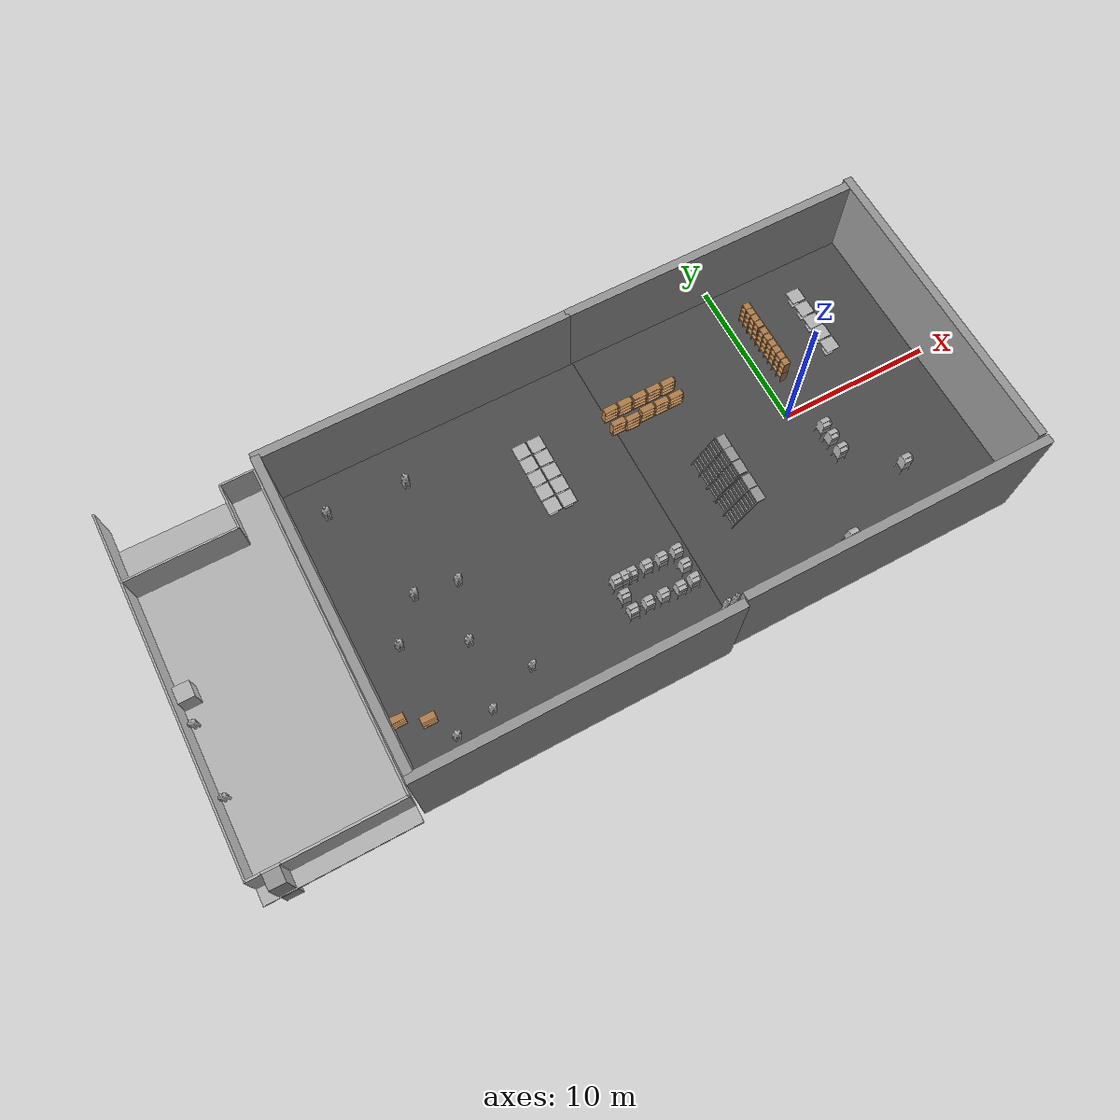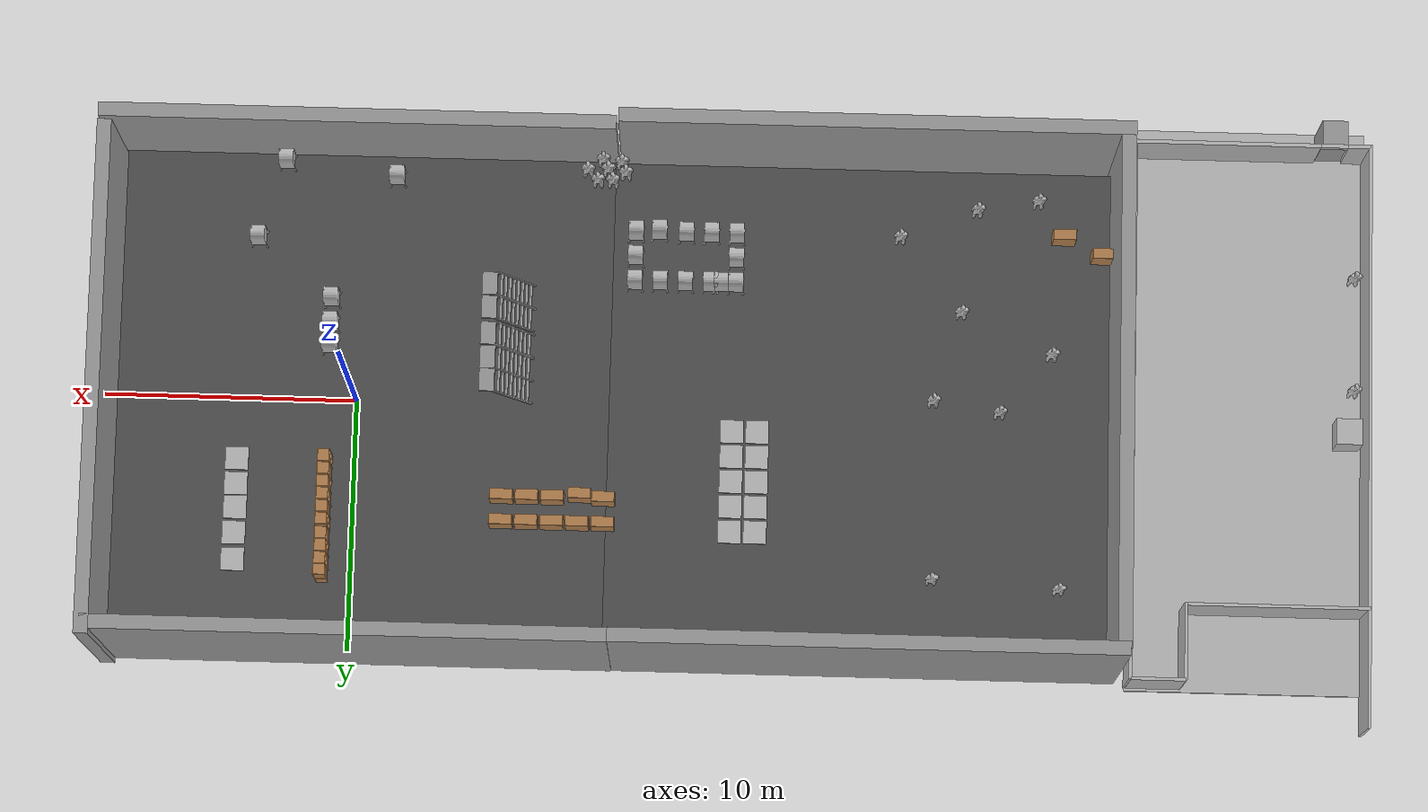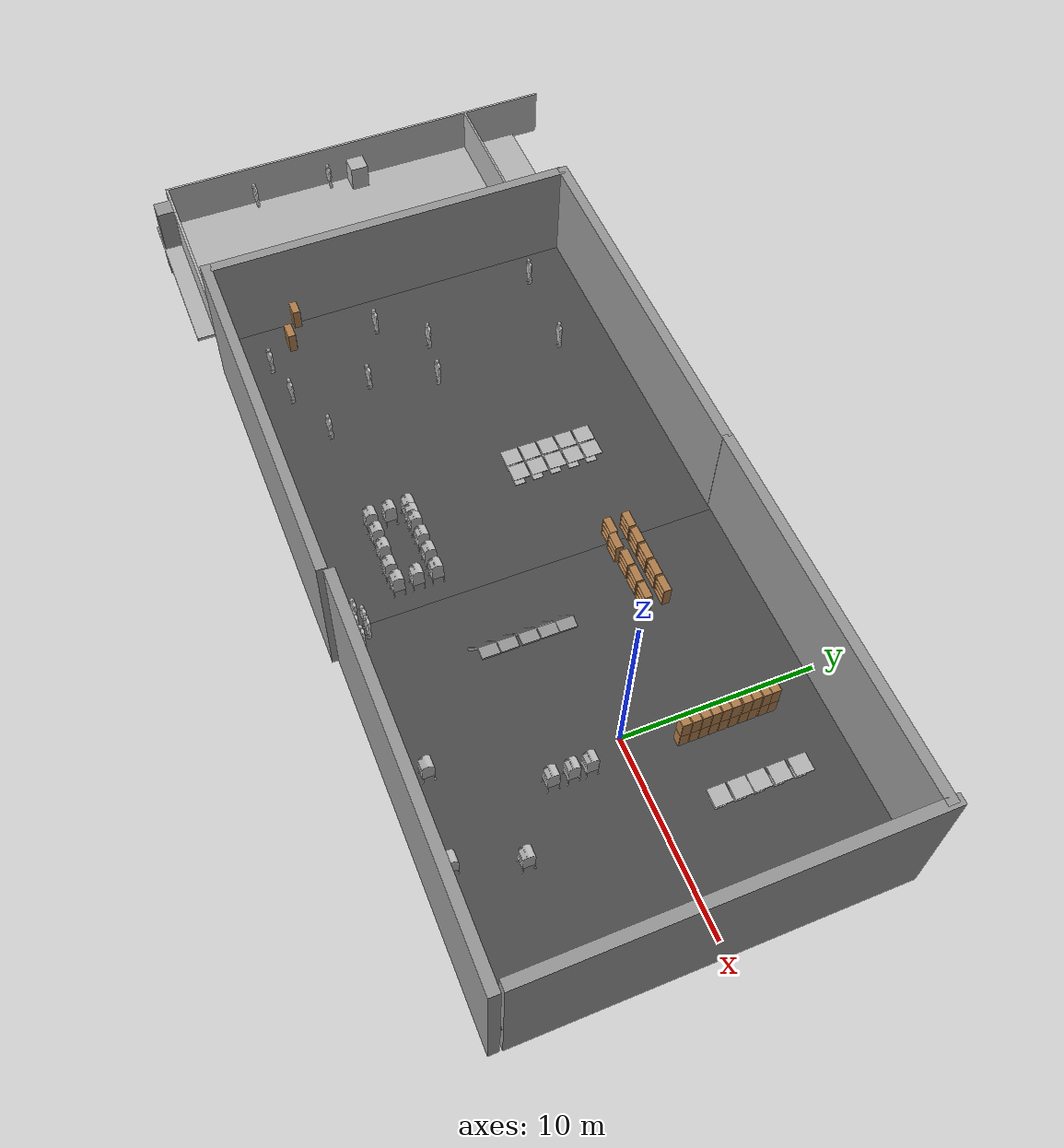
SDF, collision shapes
<?xml version='1.0'?>
<sdf version='1.6'>
  <model name='indoor_environment_4'>
    <link name='link'>
      <pose frame=''>0 0 0 0 -0 0</pose>
      <self_collide>0</self_collide>
      <kinematic>0</kinematic>
      <visual name='visual'>
        <cast_shadows>0</cast_shadows>
        <geometry>
          <box>
            <size>20 20 0.1</size>
          </box>
        </geometry>
        <material>
          <script>
            <uri>model://asphalt_plane/materials/scripts</uri>
            <uri>model://asphalt_plane/materials/textures</uri>
            <name>vrc/asphalt</name>
          </script>
          <ambient>0.5 0.5 0.5 1</ambient>
          <diffuse>0.5 0.5 0.5 1</diffuse>
          <specular>0.2 0.2 0.2 1</specular>
          <emissive>0 0 0 1</emissive>
        </material>
        <pose frame=''>0 0 0 0 -0 0</pose>
        <transparency>0</transparency>
      </visual>
      <collision name='collision'>
        <laser_retro>0</laser_retro>
        <max_contacts>10</max_contacts>
        <pose frame=''>0 0 0 0 -0 0</pose>
        <geometry>
          <box>
            <size>20 20 0.1</size>
          </box>
        </geometry>
        <surface>
          <friction>
            <ode>
              <mu>1</mu>
              <mu2>1</mu2>
              <fdir1>0 0 0</fdir1>
              <slip1>0</slip1>
              <slip2>0</slip2>
            </ode>
            <torsional>
              <coefficient>1</coefficient>
              <patch_radius>0</patch_radius>
              <surface_radius>0</surface_radius>
              <use_patch_radius>1</use_patch_radius>
              <ode>
                <slip>0</slip>
              </ode>
            </torsional>
          </friction>
          <bounce>
            <restitution_coefficient>0</restitution_coefficient>
            <threshold>1e+06</threshold>
          </bounce>
          <contact>
            <collide_without_contact>0</collide_without_contact>
            <collide_without_contact_bitmask>1</collide_without_contact_bitmask>
            <collide_bitmask>1</collide_bitmask>
            <ode>
              <soft_cfm>0</soft_cfm>
              <soft_erp>0.2</soft_erp>
              <kp>1e+13</kp>
              <kd>1</kd>
              <max_vel>0.01</max_vel>
              <min_depth>0</min_depth>
            </ode>
            <bullet>
              <split_impulse>1</split_impulse>
              <split_impulse_penetration_threshold>-0.01</split_impulse_penetration_threshold>
              <soft_cfm>0</soft_cfm>
              <soft_erp>0.2</soft_erp>
              <kp>1e+13</kp>
              <kd>1</kd>
            </bullet>
          </contact>
        </surface>
      </collision>
    </link>
    <link name='link_0'>
      <pose frame=''>-38.4667 -11.2928 0.5 0 -0 0</pose>
      <inertial>
        <mass>4.65205</mass>
        <inertia>
          <ixx>8.77751</ixx>
          <ixy>0</ixy>
          <ixz>0</ixz>
          <iyy>8.77751</iyy>
          <iyz>0</iyz>
          <izz>0.775344</izz>
        </inertia>
        <pose frame=''>0 0 0 0 -0 0</pose>
      </inertial>
      <visual name='visual'>
        <pose frame=''>0 0 0 0 -0 0</pose>
        <geometry>
          <box>
            <size>1 1 4.65206</size>
          </box>
        </geometry>
        <material>
          <lighting>1</lighting>
          <script>
            <uri>file://media/materials/scripts/gazebo.material</uri>
            <name>Gazebo/Grey</name>
          </script>
          <ambient>0.3 0.3 0.3 1</ambient>
          <diffuse>0.7 0.7 0.7 1</diffuse>
          <specular>0.01 0.01 0.01 1</specular>
          <emissive>0 0 0 1</emissive>
        </material>
        <cast_shadows>1</cast_shadows>
        <transparency>0</transparency>
      </visual>
      <collision name='collision'>
        <laser_retro>0</laser_retro>
        <max_contacts>10</max_contacts>
        <pose frame=''>0 0 0 0 -0 0</pose>
        <geometry>
          <box>
            <size>1 1 4.65206</size>
          </box>
        </geometry>
        <surface>
          <friction>
            <ode>
              <mu>1</mu>
              <mu2>1</mu2>
              <fdir1>0 0 0</fdir1>
              <slip1>0</slip1>
              <slip2>0</slip2>
            </ode>
            <torsional>
              <coefficient>1</coefficient>
              <patch_radius>0</patch_radius>
              <surface_radius>0</surface_radius>
              <use_patch_radius>1</use_patch_radius>
              <ode>
                <slip>0</slip>
              </ode>
            </torsional>
          </friction>
          <bounce>
            <restitution_coefficient>0</restitution_coefficient>
            <threshold>1e+06</threshold>
          </bounce>
          <contact>
            <collide_without_contact>0</collide_without_contact>
            <collide_without_contact_bitmask>1</collide_without_contact_bitmask>
            <collide_bitmask>1</collide_bitmask>
            <ode>
              <soft_cfm>0</soft_cfm>
              <soft_erp>0.2</soft_erp>
              <kp>1e+13</kp>
              <kd>1</kd>
              <max_vel>0.01</max_vel>
              <min_depth>0</min_depth>
            </ode>
            <bullet>
              <split_impulse>1</split_impulse>
              <split_impulse_penetration_threshold>-0.01</split_impulse_penetration_threshold>
              <soft_cfm>0</soft_cfm>
              <soft_erp>0.2</soft_erp>
              <kp>1e+13</kp>
              <kd>1</kd>
            </bullet>
          </contact>
        </surface>
      </collision>
    </link>
    <model name='asphalt_plane_0'>
      <static>1</static>
      <link name='link'>
        <collision name='collision'>
          <geometry>
            <box>
              <size>20 20 0.1</size>
            </box>
          </geometry>
          <max_contacts>10</max_contacts>
          <surface>
            <contact>
              <ode/>
            </contact>
            <bounce/>
            <friction>
              <torsional>
                <ode/>
              </torsional>
              <ode/>
            </friction>
          </surface>
        </collision>
        <visual name='visual'>
          <cast_shadows>0</cast_shadows>
          <geometry>
            <box>
              <size>20 20 0.1</size>
            </box>
          </geometry>
          <material>
            <script>
              <uri>model://asphalt_plane/materials/scripts</uri>
              <uri>model://asphalt_plane/materials/textures</uri>
              <name>vrc/asphalt</name>
            </script>
          </material>
        </visual>
        <self_collide>0</self_collide>
        <kinematic>0</kinematic>
        <gravity>1</gravity>
      </link>
      <pose frame=''>-19.9097 0.04344 0 0 -0 0</pose>
    </model>
    <model name='bookshelf'>
      <static>1</static>
      <link name='link'>
        <inertial>
          <mass>1</mass>
        </inertial>
        <collision name='back'>
          <pose frame=''>0 0.005 0.6 0 -0 0</pose>
          <geometry>
            <box>
              <size>0.9 0.01 1.2</size>
            </box>
          </geometry>
          <max_contacts>10</max_contacts>
          <surface>
            <contact>
              <ode/>
            </contact>
            <bounce/>
            <friction>
              <torsional>
                <ode/>
              </torsional>
              <ode/>
            </friction>
          </surface>
        </collision>
        <visual name='visual1'>
          <pose frame=''>0 0.005 0.6 0 -0 0</pose>
          <geometry>
            <box>
              <size>0.9 0.01 1.2</size>
            </box>
          </geometry>
          <material>
            <script>
              <uri>file://media/materials/scripts/gazebo.material</uri>
              <name>Gazebo/Wood</name>
            </script>
          </material>
        </visual>
        <collision name='left_side'>
          <pose frame=''>0.45 -0.195 0.6 0 -0 0</pose>
          <geometry>
            <box>
              <size>0.02 0.4 1.2</size>
            </box>
          </geometry>
          <max_contacts>10</max_contacts>
          <surface>
            <contact>
              <ode/>
            </contact>
            <bounce/>
            <friction>
              <torsional>
                <ode/>
              </torsional>
              <ode/>
            </friction>
          </surface>
        </collision>
        <visual name='visual2'>
          <pose frame=''>0.45 -0.195 0.6 0 -0 0</pose>
          <geometry>
            <box>
              <size>0.02 0.4 1.2</size>
            </box>
          </geometry>
          <material>
            <script>
              <uri>file://media/materials/scripts/gazebo.material</uri>
              <name>Gazebo/Wood</name>
            </script>
          </material>
        </visual>
        <collision name='right_side'>
          <pose frame=''>-0.45 -0.195 0.6 0 -0 0</pose>
          <geometry>
            <box>
              <size>0.02 0.4 1.2</size>
            </box>
          </geometry>
          <max_contacts>10</max_contacts>
          <surface>
            <contact>
              <ode/>
            </contact>
            <bounce/>
            <friction>
              <torsional>
                <ode/>
              </torsional>
              <ode/>
            </friction>
          </surface>
        </collision>
        <visual name='visual3'>
          <pose frame=''>-0.45 -0.195 0.6 0 -0 0</pose>
          <geometry>
            <box>
              <size>0.02 0.4 1.2</size>
            </box>
          </geometry>
          <material>
            <script>
              <uri>file://media/materials/scripts/gazebo.material</uri>
              <name>Gazebo/Wood</name>
            </script>
          </material>
        </visual>
        <collision name='bottom'>
          <pose frame=''>0 -0.195 0.03 0 -0 0</pose>
          <geometry>
            <box>
              <size>0.88 0.4 0.06</size>
            </box>
          </geometry>
          <max_contacts>10</max_contacts>
          <surface>
            <contact>
              <ode/>
            </contact>
            <bounce/>
            <friction>
              <torsional>
                <ode/>
              </torsional>
              <ode/>
            </friction>
          </surface>
        </collision>
        <visual name='visual4'>
          <pose frame=''>0 -0.195 0.03 0 -0 0</pose>
          <geometry>
            <box>
              <size>0.88 0.4 0.06</size>
            </box>
          </geometry>
          <material>
            <script>
              <uri>file://media/materials/scripts/gazebo.material</uri>
              <name>Gazebo/Wood</name>
            </script>
          </material>
        </visual>
        <collision name='top'>
          <pose frame=''>0 -0.195 1.19 0 -0 0</pose>
          <geometry>
            <box>
              <size>0.88 0.4 0.02</size>
            </box>
          </geometry>
          <max_contacts>10</max_contacts>
          <surface>
            <contact>
              <ode/>
            </contact>
            <bounce/>
            <friction>
              <torsional>
                <ode/>
              </torsional>
              <ode/>
            </friction>
          </surface>
        </collision>
        <visual name='visual5'>
          <pose frame=''>0 -0.195 1.19 0 -0 0</pose>
          <geometry>
            <box>
              <size>0.88 0.4 0.02</size>
            </box>
          </geometry>
          <material>
            <script>
              <uri>file://media/materials/scripts/gazebo.material</uri>
              <name>Gazebo/Wood</name>
            </script>
          </material>
        </visual>
        <collision name='low_shelf'>
          <pose frame=''>0 -0.195 0.43 0 -0 0</pose>
          <geometry>
            <box>
              <size>0.88 0.4 0.02</size>
            </box>
          </geometry>
          <max_contacts>10</max_contacts>
          <surface>
            <contact>
              <ode/>
            </contact>
            <bounce/>
            <friction>
              <torsional>
                <ode/>
              </torsional>
              <ode/>
            </friction>
          </surface>
        </collision>
        <visual name='visual6'>
          <pose frame=''>0 -0.195 0.43 0 -0 0</pose>
          <geometry>
            <box>
              <size>0.88 0.4 0.02</size>
            </box>
          </geometry>
          <material>
            <script>
              <uri>file://media/materials/scripts/gazebo.material</uri>
              <name>Gazebo/Wood</name>
            </script>
          </material>
        </visual>
        <collision name='high_shelf'>
          <pose frame=''>0 -0.195 0.8 0 -0 0</pose>
          <geometry>
            <box>
              <size>0.88 0.4 0.02</size>
            </box>
          </geometry>
          <max_contacts>10</max_contacts>
          <surface>
            <contact>
              <ode/>
            </contact>
            <bounce/>
            <friction>
              <torsional>
                <ode/>
              </torsional>
              <ode/>
            </friction>
          </surface>
        </collision>
        <visual name='visual7'>
          <pose frame=''>0 -0.195 0.8 0 -0 0</pose>
          <geometry>
            <box>
              <size>0.88 0.4 0.02</size>
            </box>
          </geometry>
          <material>
            <script>
              <uri>file://media/materials/scripts/gazebo.material</uri>
              <name>Gazebo/Wood</name>
            </script>
          </material>
        </visual>
        <self_collide>0</self_collide>
        <kinematic>0</kinematic>
        <gravity>1</gravity>
      </link>
      <pose frame=''>-29.4638 -6.22637 0.552309 0 -0 0</pose>
    </model>
    <model name='bookshelf_clone'>
      <static>1</static>
      <link name='link'>
        <inertial>
          <mass>1</mass>
        </inertial>
        <collision name='back'>
          <pose frame=''>0 0.005 0.6 0 -0 0</pose>
          <geometry>
            <box>
              <size>0.9 0.01 1.2</size>
            </box>
          </geometry>
          <max_contacts>10</max_contacts>
          <surface>
            <contact>
              <ode/>
            </contact>
            <bounce/>
            <friction>
              <torsional>
                <ode/>
              </torsional>
              <ode/>
            </friction>
          </surface>
        </collision>
        <visual name='visual1'>
          <pose frame=''>0 0.005 0.6 0 -0 0</pose>
          <geometry>
            <box>
              <size>0.9 0.01 1.2</size>
            </box>
          </geometry>
          <material>
            <script>
              <uri>file://media/materials/scripts/gazebo.material</uri>
              <name>Gazebo/Wood</name>
            </script>
          </material>
        </visual>
        <collision name='left_side'>
          <pose frame=''>0.45 -0.195 0.6 0 -0 0</pose>
          <geometry>
            <box>
              <size>0.02 0.4 1.2</size>
            </box>
          </geometry>
          <max_contacts>10</max_contacts>
          <surface>
            <contact>
              <ode/>
            </contact>
            <bounce/>
            <friction>
              <torsional>
                <ode/>
              </torsional>
              <ode/>
            </friction>
          </surface>
        </collision>
        <visual name='visual2'>
          <pose frame=''>0.45 -0.195 0.6 0 -0 0</pose>
          <geometry>
            <box>
              <size>0.02 0.4 1.2</size>
            </box>
          </geometry>
          <material>
            <script>
              <uri>file://media/materials/scripts/gazebo.material</uri>
              <name>Gazebo/Wood</name>
            </script>
          </material>
        </visual>
        <collision name='right_side'>
          <pose frame=''>-0.45 -0.195 0.6 0 -0 0</pose>
          <geometry>
            <box>
              <size>0.02 0.4 1.2</size>
            </box>
          </geometry>
          <max_contacts>10</max_contacts>
          <surface>
            <contact>
              <ode/>
            </contact>
            <bounce/>
            <friction>
              <torsional>
                <ode/>
              </torsional>
              <ode/>
            </friction>
          </surface>
        </collision>
        <visual name='visual3'>
          <pose frame=''>-0.45 -0.195 0.6 0 -0 0</pose>
          <geometry>
            <box>
              <size>0.02 0.4 1.2</size>
            </box>
          </geometry>
          <material>
            <script>
              <uri>file://media/materials/scripts/gazebo.material</uri>
              <name>Gazebo/Wood</name>
            </script>
          </material>
        </visual>
        <collision name='bottom'>
          <pose frame=''>0 -0.195 0.03 0 -0 0</pose>
          <geometry>
            <box>
              <size>0.88 0.4 0.06</size>
            </box>
          </geometry>
          <max_contacts>10</max_contacts>
          <surface>
            <contact>
              <ode/>
            </contact>
            <bounce/>
            <friction>
              <torsional>
                <ode/>
              </torsional>
              <ode/>
            </friction>
          </surface>
        </collision>
        <visual name='visual4'>
          <pose frame=''>0 -0.195 0.03 0 -0 0</pose>
          <geometry>
            <box>
              <size>0.88 0.4 0.06</size>
            </box>
          </geometry>
          <material>
            <script>
              <uri>file://media/materials/scripts/gazebo.material</uri>
              <name>Gazebo/Wood</name>
            </script>
          </material>
        </visual>
        <collision name='top'>
          <pose frame=''>0 -0.195 1.19 0 -0 0</pose>
          <geometry>
            <box>
              <size>0.88 0.4 0.02</size>
            </box>
          </geometry>
          <max_contacts>10</max_contacts>
          <surface>
            <contact>
              <ode/>
            </contact>
            <bounce/>
            <friction>
              <torsional>
                <ode/>
              </torsional>
              <ode/>
            </friction>
          </surface>
        </collision>
        <visual name='visual5'>
          <pose frame=''>0 -0.195 1.19 0 -0 0</pose>
          <geometry>
            <box>
              <size>0.88 0.4 0.02</size>
            </box>
          </geometry>
          <material>
            <script>
              <uri>file://media/materials/scripts/gazebo.material</uri>
              <name>Gazebo/Wood</name>
            </script>
          </material>
        </visual>
        <collision name='low_shelf'>
          <pose frame=''>0 -0.195 0.43 0 -0 0</pose>
          <geometry>
            <box>
              <size>0.88 0.4 0.02</size>
            </box>
          </geometry>
          <max_contacts>10</max_contacts>
          <surface>
            <contact>
              <ode/>
            </contact>
            <bounce/>
            <friction>
              <torsional>
                <ode/>
              </torsional>
              <ode/>
            </friction>
          </surface>
        </collision>
        <visual name='visual6'>
          <pose frame=''>0 -0.195 0.43 0 -0 0</pose>
          <geometry>
            <box>
              <size>0.88 0.4 0.02</size>
            </box>
          </geometry>
          <material>
            <script>
              <uri>file://media/materials/scripts/gazebo.material</uri>
              <name>Gazebo/Wood</name>
            </script>
          </material>
        </visual>
        <collision name='high_shelf'>
          <pose frame=''>0 -0.195 0.8 0 -0 0</pose>
          <geometry>
            <box>
              <size>0.88 0.4 0.02</size>
            </box>
          </geometry>
          <max_contacts>10</max_contacts>
          <surface>
            <contact>
              <ode/>
            </contact>
            <bounce/>
            <friction>
              <torsional>
                <ode/>
              </torsional>
              <ode/>
            </friction>
          </surface>
        </collision>
        <visual name='visual7'>
          <pose frame=''>0 -0.195 0.8 0 -0 0</pose>
          <geometry>
            <box>
              <size>0.88 0.4 0.02</size>
            </box>
          </geometry>
          <material>
            <script>
              <uri>file://media/materials/scripts/gazebo.material</uri>
              <name>Gazebo/Wood</name>
            </script>
          </material>
        </visual>
        <self_collide>0</self_collide>
        <kinematic>0</kinematic>
        <gravity>1</gravity>
      </link>
      <pose frame=''>-27.9097 -6.95656 0.552309 0 -0 0</pose>
    </model>
    <model name='bookshelf_clone_12_clone'>
      <static>1</static>
      <link name='link'>
        <inertial>
          <mass>1</mass>
        </inertial>
        <collision name='back'>
          <pose frame=''>0 0.005 0.6 0 -0 0</pose>
          <geometry>
            <box>
              <size>0.9 0.01 1.2</size>
            </box>
          </geometry>
          <max_contacts>10</max_contacts>
          <surface>
            <contact>
              <ode/>
            </contact>
            <bounce/>
            <friction>
              <torsional>
                <ode/>
              </torsional>
              <ode/>
            </friction>
          </surface>
        </collision>
        <visual name='visual1'>
          <pose frame=''>0 0.005 0.6 0 -0 0</pose>
          <geometry>
            <box>
              <size>0.9 0.01 1.2</size>
            </box>
          </geometry>
          <material>
            <script>
              <uri>file://media/materials/scripts/gazebo.material</uri>
              <name>Gazebo/Wood</name>
            </script>
          </material>
        </visual>
        <collision name='left_side'>
          <pose frame=''>0.45 -0.195 0.6 0 -0 0</pose>
          <geometry>
            <box>
              <size>0.02 0.4 1.2</size>
            </box>
          </geometry>
          <max_contacts>10</max_contacts>
          <surface>
            <contact>
              <ode/>
            </contact>
            <bounce/>
            <friction>
              <torsional>
                <ode/>
              </torsional>
              <ode/>
            </friction>
          </surface>
        </collision>
        <visual name='visual2'>
          <pose frame=''>0.45 -0.195 0.6 0 -0 0</pose>
          <geometry>
            <box>
              <size>0.02 0.4 1.2</size>
            </box>
          </geometry>
          <material>
            <script>
              <uri>file://media/materials/scripts/gazebo.material</uri>
              <name>Gazebo/Wood</name>
            </script>
          </material>
        </visual>
        <collision name='right_side'>
          <pose frame=''>-0.45 -0.195 0.6 0 -0 0</pose>
          <geometry>
            <box>
              <size>0.02 0.4 1.2</size>
            </box>
          </geometry>
          <max_contacts>10</max_contacts>
          <surface>
            <contact>
              <ode/>
            </contact>
            <bounce/>
            <friction>
              <torsional>
                <ode/>
              </torsional>
              <ode/>
            </friction>
          </surface>
        </collision>
        <visual name='visual3'>
          <pose frame=''>-0.45 -0.195 0.6 0 -0 0</pose>
          <geometry>
            <box>
              <size>0.02 0.4 1.2</size>
            </box>
          </geometry>
          <material>
            <script>
              <uri>file://media/materials/scripts/gazebo.material</uri>
              <name>Gazebo/Wood</name>
            </script>
          </material>
        </visual>
        <collision name='bottom'>
          <pose frame=''>0 -0.195 0.03 0 -0 0</pose>
          <geometry>
            <box>
              <size>0.88 0.4 0.06</size>
            </box>
          </geometry>
          <max_contacts>10</max_contacts>
          <surface>
            <contact>
              <ode/>
            </contact>
            <bounce/>
            <friction>
              <torsional>
                <ode/>
              </torsional>
              <ode/>
            </friction>
          </surface>
        </collision>
        <visual name='visual4'>
          <pose frame=''>0 -0.195 0.03 0 -0 0</pose>
          <geometry>
            <box>
              <size>0.88 0.4 0.06</size>
            </box>
          </geometry>
          <material>
            <script>
              <uri>file://media/materials/scripts/gazebo.material</uri>
              <name>Gazebo/Wood</name>
            </script>
          </material>
        </visual>
        <collision name='top'>
          <pose frame=''>0 -0.195 1.19 0 -0 0</pose>
          <geometry>
            <box>
              <size>0.88 0.4 0.02</size>
            </box>
          </geometry>
          <max_contacts>10</max_contacts>
          <surface>
            <contact>
              <ode/>
            </contact>
            <bounce/>
            <friction>
              <torsional>
                <ode/>
              </torsional>
              <ode/>
            </friction>
          </surface>
        </collision>
        <visual name='visual5'>
          <pose frame=''>0 -0.195 1.19 0 -0 0</pose>
          <geometry>
            <box>
              <size>0.88 0.4 0.02</size>
            </box>
          </geometry>
          <material>
            <script>
              <uri>file://media/materials/scripts/gazebo.material</uri>
              <name>Gazebo/Wood</name>
            </script>
          </material>
        </visual>
        <collision name='low_shelf'>
          <pose frame=''>0 -0.195 0.43 0 -0 0</pose>
          <geometry>
            <box>
              <size>0.88 0.4 0.02</size>
            </box>
          </geometry>
          <max_contacts>10</max_contacts>
          <surface>
            <contact>
              <ode/>
            </contact>
            <bounce/>
            <friction>
              <torsional>
                <ode/>
              </torsional>
              <ode/>
            </friction>
          </surface>
        </collision>
        <visual name='visual6'>
          <pose frame=''>0 -0.195 0.43 0 -0 0</pose>
          <geometry>
            <box>
              <size>0.88 0.4 0.02</size>
            </box>
          </geometry>
          <material>
            <script>
              <uri>file://media/materials/scripts/gazebo.material</uri>
              <name>Gazebo/Wood</name>
            </script>
          </material>
        </visual>
        <collision name='high_shelf'>
          <pose frame=''>0 -0.195 0.8 0 -0 0</pose>
          <geometry>
            <box>
              <size>0.88 0.4 0.02</size>
            </box>
          </geometry>
          <max_contacts>10</max_contacts>
          <surface>
            <contact>
              <ode/>
            </contact>
            <bounce/>
            <friction>
              <torsional>
                <ode/>
              </torsional>
              <ode/>
            </friction>
          </surface>
        </collision>
        <visual name='visual7'>
          <pose frame=''>0 -0.195 0.8 0 -0 0</pose>
          <geometry>
            <box>
              <size>0.88 0.4 0.02</size>
            </box>
          </geometry>
          <material>
            <script>
              <uri>file://media/materials/scripts/gazebo.material</uri>
              <name>Gazebo/Wood</name>
            </script>
          </material>
        </visual>
        <self_collide>0</self_collide>
        <kinematic>0</kinematic>
        <gravity>1</gravity>
      </link>
      <pose frame=''>-8.9097 5.04344 0.552309 0 -0 0</pose>
    </model>
    <model name='bookshelf_clone_12_clone_0'>
      <static>1</static>
      <link name='link'>
        <inertial>
          <mass>1</mass>
        </inertial>
        <collision name='back'>
          <pose frame=''>0 0.005 0.6 0 -0 0</pose>
          <geometry>
            <box>
              <size>0.9 0.01 1.2</size>
            </box>
          </geometry>
          <max_contacts>10</max_contacts>
          <surface>
            <contact>
              <ode/>
            </contact>
            <bounce/>
            <friction>
              <torsional>
                <ode/>
              </torsional>
              <ode/>
            </friction>
          </surface>
        </collision>
        <visual name='visual1'>
          <pose frame=''>0 0.005 0.6 0 -0 0</pose>
          <geometry>
            <box>
              <size>0.9 0.01 1.2</size>
            </box>
          </geometry>
          <material>
            <script>
              <uri>file://media/materials/scripts/gazebo.material</uri>
              <name>Gazebo/Wood</name>
            </script>
          </material>
        </visual>
        <collision name='left_side'>
          <pose frame=''>0.45 -0.195 0.6 0 -0 0</pose>
          <geometry>
            <box>
              <size>0.02 0.4 1.2</size>
            </box>
          </geometry>
          <max_contacts>10</max_contacts>
          <surface>
            <contact>
              <ode/>
            </contact>
            <bounce/>
            <friction>
              <torsional>
                <ode/>
              </torsional>
              <ode/>
            </friction>
          </surface>
        </collision>
        <visual name='visual2'>
          <pose frame=''>0.45 -0.195 0.6 0 -0 0</pose>
          <geometry>
            <box>
              <size>0.02 0.4 1.2</size>
            </box>
          </geometry>
          <material>
            <script>
              <uri>file://media/materials/scripts/gazebo.material</uri>
              <name>Gazebo/Wood</name>
            </script>
          </material>
        </visual>
        <collision name='right_side'>
          <pose frame=''>-0.45 -0.195 0.6 0 -0 0</pose>
          <geometry>
            <box>
              <size>0.02 0.4 1.2</size>
            </box>
          </geometry>
          <max_contacts>10</max_contacts>
          <surface>
            <contact>
              <ode/>
            </contact>
            <bounce/>
            <friction>
              <torsional>
                <ode/>
              </torsional>
              <ode/>
            </friction>
          </surface>
        </collision>
        <visual name='visual3'>
          <pose frame=''>-0.45 -0.195 0.6 0 -0 0</pose>
          <geometry>
            <box>
              <size>0.02 0.4 1.2</size>
            </box>
          </geometry>
          <material>
            <script>
              <uri>file://media/materials/scripts/gazebo.material</uri>
              <name>Gazebo/Wood</name>
            </script>
          </material>
        </visual>
        <collision name='bottom'>
          <pose frame=''>0 -0.195 0.03 0 -0 0</pose>
          <geometry>
            <box>
              <size>0.88 0.4 0.06</size>
            </box>
          </geometry>
          <max_contacts>10</max_contacts>
          <surface>
            <contact>
              <ode/>
            </contact>
            <bounce/>
            <friction>
              <torsional>
                <ode/>
              </torsional>
              <ode/>
            </friction>
          </surface>
        </collision>
        <visual name='visual4'>
          <pose frame=''>0 -0.195 0.03 0 -0 0</pose>
          <geometry>
            <box>
              <size>0.88 0.4 0.06</size>
            </box>
          </geometry>
          <material>
            <script>
              <uri>file://media/materials/scripts/gazebo.material</uri>
              <name>Gazebo/Wood</name>
            </script>
          </material>
        </visual>
        <collision name='top'>
          <pose frame=''>0 -0.195 1.19 0 -0 0</pose>
          <geometry>
            <box>
              <size>0.88 0.4 0.02</size>
            </box>
          </geometry>
          <max_contacts>10</max_contacts>
          <surface>
            <contact>
              <ode/>
            </contact>
            <bounce/>
            <friction>
              <torsional>
                <ode/>
              </torsional>
              <ode/>
            </friction>
          </surface>
        </collision>
        <visual name='visual5'>
          <pose frame=''>0 -0.195 1.19 0 -0 0</pose>
          <geometry>
            <box>
              <size>0.88 0.4 0.02</size>
            </box>
          </geometry>
          <material>
            <script>
              <uri>file://media/materials/scripts/gazebo.material</uri>
              <name>Gazebo/Wood</name>
            </script>
          </material>
        </visual>
        <collision name='low_shelf'>
          <pose frame=''>0 -0.195 0.43 0 -0 0</pose>
          <geometry>
            <box>
              <size>0.88 0.4 0.02</size>
            </box>
          </geometry>
          <max_contacts>10</max_contacts>
          <surface>
            <contact>
              <ode/>
            </contact>
            <bounce/>
            <friction>
              <torsional>
                <ode/>
              </torsional>
              <ode/>
            </friction>
          </surface>
        </collision>
        <visual name='visual6'>
          <pose frame=''>0 -0.195 0.43 0 -0 0</pose>
          <geometry>
            <box>
              <size>0.88 0.4 0.02</size>
            </box>
          </geometry>
          <material>
            <script>
              <uri>file://media/materials/scripts/gazebo.material</uri>
              <name>Gazebo/Wood</name>
            </script>
          </material>
        </visual>
        <collision name='high_shelf'>
          <pose frame=''>0 -0.195 0.8 0 -0 0</pose>
          <geometry>
            <box>
              <size>0.88 0.4 0.02</size>
            </box>
          </geometry>
          <max_contacts>10</max_contacts>
          <surface>
            <contact>
              <ode/>
            </contact>
            <bounce/>
            <friction>
              <torsional>
                <ode/>
              </torsional>
              <ode/>
            </friction>
          </surface>
        </collision>
        <visual name='visual7'>
          <pose frame=''>0 -0.195 0.8 0 -0 0</pose>
          <geometry>
            <box>
              <size>0.88 0.4 0.02</size>
            </box>
          </geometry>
          <material>
            <script>
              <uri>file://media/materials/scripts/gazebo.material</uri>
              <name>Gazebo/Wood</name>
            </script>
          </material>
        </visual>
        <self_collide>0</self_collide>
        <kinematic>0</kinematic>
        <gravity>1</gravity>
      </link>
      <pose frame=''>-7.9097 5.04344 0.552309 0 -0 0</pose>
    </model>
    <model name='bookshelf_clone_12_clone_1'>
      <static>1</static>
      <link name='link'>
        <inertial>
          <mass>1</mass>
        </inertial>
        <collision name='back'>
          <pose frame=''>0 0.005 0.6 0 -0 0</pose>
          <geometry>
            <box>
              <size>0.9 0.01 1.2</size>
            </box>
          </geometry>
          <max_contacts>10</max_contacts>
          <surface>
            <contact>
              <ode/>
            </contact>
            <bounce/>
            <friction>
              <torsional>
                <ode/>
              </torsional>
              <ode/>
            </friction>
          </surface>
        </collision>
        <visual name='visual1'>
          <pose frame=''>0 0.005 0.6 0 -0 0</pose>
          <geometry>
            <box>
              <size>0.9 0.01 1.2</size>
            </box>
          </geometry>
          <material>
            <script>
              <uri>file://media/materials/scripts/gazebo.material</uri>
              <name>Gazebo/Wood</name>
            </script>
          </material>
        </visual>
        <collision name='left_side'>
          <pose frame=''>0.45 -0.195 0.6 0 -0 0</pose>
          <geometry>
            <box>
              <size>0.02 0.4 1.2</size>
            </box>
          </geometry>
          <max_contacts>10</max_contacts>
          <surface>
            <contact>
              <ode/>
            </contact>
            <bounce/>
            <friction>
              <torsional>
                <ode/>
              </torsional>
              <ode/>
            </friction>
          </surface>
        </collision>
        <visual name='visual2'>
          <pose frame=''>0.45 -0.195 0.6 0 -0 0</pose>
          <geometry>
            <box>
              <size>0.02 0.4 1.2</size>
            </box>
          </geometry>
          <material>
            <script>
              <uri>file://media/materials/scripts/gazebo.material</uri>
              <name>Gazebo/Wood</name>
            </script>
          </material>
        </visual>
        <collision name='right_side'>
          <pose frame=''>-0.45 -0.195 0.6 0 -0 0</pose>
          <geometry>
            <box>
              <size>0.02 0.4 1.2</size>
            </box>
          </geometry>
          <max_contacts>10</max_contacts>
          <surface>
            <contact>
              <ode/>
            </contact>
            <bounce/>
            <friction>
              <torsional>
                <ode/>
              </torsional>
              <ode/>
            </friction>
          </surface>
        </collision>
        <visual name='visual3'>
          <pose frame=''>-0.45 -0.195 0.6 0 -0 0</pose>
          <geometry>
            <box>
              <size>0.02 0.4 1.2</size>
            </box>
          </geometry>
          <material>
            <script>
              <uri>file://media/materials/scripts/gazebo.material</uri>
              <name>Gazebo/Wood</name>
            </script>
          </material>
        </visual>
        <collision name='bottom'>
          <pose frame=''>0 -0.195 0.03 0 -0 0</pose>
          <geometry>
            <box>
              <size>0.88 0.4 0.06</size>
            </box>
          </geometry>
          <max_contacts>10</max_contacts>
          <surface>
            <contact>
              <ode/>
            </contact>
            <bounce/>
            <friction>
              <torsional>
                <ode/>
              </torsional>
              <ode/>
            </friction>
          </surface>
        </collision>
        <visual name='visual4'>
          <pose frame=''>0 -0.195 0.03 0 -0 0</pose>
          <geometry>
            <box>
              <size>0.88 0.4 0.06</size>
            </box>
          </geometry>
          <material>
            <script>
              <uri>file://media/materials/scripts/gazebo.material</uri>
              <name>Gazebo/Wood</name>
            </script>
          </material>
        </visual>
        <collision name='top'>
          <pose frame=''>0 -0.195 1.19 0 -0 0</pose>
          <geometry>
            <box>
              <size>0.88 0.4 0.02</size>
            </box>
          </geometry>
          <max_contacts>10</max_contacts>
          <surface>
            <contact>
              <ode/>
            </contact>
            <bounce/>
            <friction>
              <torsional>
                <ode/>
              </torsional>
              <ode/>
            </friction>
          </surface>
        </collision>
        <visual name='visual5'>
          <pose frame=''>0 -0.195 1.19 0 -0 0</pose>
          <geometry>
            <box>
              <size>0.88 0.4 0.02</size>
            </box>
          </geometry>
          <material>
            <script>
              <uri>file://media/materials/scripts/gazebo.material</uri>
              <name>Gazebo/Wood</name>
            </script>
          </material>
        </visual>
        <collision name='low_shelf'>
          <pose frame=''>0 -0.195 0.43 0 -0 0</pose>
          <geometry>
            <box>
              <size>0.88 0.4 0.02</size>
            </box>
          </geometry>
          <max_contacts>10</max_contacts>
          <surface>
            <contact>
              <ode/>
            </contact>
            <bounce/>
            <friction>
              <torsional>
                <ode/>
              </torsional>
              <ode/>
            </friction>
          </surface>
        </collision>
        <visual name='visual6'>
          <pose frame=''>0 -0.195 0.43 0 -0 0</pose>
          <geometry>
            <box>
              <size>0.88 0.4 0.02</size>
            </box>
          </geometry>
          <material>
            <script>
              <uri>file://media/materials/scripts/gazebo.material</uri>
              <name>Gazebo/Wood</name>
            </script>
          </material>
        </visual>
        <collision name='high_shelf'>
          <pose frame=''>0 -0.195 0.8 0 -0 0</pose>
          <geometry>
            <box>
              <size>0.88 0.4 0.02</size>
            </box>
          </geometry>
          <max_contacts>10</max_contacts>
          <surface>
            <contact>
              <ode/>
            </contact>
            <bounce/>
            <friction>
              <torsional>
                <ode/>
              </torsional>
              <ode/>
            </friction>
          </surface>
        </collision>
        <visual name='visual7'>
          <pose frame=''>0 -0.195 0.8 0 -0 0</pose>
          <geometry>
            <box>
              <size>0.88 0.4 0.02</size>
            </box>
          </geometry>
          <material>
            <script>
              <uri>file://media/materials/scripts/gazebo.material</uri>
              <name>Gazebo/Wood</name>
            </script>
          </material>
        </visual>
        <self_collide>0</self_collide>
        <kinematic>0</kinematic>
        <gravity>1</gravity>
      </link>
      <pose frame=''>-6.9097 5.04344 0.552309 0 -0 0</pose>
    </model>
    <model name='bookshelf_clone_12_clone_2'>
      <static>1</static>
      <link name='link'>
        <inertial>
          <mass>1</mass>
        </inertial>
        <collision name='back'>
          <pose frame=''>0 0.005 0.6 0 -0 0</pose>
          <geometry>
            <box>
              <size>0.9 0.01 1.2</size>
            </box>
          </geometry>
          <max_contacts>10</max_contacts>
          <surface>
            <contact>
              <ode/>
            </contact>
            <bounce/>
            <friction>
              <torsional>
                <ode/>
              </torsional>
              <ode/>
            </friction>
          </surface>
        </collision>
        <visual name='visual1'>
          <pose frame=''>0 0.005 0.6 0 -0 0</pose>
          <geometry>
            <box>
              <size>0.9 0.01 1.2</size>
            </box>
          </geometry>
          <material>
            <script>
              <uri>file://media/materials/scripts/gazebo.material</uri>
              <name>Gazebo/Wood</name>
            </script>
          </material>
        </visual>
        <collision name='left_side'>
          <pose frame=''>0.45 -0.195 0.6 0 -0 0</pose>
          <geometry>
            <box>
              <size>0.02 0.4 1.2</size>
            </box>
          </geometry>
          <max_contacts>10</max_contacts>
          <surface>
            <contact>
              <ode/>
            </contact>
            <bounce/>
            <friction>
              <torsional>
                <ode/>
              </torsional>
              <ode/>
            </friction>
          </surface>
        </collision>
        <visual name='visual2'>
          <pose frame=''>0.45 -0.195 0.6 0 -0 0</pose>
          <geometry>
            <box>
              <size>0.02 0.4 1.2</size>
            </box>
          </geometry>
          <material>
            <script>
              <uri>file://media/materials/scripts/gazebo.material</uri>
              <name>Gazebo/Wood</name>
            </script>
          </material>
        </visual>
        <collision name='right_side'>
          <pose frame=''>-0.45 -0.195 0.6 0 -0 0</pose>
          <geometry>
            <box>
              <size>0.02 0.4 1.2</size>
            </box>
          </geometry>
          <max_contacts>10</max_contacts>
          <surface>
            <contact>
              <ode/>
            </contact>
            <bounce/>
            <friction>
              <torsional>
                <ode/>
              </torsional>
              <ode/>
            </friction>
          </surface>
        </collision>
        <visual name='visual3'>
          <pose frame=''>-0.45 -0.195 0.6 0 -0 0</pose>
          <geometry>
            <box>
              <size>0.02 0.4 1.2</size>
            </box>
          </geometry>
          <material>
            <script>
              <uri>file://media/materials/scripts/gazebo.material</uri>
              <name>Gazebo/Wood</name>
            </script>
          </material>
        </visual>
        <collision name='bottom'>
          <pose frame=''>0 -0.195 0.03 0 -0 0</pose>
          <geometry>
            <box>
              <size>0.88 0.4 0.06</size>
            </box>
          </geometry>
          <max_contacts>10</max_contacts>
          <surface>
            <contact>
              <ode/>
            </contact>
            <bounce/>
            <friction>
              <torsional>
                <ode/>
              </torsional>
              <ode/>
            </friction>
          </surface>
        </collision>
        <visual name='visual4'>
          <pose frame=''>0 -0.195 0.03 0 -0 0</pose>
          <geometry>
            <box>
              <size>0.88 0.4 0.06</size>
            </box>
          </geometry>
          <material>
            <script>
              <uri>file://media/materials/scripts/gazebo.material</uri>
              <name>Gazebo/Wood</name>
            </script>
          </material>
        </visual>
        <collision name='top'>
          <pose frame=''>0 -0.195 1.19 0 -0 0</pose>
          <geometry>
            <box>
              <size>0.88 0.4 0.02</size>
            </box>
          </geometry>
          <max_contacts>10</max_contacts>
          <surface>
            <contact>
              <ode/>
            </contact>
            <bounce/>
            <friction>
              <torsional>
                <ode/>
              </torsional>
              <ode/>
            </friction>
          </surface>
        </collision>
        <visual name='visual5'>
          <pose frame=''>0 -0.195 1.19 0 -0 0</pose>
          <geometry>
            <box>
              <size>0.88 0.4 0.02</size>
            </box>
          </geometry>
          <material>
            <script>
              <uri>file://media/materials/scripts/gazebo.material</uri>
              <name>Gazebo/Wood</name>
            </script>
          </material>
        </visual>
        <collision name='low_shelf'>
          <pose frame=''>0 -0.195 0.43 0 -0 0</pose>
          <geometry>
            <box>
              <size>0.88 0.4 0.02</size>
            </box>
          </geometry>
          <max_contacts>10</max_contacts>
          <surface>
            <contact>
              <ode/>
            </contact>
            <bounce/>
            <friction>
              <torsional>
                <ode/>
              </torsional>
              <ode/>
            </friction>
          </surface>
        </collision>
        <visual name='visual6'>
          <pose frame=''>0 -0.195 0.43 0 -0 0</pose>
          <geometry>
            <box>
              <size>0.88 0.4 0.02</size>
            </box>
          </geometry>
          <material>
            <script>
              <uri>file://media/materials/scripts/gazebo.material</uri>
              <name>Gazebo/Wood</name>
            </script>
          </material>
        </visual>
        <collision name='high_shelf'>
          <pose frame=''>0 -0.195 0.8 0 -0 0</pose>
          <geometry>
            <box>
              <size>0.88 0.4 0.02</size>
            </box>
          </geometry>
          <max_contacts>10</max_contacts>
          <surface>
            <contact>
              <ode/>
            </contact>
            <bounce/>
            <friction>
              <torsional>
                <ode/>
              </torsional>
              <ode/>
            </friction>
          </surface>
        </collision>
        <visual name='visual7'>
          <pose frame=''>0 -0.195 0.8 0 -0 0</pose>
          <geometry>
            <box>
              <size>0.88 0.4 0.02</size>
            </box>
          </geometry>
          <material>
            <script>
              <uri>file://media/materials/scripts/gazebo.material</uri>
              <name>Gazebo/Wood</name>
            </script>
          </material>
        </visual>
        <self_collide>0</self_collide>
        <kinematic>0</kinematic>
        <gravity>1</gravity>
      </link>
      <pose frame=''>-5.9097 5.04344 0.552309 0 -0 0</pose>
    </model>
    <model name='bookshelf_clone_12_clone_3'>
      <static>1</static>
      <link name='link'>
        <inertial>
          <mass>1</mass>
        </inertial>
        <collision name='back'>
          <pose frame=''>0 0.005 0.6 0 -0 0</pose>
          <geometry>
            <box>
              <size>0.9 0.01 1.2</size>
            </box>
          </geometry>
          <max_contacts>10</max_contacts>
          <surface>
            <contact>
              <ode/>
            </contact>
            <bounce/>
            <friction>
              <torsional>
                <ode/>
              </torsional>
              <ode/>
            </friction>
          </surface>
        </collision>
        <visual name='visual1'>
          <pose frame=''>0 0.005 0.6 0 -0 0</pose>
          <geometry>
            <box>
              <size>0.9 0.01 1.2</size>
            </box>
          </geometry>
          <material>
            <script>
              <uri>file://media/materials/scripts/gazebo.material</uri>
              <name>Gazebo/Wood</name>
            </script>
          </material>
        </visual>
        <collision name='left_side'>
          <pose frame=''>0.45 -0.195 0.6 0 -0 0</pose>
          <geometry>
            <box>
              <size>0.02 0.4 1.2</size>
            </box>
          </geometry>
          <max_contacts>10</max_contacts>
          <surface>
            <contact>
              <ode/>
            </contact>
            <bounce/>
            <friction>
              <torsional>
                <ode/>
              </torsional>
              <ode/>
            </friction>
          </surface>
        </collision>
        <visual name='visual2'>
          <pose frame=''>0.45 -0.195 0.6 0 -0 0</pose>
          <geometry>
            <box>
              <size>0.02 0.4 1.2</size>
            </box>
          </geometry>
          <material>
            <script>
              <uri>file://media/materials/scripts/gazebo.material</uri>
              <name>Gazebo/Wood</name>
            </script>
          </material>
        </visual>
        <collision name='right_side'>
          <pose frame=''>-0.45 -0.195 0.6 0 -0 0</pose>
          <geometry>
            <box>
              <size>0.02 0.4 1.2</size>
            </box>
          </geometry>
          <max_contacts>10</max_contacts>
          <surface>
            <contact>
              <ode/>
            </contact>
            <bounce/>
            <friction>
              <torsional>
                <ode/>
              </torsional>
              <ode/>
            </friction>
          </surface>
        </collision>
        <visual name='visual3'>
          <pose frame=''>-0.45 -0.195 0.6 0 -0 0</pose>
          <geometry>
            <box>
              <size>0.02 0.4 1.2</size>
            </box>
          </geometry>
          <material>
            <script>
              <uri>file://media/materials/scripts/gazebo.material</uri>
              <name>Gazebo/Wood</name>
            </script>
          </material>
        </visual>
        <collision name='bottom'>
          <pose frame=''>0 -0.195 0.03 0 -0 0</pose>
          <geometry>
            <box>
              <size>0.88 0.4 0.06</size>
            </box>
          </geometry>
          <max_contacts>10</max_contacts>
          <surface>
            <contact>
              <ode/>
            </contact>
            <bounce/>
            <friction>
              <torsional>
                <ode/>
              </torsional>
              <ode/>
            </friction>
          </surface>
        </collision>
        <visual name='visual4'>
          <pose frame=''>0 -0.195 0.03 0 -0 0</pose>
          <geometry>
            <box>
              <size>0.88 0.4 0.06</size>
            </box>
          </geometry>
          <material>
            <script>
              <uri>file://media/materials/scripts/gazebo.material</uri>
              <name>Gazebo/Wood</name>
            </script>
          </material>
        </visual>
        <collision name='top'>
          <pose frame=''>0 -0.195 1.19 0 -0 0</pose>
          <geometry>
            <box>
              <size>0.88 0.4 0.02</size>
            </box>
          </geometry>
          <max_contacts>10</max_contacts>
          <surface>
            <contact>
              <ode/>
            </contact>
            <bounce/>
            <friction>
              <torsional>
                <ode/>
              </torsional>
              <ode/>
            </friction>
          </surface>
        </collision>
        <visual name='visual5'>
          <pose frame=''>0 -0.195 1.19 0 -0 0</pose>
          <geometry>
            <box>
              <size>0.88 0.4 0.02</size>
            </box>
          </geometry>
          <material>
            <script>
              <uri>file://media/materials/scripts/gazebo.material</uri>
              <name>Gazebo/Wood</name>
            </script>
          </material>
        </visual>
        <collision name='low_shelf'>
          <pose frame=''>0 -0.195 0.43 0 -0 0</pose>
          <geometry>
            <box>
              <size>0.88 0.4 0.02</size>
            </box>
          </geometry>
          <max_contacts>10</max_contacts>
          <surface>
            <contact>
              <ode/>
            </contact>
            <bounce/>
            <friction>
              <torsional>
                <ode/>
              </torsional>
              <ode/>
            </friction>
          </surface>
        </collision>
        <visual name='visual6'>
          <pose frame=''>0 -0.195 0.43 0 -0 0</pose>
          <geometry>
            <box>
              <size>0.88 0.4 0.02</size>
            </box>
          </geometry>
          <material>
            <script>
              <uri>file://media/materials/scripts/gazebo.material</uri>
              <name>Gazebo/Wood</name>
            </script>
          </material>
        </visual>
        <collision name='high_shelf'>
          <pose frame=''>0 -0.195 0.8 0 -0 0</pose>
          <geometry>
            <box>
              <size>0.88 0.4 0.02</size>
            </box>
          </geometry>
          <max_contacts>10</max_contacts>
          <surface>
            <contact>
              <ode/>
            </contact>
            <bounce/>
            <friction>
              <torsional>
                <ode/>
              </torsional>
              <ode/>
            </friction>
          </surface>
        </collision>
        <visual name='visual7'>
          <pose frame=''>0 -0.195 0.8 0 -0 0</pose>
          <geometry>
            <box>
              <size>0.88 0.4 0.02</size>
            </box>
          </geometry>
          <material>
            <script>
              <uri>file://media/materials/scripts/gazebo.material</uri>
              <name>Gazebo/Wood</name>
            </script>
          </material>
        </visual>
        <self_collide>0</self_collide>
        <kinematic>0</kinematic>
        <gravity>1</gravity>
      </link>
      <pose frame=''>-9.9097 5.04344 0.552309 0 -0 0</pose>
    </model>
    <model name='bookshelf_clone_12_clone_4'>
      <static>1</static>
      <link name='link'>
        <inertial>
          <mass>1</mass>
        </inertial>
        <collision name='back'>
          <pose frame=''>0 0.005 0.6 0 -0 0</pose>
          <geometry>
            <box>
              <size>0.9 0.01 1.2</size>
            </box>
          </geometry>
          <max_contacts>10</max_contacts>
          <surface>
            <contact>
              <ode/>
            </contact>
            <bounce/>
            <friction>
              <torsional>
                <ode/>
              </torsional>
              <ode/>
            </friction>
          </surface>
        </collision>
        <visual name='visual1'>
          <pose frame=''>0 0.005 0.6 0 -0 0</pose>
          <geometry>
            <box>
              <size>0.9 0.01 1.2</size>
            </box>
          </geometry>
          <material>
            <script>
              <uri>file://media/materials/scripts/gazebo.material</uri>
              <name>Gazebo/Wood</name>
            </script>
          </material>
        </visual>
        <collision name='left_side'>
          <pose frame=''>0.45 -0.195 0.6 0 -0 0</pose>
          <geometry>
            <box>
              <size>0.02 0.4 1.2</size>
            </box>
          </geometry>
          <max_contacts>10</max_contacts>
          <surface>
            <contact>
              <ode/>
            </contact>
            <bounce/>
            <friction>
              <torsional>
                <ode/>
              </torsional>
              <ode/>
            </friction>
          </surface>
        </collision>
        <visual name='visual2'>
          <pose frame=''>0.45 -0.195 0.6 0 -0 0</pose>
          <geometry>
            <box>
              <size>0.02 0.4 1.2</size>
            </box>
          </geometry>
          <material>
            <script>
              <uri>file://media/materials/scripts/gazebo.material</uri>
              <name>Gazebo/Wood</name>
            </script>
          </material>
        </visual>
        <collision name='right_side'>
          <pose frame=''>-0.45 -0.195 0.6 0 -0 0</pose>
          <geometry>
            <box>
              <size>0.02 0.4 1.2</size>
            </box>
          </geometry>
          <max_contacts>10</max_contacts>
          <surface>
            <contact>
              <ode/>
            </contact>
            <bounce/>
            <friction>
              <torsional>
                <ode/>
              </torsional>
              <ode/>
            </friction>
          </surface>
        </collision>
        <visual name='visual3'>
          <pose frame=''>-0.45 -0.195 0.6 0 -0 0</pose>
          <geometry>
            <box>
              <size>0.02 0.4 1.2</size>
            </box>
          </geometry>
          <material>
            <script>
              <uri>file://media/materials/scripts/gazebo.material</uri>
              <name>Gazebo/Wood</name>
            </script>
          </material>
        </visual>
        <collision name='bottom'>
          <pose frame=''>0 -0.195 0.03 0 -0 0</pose>
          <geometry>
            <box>
              <size>0.88 0.4 0.06</size>
            </box>
          </geometry>
          <max_contacts>10</max_contacts>
          <surface>
            <contact>
              <ode/>
            </contact>
            <bounce/>
            <friction>
              <torsional>
                <ode/>
              </torsional>
              <ode/>
            </friction>
          </surface>
        </collision>
        <visual name='visual4'>
          <pose frame=''>0 -0.195 0.03 0 -0 0</pose>
          <geometry>
            <box>
              <size>0.88 0.4 0.06</size>
            </box>
          </geometry>
          <material>
            <script>
              <uri>file://media/materials/scripts/gazebo.material</uri>
              <name>Gazebo/Wood</name>
            </script>
          </material>
        </visual>
        <collision name='top'>
          <pose frame=''>0 -0.195 1.19 0 -0 0</pose>
          <geometry>
            <box>
              <size>0.88 0.4 0.02</size>
            </box>
          </geometry>
          <max_contacts>10</max_contacts>
          <surface>
            <contact>
              <ode/>
            </contact>
            <bounce/>
            <friction>
              <torsional>
                <ode/>
              </torsional>
              <ode/>
            </friction>
          </surface>
        </collision>
        <visual name='visual5'>
          <pose frame=''>0 -0.195 1.19 0 -0 0</pose>
          <geometry>
            <box>
              <size>0.88 0.4 0.02</size>
            </box>
          </geometry>
          <material>
            <script>
              <uri>file://media/materials/scripts/gazebo.material</uri>
              <name>Gazebo/Wood</name>
            </script>
          </material>
        </visual>
        <collision name='low_shelf'>
          <pose frame=''>0 -0.195 0.43 0 -0 0</pose>
          <geometry>
            <box>
              <size>0.88 0.4 0.02</size>
            </box>
          </geometry>
          <max_contacts>10</max_contacts>
          <surface>
            <contact>
              <ode/>
            </contact>
            <bounce/>
            <friction>
              <torsional>
                <ode/>
              </torsional>
              <ode/>
            </friction>
          </surface>
        </collision>
        <visual name='visual6'>
          <pose frame=''>0 -0.195 0.43 0 -0 0</pose>
          <geometry>
            <box>
              <size>0.88 0.4 0.02</size>
            </box>
          </geometry>
          <material>
            <script>
              <uri>file://media/materials/scripts/gazebo.material</uri>
              <name>Gazebo/Wood</name>
            </script>
          </material>
        </visual>
        <collision name='high_shelf'>
          <pose frame=''>0 -0.195 0.8 0 -0 0</pose>
          <geometry>
            <box>
              <size>0.88 0.4 0.02</size>
            </box>
          </geometry>
          <max_contacts>10</max_contacts>
          <surface>
            <contact>
              <ode/>
            </contact>
            <bounce/>
            <friction>
              <torsional>
                <ode/>
              </torsional>
              <ode/>
            </friction>
          </surface>
        </collision>
        <visual name='visual7'>
          <pose frame=''>0 -0.195 0.8 0 -0 0</pose>
          <geometry>
            <box>
              <size>0.88 0.4 0.02</size>
            </box>
          </geometry>
          <material>
            <script>
              <uri>file://media/materials/scripts/gazebo.material</uri>
              <name>Gazebo/Wood</name>
            </script>
          </material>
        </visual>
        <self_collide>0</self_collide>
        <kinematic>0</kinematic>
        <gravity>1</gravity>
      </link>
      <pose frame=''>-5.9097 4.04344 0.552309 0 -0 0</pose>
    </model>
    <model name='bookshelf_clone_12_clone_5'>
      <static>1</static>
      <link name='link'>
        <inertial>
          <mass>1</mass>
        </inertial>
        <collision name='back'>
          <pose frame=''>0 0.005 0.6 0 -0 0</pose>
          <geometry>
            <box>
              <size>0.9 0.01 1.2</size>
            </box>
          </geometry>
          <max_contacts>10</max_contacts>
          <surface>
            <contact>
              <ode/>
            </contact>
            <bounce/>
            <friction>
              <torsional>
                <ode/>
              </torsional>
              <ode/>
            </friction>
          </surface>
        </collision>
        <visual name='visual1'>
          <pose frame=''>0 0.005 0.6 0 -0 0</pose>
          <geometry>
            <box>
              <size>0.9 0.01 1.2</size>
            </box>
          </geometry>
          <material>
            <script>
              <uri>file://media/materials/scripts/gazebo.material</uri>
              <name>Gazebo/Wood</name>
            </script>
          </material>
        </visual>
        <collision name='left_side'>
          <pose frame=''>0.45 -0.195 0.6 0 -0 0</pose>
          <geometry>
            <box>
              <size>0.02 0.4 1.2</size>
            </box>
          </geometry>
          <max_contacts>10</max_contacts>
          <surface>
            <contact>
              <ode/>
            </contact>
            <bounce/>
            <friction>
              <torsional>
                <ode/>
              </torsional>
              <ode/>
            </friction>
          </surface>
        </collision>
        <visual name='visual2'>
          <pose frame=''>0.45 -0.195 0.6 0 -0 0</pose>
          <geometry>
            <box>
              <size>0.02 0.4 1.2</size>
            </box>
          </geometry>
          <material>
            <script>
              <uri>file://media/materials/scripts/gazebo.material</uri>
              <name>Gazebo/Wood</name>
            </script>
          </material>
        </visual>
        <collision name='right_side'>
          <pose frame=''>-0.45 -0.195 0.6 0 -0 0</pose>
          <geometry>
            <box>
              <size>0.02 0.4 1.2</size>
            </box>
          </geometry>
          <max_contacts>10</max_contacts>
          <surface>
            <contact>
              <ode/>
            </contact>
            <bounce/>
            <friction>
              <torsional>
                <ode/>
              </torsional>
              <ode/>
            </friction>
          </surface>
        </collision>
        <visual name='visual3'>
          <pose frame=''>-0.45 -0.195 0.6 0 -0 0</pose>
          <geometry>
            <box>
              <size>0.02 0.4 1.2</size>
            </box>
          </geometry>
          <material>
            <script>
              <uri>file://media/materials/scripts/gazebo.material</uri>
              <name>Gazebo/Wood</name>
            </script>
          </material>
        </visual>
        <collision name='bottom'>
          <pose frame=''>0 -0.195 0.03 0 -0 0</pose>
          <geometry>
            <box>
              <size>0.88 0.4 0.06</size>
            </box>
          </geometry>
          <max_contacts>10</max_contacts>
          <surface>
            <contact>
              <ode/>
            </contact>
            <bounce/>
            <friction>
              <torsional>
                <ode/>
              </torsional>
              <ode/>
            </friction>
          </surface>
        </collision>
        <visual name='visual4'>
          <pose frame=''>0 -0.195 0.03 0 -0 0</pose>
          <geometry>
            <box>
              <size>0.88 0.4 0.06</size>
            </box>
          </geometry>
          <material>
            <script>
              <uri>file://media/materials/scripts/gazebo.material</uri>
              <name>Gazebo/Wood</name>
            </script>
          </material>
        </visual>
        <collision name='top'>
          <pose frame=''>0 -0.195 1.19 0 -0 0</pose>
          <geometry>
            <box>
              <size>0.88 0.4 0.02</size>
            </box>
          </geometry>
          <max_contacts>10</max_contacts>
          <surface>
            <contact>
              <ode/>
            </contact>
            <bounce/>
            <friction>
              <torsional>
                <ode/>
              </torsional>
              <ode/>
            </friction>
          </surface>
        </collision>
        <visual name='visual5'>
          <pose frame=''>0 -0.195 1.19 0 -0 0</pose>
          <geometry>
            <box>
              <size>0.88 0.4 0.02</size>
            </box>
          </geometry>
          <material>
            <script>
              <uri>file://media/materials/scripts/gazebo.material</uri>
              <name>Gazebo/Wood</name>
            </script>
          </material>
        </visual>
        <collision name='low_shelf'>
          <pose frame=''>0 -0.195 0.43 0 -0 0</pose>
          <geometry>
            <box>
              <size>0.88 0.4 0.02</size>
            </box>
          </geometry>
          <max_contacts>10</max_contacts>
          <surface>
            <contact>
              <ode/>
            </contact>
            <bounce/>
            <friction>
              <torsional>
                <ode/>
              </torsional>
              <ode/>
            </friction>
          </surface>
        </collision>
        <visual name='visual6'>
          <pose frame=''>0 -0.195 0.43 0 -0 0</pose>
          <geometry>
            <box>
              <size>0.88 0.4 0.02</size>
            </box>
          </geometry>
          <material>
            <script>
              <uri>file://media/materials/scripts/gazebo.material</uri>
              <name>Gazebo/Wood</name>
            </script>
          </material>
        </visual>
        <collision name='high_shelf'>
          <pose frame=''>0 -0.195 0.8 0 -0 0</pose>
          <geometry>
            <box>
              <size>0.88 0.4 0.02</size>
            </box>
          </geometry>
          <max_contacts>10</max_contacts>
          <surface>
            <contact>
              <ode/>
            </contact>
            <bounce/>
            <friction>
              <torsional>
                <ode/>
              </torsional>
              <ode/>
            </friction>
          </surface>
        </collision>
        <visual name='visual7'>
          <pose frame=''>0 -0.195 0.8 0 -0 0</pose>
          <geometry>
            <box>
              <size>0.88 0.4 0.02</size>
            </box>
          </geometry>
          <material>
            <script>
              <uri>file://media/materials/scripts/gazebo.material</uri>
              <name>Gazebo/Wood</name>
            </script>
          </material>
        </visual>
        <self_collide>0</self_collide>
        <kinematic>0</kinematic>
        <gravity>1</gravity>
      </link>
      <pose frame=''>-6.9097 4.04344 0.552309 0 -0 0</pose>
    </model>
    <model name='bookshelf_clone_12_clone_6'>
      <static>1</static>
      <link name='link'>
        <inertial>
          <mass>1</mass>
        </inertial>
        <collision name='back'>
          <pose frame=''>0 0.005 0.6 0 -0 0</pose>
          <geometry>
            <box>
              <size>0.9 0.01 1.2</size>
            </box>
          </geometry>
          <max_contacts>10</max_contacts>
          <surface>
            <contact>
              <ode/>
            </contact>
            <bounce/>
            <friction>
              <torsional>
                <ode/>
              </torsional>
              <ode/>
            </friction>
          </surface>
        </collision>
        <visual name='visual1'>
          <pose frame=''>0 0.005 0.6 0 -0 0</pose>
          <geometry>
            <box>
              <size>0.9 0.01 1.2</size>
            </box>
          </geometry>
          <material>
            <script>
              <uri>file://media/materials/scripts/gazebo.material</uri>
              <name>Gazebo/Wood</name>
            </script>
          </material>
        </visual>
        <collision name='left_side'>
          <pose frame=''>0.45 -0.195 0.6 0 -0 0</pose>
          <geometry>
            <box>
              <size>0.02 0.4 1.2</size>
            </box>
          </geometry>
          <max_contacts>10</max_contacts>
          <surface>
            <contact>
              <ode/>
            </contact>
            <bounce/>
            <friction>
              <torsional>
                <ode/>
              </torsional>
              <ode/>
            </friction>
          </surface>
        </collision>
        <visual name='visual2'>
          <pose frame=''>0.45 -0.195 0.6 0 -0 0</pose>
          <geometry>
            <box>
              <size>0.02 0.4 1.2</size>
            </box>
          </geometry>
          <material>
            <script>
              <uri>file://media/materials/scripts/gazebo.material</uri>
              <name>Gazebo/Wood</name>
            </script>
          </material>
        </visual>
        <collision name='right_side'>
          <pose frame=''>-0.45 -0.195 0.6 0 -0 0</pose>
          <geometry>
            <box>
              <size>0.02 0.4 1.2</size>
            </box>
          </geometry>
          <max_contacts>10</max_contacts>
          <surface>
            <contact>
              <ode/>
            </contact>
            <bounce/>
            <friction>
              <torsional>
                <ode/>
              </torsional>
              <ode/>
            </friction>
          </surface>
        </collision>
        <visual name='visual3'>
          <pose frame=''>-0.45 -0.195 0.6 0 -0 0</pose>
          <geometry>
            <box>
              <size>0.02 0.4 1.2</size>
            </box>
          </geometry>
          <material>
            <script>
              <uri>file://media/materials/scripts/gazebo.material</uri>
              <name>Gazebo/Wood</name>
            </script>
          </material>
        </visual>
        <collision name='bottom'>
          <pose frame=''>0 -0.195 0.03 0 -0 0</pose>
          <geometry>
            <box>
              <size>0.88 0.4 0.06</size>
            </box>
          </geometry>
          <max_contacts>10</max_contacts>
          <surface>
            <contact>
              <ode/>
            </contact>
            <bounce/>
            <friction>
              <torsional>
                <ode/>
              </torsional>
              <ode/>
            </friction>
          </surface>
        </collision>
        <visual name='visual4'>
          <pose frame=''>0 -0.195 0.03 0 -0 0</pose>
          <geometry>
            <box>
              <size>0.88 0.4 0.06</size>
            </box>
          </geometry>
          <material>
            <script>
              <uri>file://media/materials/scripts/gazebo.material</uri>
              <name>Gazebo/Wood</name>
            </script>
          </material>
        </visual>
        <collision name='top'>
          <pose frame=''>0 -0.195 1.19 0 -0 0</pose>
          <geometry>
            <box>
              <size>0.88 0.4 0.02</size>
            </box>
          </geometry>
          <max_contacts>10</max_contacts>
          <surface>
            <contact>
              <ode/>
            </contact>
            <bounce/>
            <friction>
              <torsional>
                <ode/>
              </torsional>
              <ode/>
            </friction>
          </surface>
        </collision>
        <visual name='visual5'>
          <pose frame=''>0 -0.195 1.19 0 -0 0</pose>
          <geometry>
            <box>
              <size>0.88 0.4 0.02</size>
            </box>
          </geometry>
          <material>
            <script>
              <uri>file://media/materials/scripts/gazebo.material</uri>
              <name>Gazebo/Wood</name>
            </script>
          </material>
        </visual>
        <collision name='low_shelf'>
          <pose frame=''>0 -0.195 0.43 0 -0 0</pose>
          <geometry>
            <box>
              <size>0.88 0.4 0.02</size>
            </box>
          </geometry>
          <max_contacts>10</max_contacts>
          <surface>
            <contact>
              <ode/>
            </contact>
            <bounce/>
            <friction>
              <torsional>
                <ode/>
              </torsional>
              <ode/>
            </friction>
          </surface>
        </collision>
        <visual name='visual6'>
          <pose frame=''>0 -0.195 0.43 0 -0 0</pose>
          <geometry>
            <box>
              <size>0.88 0.4 0.02</size>
            </box>
          </geometry>
          <material>
            <script>
              <uri>file://media/materials/scripts/gazebo.material</uri>
              <name>Gazebo/Wood</name>
            </script>
          </material>
        </visual>
        <collision name='high_shelf'>
          <pose frame=''>0 -0.195 0.8 0 -0 0</pose>
          <geometry>
            <box>
              <size>0.88 0.4 0.02</size>
            </box>
          </geometry>
          <max_contacts>10</max_contacts>
          <surface>
            <contact>
              <ode/>
            </contact>
            <bounce/>
            <friction>
              <torsional>
                <ode/>
              </torsional>
              <ode/>
            </friction>
          </surface>
        </collision>
        <visual name='visual7'>
          <pose frame=''>0 -0.195 0.8 0 -0 0</pose>
          <geometry>
            <box>
              <size>0.88 0.4 0.02</size>
            </box>
          </geometry>
          <material>
            <script>
              <uri>file://media/materials/scripts/gazebo.material</uri>
              <name>Gazebo/Wood</name>
            </script>
          </material>
        </visual>
        <self_collide>0</self_collide>
        <kinematic>0</kinematic>
        <gravity>1</gravity>
      </link>
      <pose frame=''>-7.9097 4.04344 0.552309 0 -0 0</pose>
    </model>
    <model name='bookshelf_clone_12_clone_7'>
      <static>1</static>
      <link name='link'>
        <inertial>
          <mass>1</mass>
        </inertial>
        <collision name='back'>
          <pose frame=''>0 0.005 0.6 0 -0 0</pose>
          <geometry>
            <box>
              <size>0.9 0.01 1.2</size>
            </box>
          </geometry>
          <max_contacts>10</max_contacts>
          <surface>
            <contact>
              <ode/>
            </contact>
            <bounce/>
            <friction>
              <torsional>
                <ode/>
              </torsional>
              <ode/>
            </friction>
          </surface>
        </collision>
        <visual name='visual1'>
          <pose frame=''>0 0.005 0.6 0 -0 0</pose>
          <geometry>
            <box>
              <size>0.9 0.01 1.2</size>
            </box>
          </geometry>
          <material>
            <script>
              <uri>file://media/materials/scripts/gazebo.material</uri>
              <name>Gazebo/Wood</name>
            </script>
          </material>
        </visual>
        <collision name='left_side'>
          <pose frame=''>0.45 -0.195 0.6 0 -0 0</pose>
          <geometry>
            <box>
              <size>0.02 0.4 1.2</size>
            </box>
          </geometry>
          <max_contacts>10</max_contacts>
          <surface>
            <contact>
              <ode/>
            </contact>
            <bounce/>
            <friction>
              <torsional>
                <ode/>
              </torsional>
              <ode/>
            </friction>
          </surface>
        </collision>
        <visual name='visual2'>
          <pose frame=''>0.45 -0.195 0.6 0 -0 0</pose>
          <geometry>
            <box>
              <size>0.02 0.4 1.2</size>
            </box>
          </geometry>
          <material>
            <script>
              <uri>file://media/materials/scripts/gazebo.material</uri>
              <name>Gazebo/Wood</name>
            </script>
          </material>
        </visual>
        <collision name='right_side'>
          <pose frame=''>-0.45 -0.195 0.6 0 -0 0</pose>
          <geometry>
            <box>
              <size>0.02 0.4 1.2</size>
            </box>
          </geometry>
          <max_contacts>10</max_contacts>
          <surface>
            <contact>
              <ode/>
            </contact>
            <bounce/>
            <friction>
              <torsional>
                <ode/>
              </torsional>
              <ode/>
            </friction>
          </surface>
        </collision>
        <visual name='visual3'>
          <pose frame=''>-0.45 -0.195 0.6 0 -0 0</pose>
          <geometry>
            <box>
              <size>0.02 0.4 1.2</size>
            </box>
          </geometry>
          <material>
            <script>
              <uri>file://media/materials/scripts/gazebo.material</uri>
              <name>Gazebo/Wood</name>
            </script>
          </material>
        </visual>
        <collision name='bottom'>
          <pose frame=''>0 -0.195 0.03 0 -0 0</pose>
          <geometry>
            <box>
              <size>0.88 0.4 0.06</size>
            </box>
          </geometry>
          <max_contacts>10</max_contacts>
          <surface>
            <contact>
              <ode/>
            </contact>
            <bounce/>
            <friction>
              <torsional>
                <ode/>
              </torsional>
              <ode/>
            </friction>
          </surface>
        </collision>
        <visual name='visual4'>
          <pose frame=''>0 -0.195 0.03 0 -0 0</pose>
          <geometry>
            <box>
              <size>0.88 0.4 0.06</size>
            </box>
          </geometry>
          <material>
            <script>
              <uri>file://media/materials/scripts/gazebo.material</uri>
              <name>Gazebo/Wood</name>
            </script>
          </material>
        </visual>
        <collision name='top'>
          <pose frame=''>0 -0.195 1.19 0 -0 0</pose>
          <geometry>
            <box>
              <size>0.88 0.4 0.02</size>
            </box>
          </geometry>
          <max_contacts>10</max_contacts>
          <surface>
            <contact>
              <ode/>
            </contact>
            <bounce/>
            <friction>
              <torsional>
                <ode/>
              </torsional>
              <ode/>
            </friction>
          </surface>
        </collision>
        <visual name='visual5'>
          <pose frame=''>0 -0.195 1.19 0 -0 0</pose>
          <geometry>
            <box>
              <size>0.88 0.4 0.02</size>
            </box>
          </geometry>
          <material>
            <script>
              <uri>file://media/materials/scripts/gazebo.material</uri>
              <name>Gazebo/Wood</name>
            </script>
          </material>
        </visual>
        <collision name='low_shelf'>
          <pose frame=''>0 -0.195 0.43 0 -0 0</pose>
          <geometry>
            <box>
              <size>0.88 0.4 0.02</size>
            </box>
          </geometry>
          <max_contacts>10</max_contacts>
          <surface>
            <contact>
              <ode/>
            </contact>
            <bounce/>
            <friction>
              <torsional>
                <ode/>
              </torsional>
              <ode/>
            </friction>
          </surface>
        </collision>
        <visual name='visual6'>
          <pose frame=''>0 -0.195 0.43 0 -0 0</pose>
          <geometry>
            <box>
              <size>0.88 0.4 0.02</size>
            </box>
          </geometry>
          <material>
            <script>
              <uri>file://media/materials/scripts/gazebo.material</uri>
              <name>Gazebo/Wood</name>
            </script>
          </material>
        </visual>
        <collision name='high_shelf'>
          <pose frame=''>0 -0.195 0.8 0 -0 0</pose>
          <geometry>
            <box>
              <size>0.88 0.4 0.02</size>
            </box>
          </geometry>
          <max_contacts>10</max_contacts>
          <surface>
            <contact>
              <ode/>
            </contact>
            <bounce/>
            <friction>
              <torsional>
                <ode/>
              </torsional>
              <ode/>
            </friction>
          </surface>
        </collision>
        <visual name='visual7'>
          <pose frame=''>0 -0.195 0.8 0 -0 0</pose>
          <geometry>
            <box>
              <size>0.88 0.4 0.02</size>
            </box>
          </geometry>
          <material>
            <script>
              <uri>file://media/materials/scripts/gazebo.material</uri>
              <name>Gazebo/Wood</name>
            </script>
          </material>
        </visual>
        <self_collide>0</self_collide>
        <kinematic>0</kinematic>
        <gravity>1</gravity>
      </link>
      <pose frame=''>-8.98148 3.92656 0.552309 0 -0 0</pose>
    </model>
    <model name='bookshelf_clone_12_clone_8'>
      <static>1</static>
      <link name='link'>
        <inertial>
          <mass>1</mass>
        </inertial>
        <collision name='back'>
          <pose frame=''>0 0.005 0.6 0 -0 0</pose>
          <geometry>
            <box>
              <size>0.9 0.01 1.2</size>
            </box>
          </geometry>
          <max_contacts>10</max_contacts>
          <surface>
            <contact>
              <ode/>
            </contact>
            <bounce/>
            <friction>
              <torsional>
                <ode/>
              </torsional>
              <ode/>
            </friction>
          </surface>
        </collision>
        <visual name='visual1'>
          <pose frame=''>0 0.005 0.6 0 -0 0</pose>
          <geometry>
            <box>
              <size>0.9 0.01 1.2</size>
            </box>
          </geometry>
          <material>
            <script>
              <uri>file://media/materials/scripts/gazebo.material</uri>
              <name>Gazebo/Wood</name>
            </script>
          </material>
        </visual>
        <collision name='left_side'>
          <pose frame=''>0.45 -0.195 0.6 0 -0 0</pose>
          <geometry>
            <box>
              <size>0.02 0.4 1.2</size>
            </box>
          </geometry>
          <max_contacts>10</max_contacts>
          <surface>
            <contact>
              <ode/>
            </contact>
            <bounce/>
            <friction>
              <torsional>
                <ode/>
              </torsional>
              <ode/>
            </friction>
          </surface>
        </collision>
        <visual name='visual2'>
          <pose frame=''>0.45 -0.195 0.6 0 -0 0</pose>
          <geometry>
            <box>
              <size>0.02 0.4 1.2</size>
            </box>
          </geometry>
          <material>
            <script>
              <uri>file://media/materials/scripts/gazebo.material</uri>
              <name>Gazebo/Wood</name>
            </script>
          </material>
        </visual>
        <collision name='right_side'>
          <pose frame=''>-0.45 -0.195 0.6 0 -0 0</pose>
          <geometry>
            <box>
              <size>0.02 0.4 1.2</size>
            </box>
          </geometry>
          <max_contacts>10</max_contacts>
          <surface>
            <contact>
              <ode/>
            </contact>
            <bounce/>
            <friction>
              <torsional>
                <ode/>
              </torsional>
              <ode/>
            </friction>
          </surface>
        </collision>
        <visual name='visual3'>
          <pose frame=''>-0.45 -0.195 0.6 0 -0 0</pose>
          <geometry>
            <box>
              <size>0.02 0.4 1.2</size>
            </box>
          </geometry>
          <material>
            <script>
              <uri>file://media/materials/scripts/gazebo.material</uri>
              <name>Gazebo/Wood</name>
            </script>
          </material>
        </visual>
        <collision name='bottom'>
          <pose frame=''>0 -0.195 0.03 0 -0 0</pose>
          <geometry>
            <box>
              <size>0.88 0.4 0.06</size>
            </box>
          </geometry>
          <max_contacts>10</max_contacts>
          <surface>
            <contact>
              <ode/>
            </contact>
            <bounce/>
            <friction>
              <torsional>
                <ode/>
              </torsional>
              <ode/>
            </friction>
          </surface>
        </collision>
        <visual name='visual4'>
          <pose frame=''>0 -0.195 0.03 0 -0 0</pose>
          <geometry>
            <box>
              <size>0.88 0.4 0.06</size>
            </box>
          </geometry>
          <material>
            <script>
              <uri>file://media/materials/scripts/gazebo.material</uri>
              <name>Gazebo/Wood</name>
            </script>
          </material>
        </visual>
        <collision name='top'>
          <pose frame=''>0 -0.195 1.19 0 -0 0</pose>
          <geometry>
            <box>
              <size>0.88 0.4 0.02</size>
            </box>
          </geometry>
          <max_contacts>10</max_contacts>
          <surface>
            <contact>
              <ode/>
            </contact>
            <bounce/>
            <friction>
              <torsional>
                <ode/>
              </torsional>
              <ode/>
            </friction>
          </surface>
        </collision>
        <visual name='visual5'>
          <pose frame=''>0 -0.195 1.19 0 -0 0</pose>
          <geometry>
            <box>
              <size>0.88 0.4 0.02</size>
            </box>
          </geometry>
          <material>
            <script>
              <uri>file://media/materials/scripts/gazebo.material</uri>
              <name>Gazebo/Wood</name>
            </script>
          </material>
        </visual>
        <collision name='low_shelf'>
          <pose frame=''>0 -0.195 0.43 0 -0 0</pose>
          <geometry>
            <box>
              <size>0.88 0.4 0.02</size>
            </box>
          </geometry>
          <max_contacts>10</max_contacts>
          <surface>
            <contact>
              <ode/>
            </contact>
            <bounce/>
            <friction>
              <torsional>
                <ode/>
              </torsional>
              <ode/>
            </friction>
          </surface>
        </collision>
        <visual name='visual6'>
          <pose frame=''>0 -0.195 0.43 0 -0 0</pose>
          <geometry>
            <box>
              <size>0.88 0.4 0.02</size>
            </box>
          </geometry>
          <material>
            <script>
              <uri>file://media/materials/scripts/gazebo.material</uri>
              <name>Gazebo/Wood</name>
            </script>
          </material>
        </visual>
        <collision name='high_shelf'>
          <pose frame=''>0 -0.195 0.8 0 -0 0</pose>
          <geometry>
            <box>
              <size>0.88 0.4 0.02</size>
            </box>
          </geometry>
          <max_contacts>10</max_contacts>
          <surface>
            <contact>
              <ode/>
            </contact>
            <bounce/>
            <friction>
              <torsional>
                <ode/>
              </torsional>
              <ode/>
            </friction>
          </surface>
        </collision>
        <visual name='visual7'>
          <pose frame=''>0 -0.195 0.8 0 -0 0</pose>
          <geometry>
            <box>
              <size>0.88 0.4 0.02</size>
            </box>
          </geometry>
          <material>
            <script>
              <uri>file://media/materials/scripts/gazebo.material</uri>
              <name>Gazebo/Wood</name>
            </script>
          </material>
        </visual>
        <self_collide>0</self_collide>
        <kinematic>0</kinematic>
        <gravity>1</gravity>
      </link>
      <pose frame=''>-9.9097 4.04344 0.552309 0 -0 0</pose>
    </model>
    <model name='cabinet'>
      <static>1</static>
      <link name='cabinet_bottom_plate'>
        <inertial>
          <pose frame=''>0 0 -1 0 -0 0</pose>
          <inertia>
            <ixx>2.05</ixx>
            <ixy>0</ixy>
            <ixz>0</ixz>
            <iyy>2.05</iyy>
            <iyz>0</iyz>
            <izz>2.05</izz>
          </inertia>
          <mass>25</mass>
        </inertial>
        <collision name='cabinet_bottom_plate_geom'>
          <pose frame=''>0 0 0.01 0 -0 0</pose>
          <geometry>
            <box>
              <size>0.45 0.45 0.02</size>
            </box>
          </geometry>
          <max_contacts>10</max_contacts>
          <surface>
            <contact>
              <ode/>
            </contact>
            <bounce/>
            <friction>
              <torsional>
                <ode/>
              </torsional>
              <ode/>
            </friction>
          </surface>
        </collision>
        <visual name='cabinet_bottom_plate_geom_visual'>
          <pose frame=''>0 0 0.01 0 -0 0</pose>
          <geometry>
            <box>
              <size>0.45 0.45 0.02</size>
            </box>
          </geometry>
          <material>
            <script>
              <uri>file://media/materials/scripts/gazebo.material</uri>
              <name>Gazebo/Wood</name>
            </script>
          </material>
        </visual>
        <collision name='cabinet_bottom_plate_geom_cabinet_back_plate'>
          <pose frame=''>0.235 0 0.51 0 -0 0</pose>
          <geometry>
            <box>
              <size>0.02 0.45 1.02</size>
            </box>
          </geometry>
          <max_contacts>10</max_contacts>
          <surface>
            <contact>
              <ode/>
            </contact>
            <bounce/>
            <friction>
              <torsional>
                <ode/>
              </torsional>
              <ode/>
            </friction>
          </surface>
        </collision>
        <visual name='cabinet_bottom_plate_geom_cabinet_back_plate_visual'>
          <pose frame=''>0.235 0 0.51 0 -0 0</pose>
          <geometry>
            <box>
              <size>0.02 0.45 1.02</size>
            </box>
          </geometry>
          <material>
            <script>
              <uri>file://media/materials/scripts/gazebo.material</uri>
              <name>Gazebo/Wood</name>
            </script>
          </material>
        </visual>
        <collision name='cabinet_bottom_plate_geom_cabinet_left_plate'>
          <pose frame=''>0 0.235 0.51 0 -0 0</pose>
          <geometry>
            <box>
              <size>0.45 0.02 1.02</size>
            </box>
          </geometry>
          <max_contacts>10</max_contacts>
          <surface>
            <contact>
              <ode/>
            </contact>
            <bounce/>
            <friction>
              <torsional>
                <ode/>
              </torsional>
              <ode/>
            </friction>
          </surface>
        </collision>
        <visual name='cabinet_bottom_plate_geom_cabinet_left_plate_visual'>
          <pose frame=''>0 0.235 0.51 0 -0 0</pose>
          <geometry>
            <box>
              <size>0.45 0.02 1.02</size>
            </box>
          </geometry>
          <material>
            <script>
              <uri>file://media/materials/scripts/gazebo.material</uri>
              <name>Gazebo/Wood</name>
            </script>
          </material>
        </visual>
        <collision name='cabinet_bottom_plate_geom_cabinet_middle_plate'>
          <pose frame=''>0 0 0.51 0 -0 0</pose>
          <geometry>
            <box>
              <size>0.45 0.45 0.02</size>
            </box>
          </geometry>
          <max_contacts>10</max_contacts>
          <surface>
            <contact>
              <ode/>
            </contact>
            <bounce/>
            <friction>
              <torsional>
                <ode/>
              </torsional>
              <ode/>
            </friction>
          </surface>
        </collision>
        <visual name='cabinet_bottom_plate_geom_cabinet_middle_plate_visual'>
          <pose frame=''>0 0 0.51 0 -0 0</pose>
          <geometry>
            <box>
              <size>0.45 0.45 0.02</size>
            </box>
          </geometry>
          <material>
            <script>
              <uri>file://media/materials/scripts/gazebo.material</uri>
              <name>Gazebo/Wood</name>
            </script>
          </material>
        </visual>
        <collision name='cabinet_bottom_plate_geom_cabinet_right_plate'>
          <pose frame=''>0 -0.235 0.51 0 -0 0</pose>
          <geometry>
            <box>
              <size>0.45 0.02 1.02</size>
            </box>
          </geometry>
          <max_contacts>10</max_contacts>
          <surface>
            <contact>
              <ode/>
            </contact>
            <bounce/>
            <friction>
              <torsional>
                <ode/>
              </torsional>
              <ode/>
            </friction>
          </surface>
        </collision>
        <visual name='cabinet_bottom_plate_geom_cabinet_right_plate_visual'>
          <pose frame=''>0 -0.235 0.51 0 -0 0</pose>
          <geometry>
            <box>
              <size>0.45 0.02 1.02</size>
            </box>
          </geometry>
          <material>
            <script>
              <uri>file://media/materials/scripts/gazebo.material</uri>
              <name>Gazebo/Wood</name>
            </script>
          </material>
        </visual>
        <collision name='cabinet_bottom_plate_geom_cabinet_top_plate'>
          <pose frame=''>0 0 1.01 0 -0 0</pose>
          <geometry>
            <box>
              <size>0.45 0.45 0.02</size>
            </box>
          </geometry>
          <max_contacts>10</max_contacts>
          <surface>
            <contact>
              <ode/>
            </contact>
            <bounce/>
            <friction>
              <torsional>
                <ode/>
              </torsional>
              <ode/>
            </friction>
          </surface>
        </collision>
        <visual name='cabinet_bottom_plate_geom_cabinet_top_plate_visual'>
          <pose frame=''>0 0 1.01 0 -0 0</pose>
          <geometry>
            <box>
              <size>0.45 0.45 0.02</size>
            </box>
          </geometry>
          <material>
            <script>
              <uri>file://media/materials/scripts/gazebo.material</uri>
              <name>Gazebo/Wood</name>
            </script>
          </material>
        </visual>
        <self_collide>0</self_collide>
        <kinematic>0</kinematic>
        <gravity>1</gravity>
      </link>
      <pose frame=''>1.0903 7.04344 1.01792 0 -0 0</pose>
    </model>
    <model name='cabinet_0'>
      <static>1</static>
      <link name='cabinet_bottom_plate'>
        <inertial>
          <pose frame=''>0 0 -1 0 -0 0</pose>
          <inertia>
            <ixx>2.05</ixx>
            <ixy>0</ixy>
            <ixz>0</ixz>
            <iyy>2.05</iyy>
            <iyz>0</iyz>
            <izz>2.05</izz>
          </inertia>
          <mass>25</mass>
        </inertial>
        <collision name='cabinet_bottom_plate_geom'>
          <pose frame=''>0 0 0.01 0 -0 0</pose>
          <geometry>
            <box>
              <size>0.45 0.45 0.02</size>
            </box>
          </geometry>
          <max_contacts>10</max_contacts>
          <surface>
            <contact>
              <ode/>
            </contact>
            <bounce/>
            <friction>
              <torsional>
                <ode/>
              </torsional>
              <ode/>
            </friction>
          </surface>
        </collision>
        <visual name='cabinet_bottom_plate_geom_visual'>
          <pose frame=''>0 0 0.01 0 -0 0</pose>
          <geometry>
            <box>
              <size>0.45 0.45 0.02</size>
            </box>
          </geometry>
          <material>
            <script>
              <uri>file://media/materials/scripts/gazebo.material</uri>
              <name>Gazebo/Wood</name>
            </script>
          </material>
        </visual>
        <collision name='cabinet_bottom_plate_geom_cabinet_back_plate'>
          <pose frame=''>0.235 0 0.51 0 -0 0</pose>
          <geometry>
            <box>
              <size>0.02 0.45 1.02</size>
            </box>
          </geometry>
          <max_contacts>10</max_contacts>
          <surface>
            <contact>
              <ode/>
            </contact>
            <bounce/>
            <friction>
              <torsional>
                <ode/>
              </torsional>
              <ode/>
            </friction>
          </surface>
        </collision>
        <visual name='cabinet_bottom_plate_geom_cabinet_back_plate_visual'>
          <pose frame=''>0.235 0 0.51 0 -0 0</pose>
          <geometry>
            <box>
              <size>0.02 0.45 1.02</size>
            </box>
          </geometry>
          <material>
            <script>
              <uri>file://media/materials/scripts/gazebo.material</uri>
              <name>Gazebo/Wood</name>
            </script>
          </material>
        </visual>
        <collision name='cabinet_bottom_plate_geom_cabinet_left_plate'>
          <pose frame=''>0 0.235 0.51 0 -0 0</pose>
          <geometry>
            <box>
              <size>0.45 0.02 1.02</size>
            </box>
          </geometry>
          <max_contacts>10</max_contacts>
          <surface>
            <contact>
              <ode/>
            </contact>
            <bounce/>
            <friction>
              <torsional>
                <ode/>
              </torsional>
              <ode/>
            </friction>
          </surface>
        </collision>
        <visual name='cabinet_bottom_plate_geom_cabinet_left_plate_visual'>
          <pose frame=''>0 0.235 0.51 0 -0 0</pose>
          <geometry>
            <box>
              <size>0.45 0.02 1.02</size>
            </box>
          </geometry>
          <material>
            <script>
              <uri>file://media/materials/scripts/gazebo.material</uri>
              <name>Gazebo/Wood</name>
            </script>
          </material>
        </visual>
        <collision name='cabinet_bottom_plate_geom_cabinet_middle_plate'>
          <pose frame=''>0 0 0.51 0 -0 0</pose>
          <geometry>
            <box>
              <size>0.45 0.45 0.02</size>
            </box>
          </geometry>
          <max_contacts>10</max_contacts>
          <surface>
            <contact>
              <ode/>
            </contact>
            <bounce/>
            <friction>
              <torsional>
                <ode/>
              </torsional>
              <ode/>
            </friction>
          </surface>
        </collision>
        <visual name='cabinet_bottom_plate_geom_cabinet_middle_plate_visual'>
          <pose frame=''>0 0 0.51 0 -0 0</pose>
          <geometry>
            <box>
              <size>0.45 0.45 0.02</size>
            </box>
          </geometry>
          <material>
            <script>
              <uri>file://media/materials/scripts/gazebo.material</uri>
              <name>Gazebo/Wood</name>
            </script>
          </material>
        </visual>
        <collision name='cabinet_bottom_plate_geom_cabinet_right_plate'>
          <pose frame=''>0 -0.235 0.51 0 -0 0</pose>
          <geometry>
            <box>
              <size>0.45 0.02 1.02</size>
            </box>
          </geometry>
          <max_contacts>10</max_contacts>
          <surface>
            <contact>
              <ode/>
            </contact>
            <bounce/>
            <friction>
              <torsional>
                <ode/>
              </torsional>
              <ode/>
            </friction>
          </surface>
        </collision>
        <visual name='cabinet_bottom_plate_geom_cabinet_right_plate_visual'>
          <pose frame=''>0 -0.235 0.51 0 -0 0</pose>
          <geometry>
            <box>
              <size>0.45 0.02 1.02</size>
            </box>
          </geometry>
          <material>
            <script>
              <uri>file://media/materials/scripts/gazebo.material</uri>
              <name>Gazebo/Wood</name>
            </script>
          </material>
        </visual>
        <collision name='cabinet_bottom_plate_geom_cabinet_top_plate'>
          <pose frame=''>0 0 1.01 0 -0 0</pose>
          <geometry>
            <box>
              <size>0.45 0.45 0.02</size>
            </box>
          </geometry>
          <max_contacts>10</max_contacts>
          <surface>
            <contact>
              <ode/>
            </contact>
            <bounce/>
            <friction>
              <torsional>
                <ode/>
              </torsional>
              <ode/>
            </friction>
          </surface>
        </collision>
        <visual name='cabinet_bottom_plate_geom_cabinet_top_plate_visual'>
          <pose frame=''>0 0 1.01 0 -0 0</pose>
          <geometry>
            <box>
              <size>0.45 0.45 0.02</size>
            </box>
          </geometry>
          <material>
            <script>
              <uri>file://media/materials/scripts/gazebo.material</uri>
              <name>Gazebo/Wood</name>
            </script>
          </material>
        </visual>
        <self_collide>0</self_collide>
        <kinematic>0</kinematic>
        <gravity>1</gravity>
      </link>
      <pose frame=''>1.09514 7.06259 0 0 -0 0</pose>
    </model>
    <model name='cabinet_0_clone'>
      <static>1</static>
      <link name='cabinet_bottom_plate'>
        <inertial>
          <pose frame=''>0 0 -1 0 -0 0</pose>
          <inertia>
            <ixx>2.05</ixx>
            <ixy>0</ixy>
            <ixz>0</ixz>
            <iyy>2.05</iyy>
            <iyz>0</iyz>
            <izz>2.05</izz>
          </inertia>
          <mass>25</mass>
        </inertial>
        <collision name='cabinet_bottom_plate_geom'>
          <pose frame=''>0 0 0.01 0 -0 0</pose>
          <geometry>
            <box>
              <size>0.45 0.45 0.02</size>
            </box>
          </geometry>
          <max_contacts>10</max_contacts>
          <surface>
            <contact>
              <ode/>
            </contact>
            <bounce/>
            <friction>
              <torsional>
                <ode/>
              </torsional>
              <ode/>
            </friction>
          </surface>
        </collision>
        <visual name='cabinet_bottom_plate_geom_visual'>
          <pose frame=''>0 0 0.01 0 -0 0</pose>
          <geometry>
            <box>
              <size>0.45 0.45 0.02</size>
            </box>
          </geometry>
          <material>
            <script>
              <uri>file://media/materials/scripts/gazebo.material</uri>
              <name>Gazebo/Wood</name>
            </script>
          </material>
        </visual>
        <collision name='cabinet_bottom_plate_geom_cabinet_back_plate'>
          <pose frame=''>0.235 0 0.51 0 -0 0</pose>
          <geometry>
            <box>
              <size>0.02 0.45 1.02</size>
            </box>
          </geometry>
          <max_contacts>10</max_contacts>
          <surface>
            <contact>
              <ode/>
            </contact>
            <bounce/>
            <friction>
              <torsional>
                <ode/>
              </torsional>
              <ode/>
            </friction>
          </surface>
        </collision>
        <visual name='cabinet_bottom_plate_geom_cabinet_back_plate_visual'>
          <pose frame=''>0.235 0 0.51 0 -0 0</pose>
          <geometry>
            <box>
              <size>0.02 0.45 1.02</size>
            </box>
          </geometry>
          <material>
            <script>
              <uri>file://media/materials/scripts/gazebo.material</uri>
              <name>Gazebo/Wood</name>
            </script>
          </material>
        </visual>
        <collision name='cabinet_bottom_plate_geom_cabinet_left_plate'>
          <pose frame=''>0 0.235 0.51 0 -0 0</pose>
          <geometry>
            <box>
              <size>0.45 0.02 1.02</size>
            </box>
          </geometry>
          <max_contacts>10</max_contacts>
          <surface>
            <contact>
              <ode/>
            </contact>
            <bounce/>
            <friction>
              <torsional>
                <ode/>
              </torsional>
              <ode/>
            </friction>
          </surface>
        </collision>
        <visual name='cabinet_bottom_plate_geom_cabinet_left_plate_visual'>
          <pose frame=''>0 0.235 0.51 0 -0 0</pose>
          <geometry>
            <box>
              <size>0.45 0.02 1.02</size>
            </box>
          </geometry>
          <material>
            <script>
              <uri>file://media/materials/scripts/gazebo.material</uri>
              <name>Gazebo/Wood</name>
            </script>
          </material>
        </visual>
        <collision name='cabinet_bottom_plate_geom_cabinet_middle_plate'>
          <pose frame=''>0 0 0.51 0 -0 0</pose>
          <geometry>
            <box>
              <size>0.45 0.45 0.02</size>
            </box>
          </geometry>
          <max_contacts>10</max_contacts>
          <surface>
            <contact>
              <ode/>
            </contact>
            <bounce/>
            <friction>
              <torsional>
                <ode/>
              </torsional>
              <ode/>
            </friction>
          </surface>
        </collision>
        <visual name='cabinet_bottom_plate_geom_cabinet_middle_plate_visual'>
          <pose frame=''>0 0 0.51 0 -0 0</pose>
          <geometry>
            <box>
              <size>0.45 0.45 0.02</size>
            </box>
          </geometry>
          <material>
            <script>
              <uri>file://media/materials/scripts/gazebo.material</uri>
              <name>Gazebo/Wood</name>
            </script>
          </material>
        </visual>
        <collision name='cabinet_bottom_plate_geom_cabinet_right_plate'>
          <pose frame=''>0 -0.235 0.51 0 -0 0</pose>
          <geometry>
            <box>
              <size>0.45 0.02 1.02</size>
            </box>
          </geometry>
          <max_contacts>10</max_contacts>
          <surface>
            <contact>
              <ode/>
            </contact>
            <bounce/>
            <friction>
              <torsional>
                <ode/>
              </torsional>
              <ode/>
            </friction>
          </surface>
        </collision>
        <visual name='cabinet_bottom_plate_geom_cabinet_right_plate_visual'>
          <pose frame=''>0 -0.235 0.51 0 -0 0</pose>
          <geometry>
            <box>
              <size>0.45 0.02 1.02</size>
            </box>
          </geometry>
          <material>
            <script>
              <uri>file://media/materials/scripts/gazebo.material</uri>
              <name>Gazebo/Wood</name>
            </script>
          </material>
        </visual>
        <collision name='cabinet_bottom_plate_geom_cabinet_top_plate'>
          <pose frame=''>0 0 1.01 0 -0 0</pose>
          <geometry>
            <box>
              <size>0.45 0.45 0.02</size>
            </box>
          </geometry>
          <max_contacts>10</max_contacts>
          <surface>
            <contact>
              <ode/>
            </contact>
            <bounce/>
            <friction>
              <torsional>
                <ode/>
              </torsional>
              <ode/>
            </friction>
          </surface>
        </collision>
        <visual name='cabinet_bottom_plate_geom_cabinet_top_plate_visual'>
          <pose frame=''>0 0 1.01 0 -0 0</pose>
          <geometry>
            <box>
              <size>0.45 0.45 0.02</size>
            </box>
          </geometry>
          <material>
            <script>
              <uri>file://media/materials/scripts/gazebo.material</uri>
              <name>Gazebo/Wood</name>
            </script>
          </material>
        </visual>
        <self_collide>0</self_collide>
        <kinematic>0</kinematic>
        <gravity>1</gravity>
      </link>
      <pose frame=''>1.0903 6.59989 0 0 -0 0</pose>
    </model>
    <model name='cabinet_0_clone_0'>
      <static>1</static>
      <link name='cabinet_bottom_plate'>
        <inertial>
          <pose frame=''>0 0 -1 0 -0 0</pose>
          <inertia>
            <ixx>2.05</ixx>
            <ixy>0</ixy>
            <ixz>0</ixz>
            <iyy>2.05</iyy>
            <iyz>0</iyz>
            <izz>2.05</izz>
          </inertia>
          <mass>25</mass>
        </inertial>
        <collision name='cabinet_bottom_plate_geom'>
          <pose frame=''>0 0 0.01 0 -0 0</pose>
          <geometry>
            <box>
              <size>0.45 0.45 0.02</size>
            </box>
          </geometry>
          <max_contacts>10</max_contacts>
          <surface>
            <contact>
              <ode/>
            </contact>
            <bounce/>
            <friction>
              <torsional>
                <ode/>
              </torsional>
              <ode/>
            </friction>
          </surface>
        </collision>
        <visual name='cabinet_bottom_plate_geom_visual'>
          <pose frame=''>0 0 0.01 0 -0 0</pose>
          <geometry>
            <box>
              <size>0.45 0.45 0.02</size>
            </box>
          </geometry>
          <material>
            <script>
              <uri>file://media/materials/scripts/gazebo.material</uri>
              <name>Gazebo/Wood</name>
            </script>
          </material>
        </visual>
        <collision name='cabinet_bottom_plate_geom_cabinet_back_plate'>
          <pose frame=''>0.235 0 0.51 0 -0 0</pose>
          <geometry>
            <box>
              <size>0.02 0.45 1.02</size>
            </box>
          </geometry>
          <max_contacts>10</max_contacts>
          <surface>
            <contact>
              <ode/>
            </contact>
            <bounce/>
            <friction>
              <torsional>
                <ode/>
              </torsional>
              <ode/>
            </friction>
          </surface>
        </collision>
        <visual name='cabinet_bottom_plate_geom_cabinet_back_plate_visual'>
          <pose frame=''>0.235 0 0.51 0 -0 0</pose>
          <geometry>
            <box>
              <size>0.02 0.45 1.02</size>
            </box>
          </geometry>
          <material>
            <script>
              <uri>file://media/materials/scripts/gazebo.material</uri>
              <name>Gazebo/Wood</name>
            </script>
          </material>
        </visual>
        <collision name='cabinet_bottom_plate_geom_cabinet_left_plate'>
          <pose frame=''>0 0.235 0.51 0 -0 0</pose>
          <geometry>
            <box>
              <size>0.45 0.02 1.02</size>
            </box>
          </geometry>
          <max_contacts>10</max_contacts>
          <surface>
            <contact>
              <ode/>
            </contact>
            <bounce/>
            <friction>
              <torsional>
                <ode/>
              </torsional>
              <ode/>
            </friction>
          </surface>
        </collision>
        <visual name='cabinet_bottom_plate_geom_cabinet_left_plate_visual'>
          <pose frame=''>0 0.235 0.51 0 -0 0</pose>
          <geometry>
            <box>
              <size>0.45 0.02 1.02</size>
            </box>
          </geometry>
          <material>
            <script>
              <uri>file://media/materials/scripts/gazebo.material</uri>
              <name>Gazebo/Wood</name>
            </script>
          </material>
        </visual>
        <collision name='cabinet_bottom_plate_geom_cabinet_middle_plate'>
          <pose frame=''>0 0 0.51 0 -0 0</pose>
          <geometry>
            <box>
              <size>0.45 0.45 0.02</size>
            </box>
          </geometry>
          <max_contacts>10</max_contacts>
          <surface>
            <contact>
              <ode/>
            </contact>
            <bounce/>
            <friction>
              <torsional>
                <ode/>
              </torsional>
              <ode/>
            </friction>
          </surface>
        </collision>
        <visual name='cabinet_bottom_plate_geom_cabinet_middle_plate_visual'>
          <pose frame=''>0 0 0.51 0 -0 0</pose>
          <geometry>
            <box>
              <size>0.45 0.45 0.02</size>
            </box>
          </geometry>
          <material>
            <script>
              <uri>file://media/materials/scripts/gazebo.material</uri>
              <name>Gazebo/Wood</name>
            </script>
          </material>
        </visual>
        <collision name='cabinet_bottom_plate_geom_cabinet_right_plate'>
          <pose frame=''>0 -0.235 0.51 0 -0 0</pose>
          <geometry>
            <box>
              <size>0.45 0.02 1.02</size>
            </box>
          </geometry>
          <max_contacts>10</max_contacts>
          <surface>
            <contact>
              <ode/>
            </contact>
            <bounce/>
            <friction>
              <torsional>
                <ode/>
              </torsional>
              <ode/>
            </friction>
          </surface>
        </collision>
        <visual name='cabinet_bottom_plate_geom_cabinet_right_plate_visual'>
          <pose frame=''>0 -0.235 0.51 0 -0 0</pose>
          <geometry>
            <box>
              <size>0.45 0.02 1.02</size>
            </box>
          </geometry>
          <material>
            <script>
              <uri>file://media/materials/scripts/gazebo.material</uri>
              <name>Gazebo/Wood</name>
            </script>
          </material>
        </visual>
        <collision name='cabinet_bottom_plate_geom_cabinet_top_plate'>
          <pose frame=''>0 0 1.01 0 -0 0</pose>
          <geometry>
            <box>
              <size>0.45 0.45 0.02</size>
            </box>
          </geometry>
          <max_contacts>10</max_contacts>
          <surface>
            <contact>
              <ode/>
            </contact>
            <bounce/>
            <friction>
              <torsional>
                <ode/>
              </torsional>
              <ode/>
            </friction>
          </surface>
        </collision>
        <visual name='cabinet_bottom_plate_geom_cabinet_top_plate_visual'>
          <pose frame=''>0 0 1.01 0 -0 0</pose>
          <geometry>
            <box>
              <size>0.45 0.45 0.02</size>
            </box>
          </geometry>
          <material>
            <script>
              <uri>file://media/materials/scripts/gazebo.material</uri>
              <name>Gazebo/Wood</name>
            </script>
          </material>
        </visual>
        <self_collide>0</self_collide>
        <kinematic>0</kinematic>
        <gravity>1</gravity>
      </link>
      <pose frame=''>1.0903 6.04344 0 0 -0 0</pose>
    </model>
    <model name='cabinet_0_clone_1'>
      <static>1</static>
      <link name='cabinet_bottom_plate'>
        <inertial>
          <pose frame=''>0 0 -1 0 -0 0</pose>
          <inertia>
            <ixx>2.05</ixx>
            <ixy>0</ixy>
            <ixz>0</ixz>
            <iyy>2.05</iyy>
            <iyz>0</iyz>
            <izz>2.05</izz>
          </inertia>
          <mass>25</mass>
        </inertial>
        <collision name='cabinet_bottom_plate_geom'>
          <pose frame=''>0 0 0.01 0 -0 0</pose>
          <geometry>
            <box>
              <size>0.45 0.45 0.02</size>
            </box>
          </geometry>
          <max_contacts>10</max_contacts>
          <surface>
            <contact>
              <ode/>
            </contact>
            <bounce/>
            <friction>
              <torsional>
                <ode/>
              </torsional>
              <ode/>
            </friction>
          </surface>
        </collision>
        <visual name='cabinet_bottom_plate_geom_visual'>
          <pose frame=''>0 0 0.01 0 -0 0</pose>
          <geometry>
            <box>
              <size>0.45 0.45 0.02</size>
            </box>
          </geometry>
          <material>
            <script>
              <uri>file://media/materials/scripts/gazebo.material</uri>
              <name>Gazebo/Wood</name>
            </script>
          </material>
        </visual>
        <collision name='cabinet_bottom_plate_geom_cabinet_back_plate'>
          <pose frame=''>0.235 0 0.51 0 -0 0</pose>
          <geometry>
            <box>
              <size>0.02 0.45 1.02</size>
            </box>
          </geometry>
          <max_contacts>10</max_contacts>
          <surface>
            <contact>
              <ode/>
            </contact>
            <bounce/>
            <friction>
              <torsional>
                <ode/>
              </torsional>
              <ode/>
            </friction>
          </surface>
        </collision>
        <visual name='cabinet_bottom_plate_geom_cabinet_back_plate_visual'>
          <pose frame=''>0.235 0 0.51 0 -0 0</pose>
          <geometry>
            <box>
              <size>0.02 0.45 1.02</size>
            </box>
          </geometry>
          <material>
            <script>
              <uri>file://media/materials/scripts/gazebo.material</uri>
              <name>Gazebo/Wood</name>
            </script>
          </material>
        </visual>
        <collision name='cabinet_bottom_plate_geom_cabinet_left_plate'>
          <pose frame=''>0 0.235 0.51 0 -0 0</pose>
          <geometry>
            <box>
              <size>0.45 0.02 1.02</size>
            </box>
          </geometry>
          <max_contacts>10</max_contacts>
          <surface>
            <contact>
              <ode/>
            </contact>
            <bounce/>
            <friction>
              <torsional>
                <ode/>
              </torsional>
              <ode/>
            </friction>
          </surface>
        </collision>
        <visual name='cabinet_bottom_plate_geom_cabinet_left_plate_visual'>
          <pose frame=''>0 0.235 0.51 0 -0 0</pose>
          <geometry>
            <box>
              <size>0.45 0.02 1.02</size>
            </box>
          </geometry>
          <material>
            <script>
              <uri>file://media/materials/scripts/gazebo.material</uri>
              <name>Gazebo/Wood</name>
            </script>
          </material>
        </visual>
        <collision name='cabinet_bottom_plate_geom_cabinet_middle_plate'>
          <pose frame=''>0 0 0.51 0 -0 0</pose>
          <geometry>
            <box>
              <size>0.45 0.45 0.02</size>
            </box>
          </geometry>
          <max_contacts>10</max_contacts>
          <surface>
            <contact>
              <ode/>
            </contact>
            <bounce/>
            <friction>
              <torsional>
                <ode/>
              </torsional>
              <ode/>
            </friction>
          </surface>
        </collision>
        <visual name='cabinet_bottom_plate_geom_cabinet_middle_plate_visual'>
          <pose frame=''>0 0 0.51 0 -0 0</pose>
          <geometry>
            <box>
              <size>0.45 0.45 0.02</size>
            </box>
          </geometry>
          <material>
            <script>
              <uri>file://media/materials/scripts/gazebo.material</uri>
              <name>Gazebo/Wood</name>
            </script>
          </material>
        </visual>
        <collision name='cabinet_bottom_plate_geom_cabinet_right_plate'>
          <pose frame=''>0 -0.235 0.51 0 -0 0</pose>
          <geometry>
            <box>
              <size>0.45 0.02 1.02</size>
            </box>
          </geometry>
          <max_contacts>10</max_contacts>
          <surface>
            <contact>
              <ode/>
            </contact>
            <bounce/>
            <friction>
              <torsional>
                <ode/>
              </torsional>
              <ode/>
            </friction>
          </surface>
        </collision>
        <visual name='cabinet_bottom_plate_geom_cabinet_right_plate_visual'>
          <pose frame=''>0 -0.235 0.51 0 -0 0</pose>
          <geometry>
            <box>
              <size>0.45 0.02 1.02</size>
            </box>
          </geometry>
          <material>
            <script>
              <uri>file://media/materials/scripts/gazebo.material</uri>
              <name>Gazebo/Wood</name>
            </script>
          </material>
        </visual>
        <collision name='cabinet_bottom_plate_geom_cabinet_top_plate'>
          <pose frame=''>0 0 1.01 0 -0 0</pose>
          <geometry>
            <box>
              <size>0.45 0.45 0.02</size>
            </box>
          </geometry>
          <max_contacts>10</max_contacts>
          <surface>
            <contact>
              <ode/>
            </contact>
            <bounce/>
            <friction>
              <torsional>
                <ode/>
              </torsional>
              <ode/>
            </friction>
          </surface>
        </collision>
        <visual name='cabinet_bottom_plate_geom_cabinet_top_plate_visual'>
          <pose frame=''>0 0 1.01 0 -0 0</pose>
          <geometry>
            <box>
              <size>0.45 0.45 0.02</size>
            </box>
          </geometry>
          <material>
            <script>
              <uri>file://media/materials/scripts/gazebo.material</uri>
              <name>Gazebo/Wood</name>
            </script>
          </material>
        </visual>
        <self_collide>0</self_collide>
        <kinematic>0</kinematic>
        <gravity>1</gravity>
      </link>
      <pose frame=''>1.0903 5.56701 0 0 -0 0</pose>
    </model>
    <model name='cabinet_0_clone_2'>
      <static>1</static>
      <link name='cabinet_bottom_plate'>
        <inertial>
          <pose frame=''>0 0 -1 0 -0 0</pose>
          <inertia>
            <ixx>2.05</ixx>
            <ixy>0</ixy>
            <ixz>0</ixz>
            <iyy>2.05</iyy>
            <iyz>0</iyz>
            <izz>2.05</izz>
          </inertia>
          <mass>25</mass>
        </inertial>
        <collision name='cabinet_bottom_plate_geom'>
          <pose frame=''>0 0 0.01 0 -0 0</pose>
          <geometry>
            <box>
              <size>0.45 0.45 0.02</size>
            </box>
          </geometry>
          <max_contacts>10</max_contacts>
          <surface>
            <contact>
              <ode/>
            </contact>
            <bounce/>
            <friction>
              <torsional>
                <ode/>
              </torsional>
              <ode/>
            </friction>
          </surface>
        </collision>
        <visual name='cabinet_bottom_plate_geom_visual'>
          <pose frame=''>0 0 0.01 0 -0 0</pose>
          <geometry>
            <box>
              <size>0.45 0.45 0.02</size>
            </box>
          </geometry>
          <material>
            <script>
              <uri>file://media/materials/scripts/gazebo.material</uri>
              <name>Gazebo/Wood</name>
            </script>
          </material>
        </visual>
        <collision name='cabinet_bottom_plate_geom_cabinet_back_plate'>
          <pose frame=''>0.235 0 0.51 0 -0 0</pose>
          <geometry>
            <box>
              <size>0.02 0.45 1.02</size>
            </box>
          </geometry>
          <max_contacts>10</max_contacts>
          <surface>
            <contact>
              <ode/>
            </contact>
            <bounce/>
            <friction>
              <torsional>
                <ode/>
              </torsional>
              <ode/>
            </friction>
          </surface>
        </collision>
        <visual name='cabinet_bottom_plate_geom_cabinet_back_plate_visual'>
          <pose frame=''>0.235 0 0.51 0 -0 0</pose>
          <geometry>
            <box>
              <size>0.02 0.45 1.02</size>
            </box>
          </geometry>
          <material>
            <script>
              <uri>file://media/materials/scripts/gazebo.material</uri>
              <name>Gazebo/Wood</name>
            </script>
          </material>
        </visual>
        <collision name='cabinet_bottom_plate_geom_cabinet_left_plate'>
          <pose frame=''>0 0.235 0.51 0 -0 0</pose>
          <geometry>
            <box>
              <size>0.45 0.02 1.02</size>
            </box>
          </geometry>
          <max_contacts>10</max_contacts>
          <surface>
            <contact>
              <ode/>
            </contact>
            <bounce/>
            <friction>
              <torsional>
                <ode/>
              </torsional>
              <ode/>
            </friction>
          </surface>
        </collision>
        <visual name='cabinet_bottom_plate_geom_cabinet_left_plate_visual'>
          <pose frame=''>0 0.235 0.51 0 -0 0</pose>
          <geometry>
            <box>
              <size>0.45 0.02 1.02</size>
            </box>
          </geometry>
          <material>
            <script>
              <uri>file://media/materials/scripts/gazebo.material</uri>
              <name>Gazebo/Wood</name>
            </script>
          </material>
        </visual>
        <collision name='cabinet_bottom_plate_geom_cabinet_middle_plate'>
          <pose frame=''>0 0 0.51 0 -0 0</pose>
          <geometry>
            <box>
              <size>0.45 0.45 0.02</size>
            </box>
          </geometry>
          <max_contacts>10</max_contacts>
          <surface>
            <contact>
              <ode/>
            </contact>
            <bounce/>
            <friction>
              <torsional>
                <ode/>
              </torsional>
              <ode/>
            </friction>
          </surface>
        </collision>
        <visual name='cabinet_bottom_plate_geom_cabinet_middle_plate_visual'>
          <pose frame=''>0 0 0.51 0 -0 0</pose>
          <geometry>
            <box>
              <size>0.45 0.45 0.02</size>
            </box>
          </geometry>
          <material>
            <script>
              <uri>file://media/materials/scripts/gazebo.material</uri>
              <name>Gazebo/Wood</name>
            </script>
          </material>
        </visual>
        <collision name='cabinet_bottom_plate_geom_cabinet_right_plate'>
          <pose frame=''>0 -0.235 0.51 0 -0 0</pose>
          <geometry>
            <box>
              <size>0.45 0.02 1.02</size>
            </box>
          </geometry>
          <max_contacts>10</max_contacts>
          <surface>
            <contact>
              <ode/>
            </contact>
            <bounce/>
            <friction>
              <torsional>
                <ode/>
              </torsional>
              <ode/>
            </friction>
          </surface>
        </collision>
        <visual name='cabinet_bottom_plate_geom_cabinet_right_plate_visual'>
          <pose frame=''>0 -0.235 0.51 0 -0 0</pose>
          <geometry>
            <box>
              <size>0.45 0.02 1.02</size>
            </box>
          </geometry>
          <material>
            <script>
              <uri>file://media/materials/scripts/gazebo.material</uri>
              <name>Gazebo/Wood</name>
            </script>
          </material>
        </visual>
        <collision name='cabinet_bottom_plate_geom_cabinet_top_plate'>
          <pose frame=''>0 0 1.01 0 -0 0</pose>
          <geometry>
            <box>
              <size>0.45 0.45 0.02</size>
            </box>
          </geometry>
          <max_contacts>10</max_contacts>
          <surface>
            <contact>
              <ode/>
            </contact>
            <bounce/>
            <friction>
              <torsional>
                <ode/>
              </torsional>
              <ode/>
            </friction>
          </surface>
        </collision>
        <visual name='cabinet_bottom_plate_geom_cabinet_top_plate_visual'>
          <pose frame=''>0 0 1.01 0 -0 0</pose>
          <geometry>
            <box>
              <size>0.45 0.45 0.02</size>
            </box>
          </geometry>
          <material>
            <script>
              <uri>file://media/materials/scripts/gazebo.material</uri>
              <name>Gazebo/Wood</name>
            </script>
          </material>
        </visual>
        <self_collide>0</self_collide>
        <kinematic>0</kinematic>
        <gravity>1</gravity>
      </link>
      <pose frame=''>1.0903 5.04344 0 0 -0 0</pose>
    </model>
    <model name='cabinet_0_clone_3'>
      <static>1</static>
      <link name='cabinet_bottom_plate'>
        <inertial>
          <pose frame=''>0 0 -1 0 -0 0</pose>
          <inertia>
            <ixx>2.05</ixx>
            <ixy>0</ixy>
            <ixz>0</ixz>
            <iyy>2.05</iyy>
            <iyz>0</iyz>
            <izz>2.05</izz>
          </inertia>
          <mass>25</mass>
        </inertial>
        <collision name='cabinet_bottom_plate_geom'>
          <pose frame=''>0 0 0.01 0 -0 0</pose>
          <geometry>
            <box>
              <size>0.45 0.45 0.02</size>
            </box>
          </geometry>
          <max_contacts>10</max_contacts>
          <surface>
            <contact>
              <ode/>
            </contact>
            <bounce/>
            <friction>
              <torsional>
                <ode/>
              </torsional>
              <ode/>
            </friction>
          </surface>
        </collision>
        <visual name='cabinet_bottom_plate_geom_visual'>
          <pose frame=''>0 0 0.01 0 -0 0</pose>
          <geometry>
            <box>
              <size>0.45 0.45 0.02</size>
            </box>
          </geometry>
          <material>
            <script>
              <uri>file://media/materials/scripts/gazebo.material</uri>
              <name>Gazebo/Wood</name>
            </script>
          </material>
        </visual>
        <collision name='cabinet_bottom_plate_geom_cabinet_back_plate'>
          <pose frame=''>0.235 0 0.51 0 -0 0</pose>
          <geometry>
            <box>
              <size>0.02 0.45 1.02</size>
            </box>
          </geometry>
          <max_contacts>10</max_contacts>
          <surface>
            <contact>
              <ode/>
            </contact>
            <bounce/>
            <friction>
              <torsional>
                <ode/>
              </torsional>
              <ode/>
            </friction>
          </surface>
        </collision>
        <visual name='cabinet_bottom_plate_geom_cabinet_back_plate_visual'>
          <pose frame=''>0.235 0 0.51 0 -0 0</pose>
          <geometry>
            <box>
              <size>0.02 0.45 1.02</size>
            </box>
          </geometry>
          <material>
            <script>
              <uri>file://media/materials/scripts/gazebo.material</uri>
              <name>Gazebo/Wood</name>
            </script>
          </material>
        </visual>
        <collision name='cabinet_bottom_plate_geom_cabinet_left_plate'>
          <pose frame=''>0 0.235 0.51 0 -0 0</pose>
          <geometry>
            <box>
              <size>0.45 0.02 1.02</size>
            </box>
          </geometry>
          <max_contacts>10</max_contacts>
          <surface>
            <contact>
              <ode/>
            </contact>
            <bounce/>
            <friction>
              <torsional>
                <ode/>
              </torsional>
              <ode/>
            </friction>
          </surface>
        </collision>
        <visual name='cabinet_bottom_plate_geom_cabinet_left_plate_visual'>
          <pose frame=''>0 0.235 0.51 0 -0 0</pose>
          <geometry>
            <box>
              <size>0.45 0.02 1.02</size>
            </box>
          </geometry>
          <material>
            <script>
              <uri>file://media/materials/scripts/gazebo.material</uri>
              <name>Gazebo/Wood</name>
            </script>
          </material>
        </visual>
        <collision name='cabinet_bottom_plate_geom_cabinet_middle_plate'>
          <pose frame=''>0 0 0.51 0 -0 0</pose>
          <geometry>
            <box>
              <size>0.45 0.45 0.02</size>
            </box>
          </geometry>
          <max_contacts>10</max_contacts>
          <surface>
            <contact>
              <ode/>
            </contact>
            <bounce/>
            <friction>
              <torsional>
                <ode/>
              </torsional>
              <ode/>
            </friction>
          </surface>
        </collision>
        <visual name='cabinet_bottom_plate_geom_cabinet_middle_plate_visual'>
          <pose frame=''>0 0 0.51 0 -0 0</pose>
          <geometry>
            <box>
              <size>0.45 0.45 0.02</size>
            </box>
          </geometry>
          <material>
            <script>
              <uri>file://media/materials/scripts/gazebo.material</uri>
              <name>Gazebo/Wood</name>
            </script>
          </material>
        </visual>
        <collision name='cabinet_bottom_plate_geom_cabinet_right_plate'>
          <pose frame=''>0 -0.235 0.51 0 -0 0</pose>
          <geometry>
            <box>
              <size>0.45 0.02 1.02</size>
            </box>
          </geometry>
          <max_contacts>10</max_contacts>
          <surface>
            <contact>
              <ode/>
            </contact>
            <bounce/>
            <friction>
              <torsional>
                <ode/>
              </torsional>
              <ode/>
            </friction>
          </surface>
        </collision>
        <visual name='cabinet_bottom_plate_geom_cabinet_right_plate_visual'>
          <pose frame=''>0 -0.235 0.51 0 -0 0</pose>
          <geometry>
            <box>
              <size>0.45 0.02 1.02</size>
            </box>
          </geometry>
          <material>
            <script>
              <uri>file://media/materials/scripts/gazebo.material</uri>
              <name>Gazebo/Wood</name>
            </script>
          </material>
        </visual>
        <collision name='cabinet_bottom_plate_geom_cabinet_top_plate'>
          <pose frame=''>0 0 1.01 0 -0 0</pose>
          <geometry>
            <box>
              <size>0.45 0.45 0.02</size>
            </box>
          </geometry>
          <max_contacts>10</max_contacts>
          <surface>
            <contact>
              <ode/>
            </contact>
            <bounce/>
            <friction>
              <torsional>
                <ode/>
              </torsional>
              <ode/>
            </friction>
          </surface>
        </collision>
        <visual name='cabinet_bottom_plate_geom_cabinet_top_plate_visual'>
          <pose frame=''>0 0 1.01 0 -0 0</pose>
          <geometry>
            <box>
              <size>0.45 0.45 0.02</size>
            </box>
          </geometry>
          <material>
            <script>
              <uri>file://media/materials/scripts/gazebo.material</uri>
              <name>Gazebo/Wood</name>
            </script>
          </material>
        </visual>
        <self_collide>0</self_collide>
        <kinematic>0</kinematic>
        <gravity>1</gravity>
      </link>
      <pose frame=''>1.0903 4.53944 0 0 -0 0</pose>
    </model>
    <model name='cabinet_0_clone_4'>
      <static>1</static>
      <link name='cabinet_bottom_plate'>
        <inertial>
          <pose frame=''>0 0 -1 0 -0 0</pose>
          <inertia>
            <ixx>2.05</ixx>
            <ixy>0</ixy>
            <ixz>0</ixz>
            <iyy>2.05</iyy>
            <iyz>0</iyz>
            <izz>2.05</izz>
          </inertia>
          <mass>25</mass>
        </inertial>
        <collision name='cabinet_bottom_plate_geom'>
          <pose frame=''>0 0 0.01 0 -0 0</pose>
          <geometry>
            <box>
              <size>0.45 0.45 0.02</size>
            </box>
          </geometry>
          <max_contacts>10</max_contacts>
          <surface>
            <contact>
              <ode/>
            </contact>
            <bounce/>
            <friction>
              <torsional>
                <ode/>
              </torsional>
              <ode/>
            </friction>
          </surface>
        </collision>
        <visual name='cabinet_bottom_plate_geom_visual'>
          <pose frame=''>0 0 0.01 0 -0 0</pose>
          <geometry>
            <box>
              <size>0.45 0.45 0.02</size>
            </box>
          </geometry>
          <material>
            <script>
              <uri>file://media/materials/scripts/gazebo.material</uri>
              <name>Gazebo/Wood</name>
            </script>
          </material>
        </visual>
        <collision name='cabinet_bottom_plate_geom_cabinet_back_plate'>
          <pose frame=''>0.235 0 0.51 0 -0 0</pose>
          <geometry>
            <box>
              <size>0.02 0.45 1.02</size>
            </box>
          </geometry>
          <max_contacts>10</max_contacts>
          <surface>
            <contact>
              <ode/>
            </contact>
            <bounce/>
            <friction>
              <torsional>
                <ode/>
              </torsional>
              <ode/>
            </friction>
          </surface>
        </collision>
        <visual name='cabinet_bottom_plate_geom_cabinet_back_plate_visual'>
          <pose frame=''>0.235 0 0.51 0 -0 0</pose>
          <geometry>
            <box>
              <size>0.02 0.45 1.02</size>
            </box>
          </geometry>
          <material>
            <script>
              <uri>file://media/materials/scripts/gazebo.material</uri>
              <name>Gazebo/Wood</name>
            </script>
          </material>
        </visual>
        <collision name='cabinet_bottom_plate_geom_cabinet_left_plate'>
          <pose frame=''>0 0.235 0.51 0 -0 0</pose>
          <geometry>
            <box>
              <size>0.45 0.02 1.02</size>
            </box>
          </geometry>
          <max_contacts>10</max_contacts>
          <surface>
            <contact>
              <ode/>
            </contact>
            <bounce/>
            <friction>
              <torsional>
                <ode/>
              </torsional>
              <ode/>
            </friction>
          </surface>
        </collision>
        <visual name='cabinet_bottom_plate_geom_cabinet_left_plate_visual'>
          <pose frame=''>0 0.235 0.51 0 -0 0</pose>
          <geometry>
            <box>
              <size>0.45 0.02 1.02</size>
            </box>
          </geometry>
          <material>
            <script>
              <uri>file://media/materials/scripts/gazebo.material</uri>
              <name>Gazebo/Wood</name>
            </script>
          </material>
        </visual>
        <collision name='cabinet_bottom_plate_geom_cabinet_middle_plate'>
          <pose frame=''>0 0 0.51 0 -0 0</pose>
          <geometry>
            <box>
              <size>0.45 0.45 0.02</size>
            </box>
          </geometry>
          <max_contacts>10</max_contacts>
          <surface>
            <contact>
              <ode/>
            </contact>
            <bounce/>
            <friction>
              <torsional>
                <ode/>
              </torsional>
              <ode/>
            </friction>
          </surface>
        </collision>
        <visual name='cabinet_bottom_plate_geom_cabinet_middle_plate_visual'>
          <pose frame=''>0 0 0.51 0 -0 0</pose>
          <geometry>
            <box>
              <size>0.45 0.45 0.02</size>
            </box>
          </geometry>
          <material>
            <script>
              <uri>file://media/materials/scripts/gazebo.material</uri>
              <name>Gazebo/Wood</name>
            </script>
          </material>
        </visual>
        <collision name='cabinet_bottom_plate_geom_cabinet_right_plate'>
          <pose frame=''>0 -0.235 0.51 0 -0 0</pose>
          <geometry>
            <box>
              <size>0.45 0.02 1.02</size>
            </box>
          </geometry>
          <max_contacts>10</max_contacts>
          <surface>
            <contact>
              <ode/>
            </contact>
            <bounce/>
            <friction>
              <torsional>
                <ode/>
              </torsional>
              <ode/>
            </friction>
          </surface>
        </collision>
        <visual name='cabinet_bottom_plate_geom_cabinet_right_plate_visual'>
          <pose frame=''>0 -0.235 0.51 0 -0 0</pose>
          <geometry>
            <box>
              <size>0.45 0.02 1.02</size>
            </box>
          </geometry>
          <material>
            <script>
              <uri>file://media/materials/scripts/gazebo.material</uri>
              <name>Gazebo/Wood</name>
            </script>
          </material>
        </visual>
        <collision name='cabinet_bottom_plate_geom_cabinet_top_plate'>
          <pose frame=''>0 0 1.01 0 -0 0</pose>
          <geometry>
            <box>
              <size>0.45 0.45 0.02</size>
            </box>
          </geometry>
          <max_contacts>10</max_contacts>
          <surface>
            <contact>
              <ode/>
            </contact>
            <bounce/>
            <friction>
              <torsional>
                <ode/>
              </torsional>
              <ode/>
            </friction>
          </surface>
        </collision>
        <visual name='cabinet_bottom_plate_geom_cabinet_top_plate_visual'>
          <pose frame=''>0 0 1.01 0 -0 0</pose>
          <geometry>
            <box>
              <size>0.45 0.45 0.02</size>
            </box>
          </geometry>
          <material>
            <script>
              <uri>file://media/materials/scripts/gazebo.material</uri>
              <name>Gazebo/Wood</name>
            </script>
          </material>
        </visual>
        <self_collide>0</self_collide>
        <kinematic>0</kinematic>
        <gravity>1</gravity>
      </link>
      <pose frame=''>1.0903 4.04344 0 0 -0 0</pose>
    </model>
    <model name='cabinet_0_clone_5'>
      <static>1</static>
      <link name='cabinet_bottom_plate'>
        <inertial>
          <pose frame=''>0 0 -1 0 -0 0</pose>
          <inertia>
            <ixx>2.05</ixx>
            <ixy>0</ixy>
            <ixz>0</ixz>
            <iyy>2.05</iyy>
            <iyz>0</iyz>
            <izz>2.05</izz>
          </inertia>
          <mass>25</mass>
        </inertial>
        <collision name='cabinet_bottom_plate_geom'>
          <pose frame=''>0 0 0.01 0 -0 0</pose>
          <geometry>
            <box>
              <size>0.45 0.45 0.02</size>
            </box>
          </geometry>
          <max_contacts>10</max_contacts>
          <surface>
            <contact>
              <ode/>
            </contact>
            <bounce/>
            <friction>
              <torsional>
                <ode/>
              </torsional>
              <ode/>
            </friction>
          </surface>
        </collision>
        <visual name='cabinet_bottom_plate_geom_visual'>
          <pose frame=''>0 0 0.01 0 -0 0</pose>
          <geometry>
            <box>
              <size>0.45 0.45 0.02</size>
            </box>
          </geometry>
          <material>
            <script>
              <uri>file://media/materials/scripts/gazebo.material</uri>
              <name>Gazebo/Wood</name>
            </script>
          </material>
        </visual>
        <collision name='cabinet_bottom_plate_geom_cabinet_back_plate'>
          <pose frame=''>0.235 0 0.51 0 -0 0</pose>
          <geometry>
            <box>
              <size>0.02 0.45 1.02</size>
            </box>
          </geometry>
          <max_contacts>10</max_contacts>
          <surface>
            <contact>
              <ode/>
            </contact>
            <bounce/>
            <friction>
              <torsional>
                <ode/>
              </torsional>
              <ode/>
            </friction>
          </surface>
        </collision>
        <visual name='cabinet_bottom_plate_geom_cabinet_back_plate_visual'>
          <pose frame=''>0.235 0 0.51 0 -0 0</pose>
          <geometry>
            <box>
              <size>0.02 0.45 1.02</size>
            </box>
          </geometry>
          <material>
            <script>
              <uri>file://media/materials/scripts/gazebo.material</uri>
              <name>Gazebo/Wood</name>
            </script>
          </material>
        </visual>
        <collision name='cabinet_bottom_plate_geom_cabinet_left_plate'>
          <pose frame=''>0 0.235 0.51 0 -0 0</pose>
          <geometry>
            <box>
              <size>0.45 0.02 1.02</size>
            </box>
          </geometry>
          <max_contacts>10</max_contacts>
          <surface>
            <contact>
              <ode/>
            </contact>
            <bounce/>
            <friction>
              <torsional>
                <ode/>
              </torsional>
              <ode/>
            </friction>
          </surface>
        </collision>
        <visual name='cabinet_bottom_plate_geom_cabinet_left_plate_visual'>
          <pose frame=''>0 0.235 0.51 0 -0 0</pose>
          <geometry>
            <box>
              <size>0.45 0.02 1.02</size>
            </box>
          </geometry>
          <material>
            <script>
              <uri>file://media/materials/scripts/gazebo.material</uri>
              <name>Gazebo/Wood</name>
            </script>
          </material>
        </visual>
        <collision name='cabinet_bottom_plate_geom_cabinet_middle_plate'>
          <pose frame=''>0 0 0.51 0 -0 0</pose>
          <geometry>
            <box>
              <size>0.45 0.45 0.02</size>
            </box>
          </geometry>
          <max_contacts>10</max_contacts>
          <surface>
            <contact>
              <ode/>
            </contact>
            <bounce/>
            <friction>
              <torsional>
                <ode/>
              </torsional>
              <ode/>
            </friction>
          </surface>
        </collision>
        <visual name='cabinet_bottom_plate_geom_cabinet_middle_plate_visual'>
          <pose frame=''>0 0 0.51 0 -0 0</pose>
          <geometry>
            <box>
              <size>0.45 0.45 0.02</size>
            </box>
          </geometry>
          <material>
            <script>
              <uri>file://media/materials/scripts/gazebo.material</uri>
              <name>Gazebo/Wood</name>
            </script>
          </material>
        </visual>
        <collision name='cabinet_bottom_plate_geom_cabinet_right_plate'>
          <pose frame=''>0 -0.235 0.51 0 -0 0</pose>
          <geometry>
            <box>
              <size>0.45 0.02 1.02</size>
            </box>
          </geometry>
          <max_contacts>10</max_contacts>
          <surface>
            <contact>
              <ode/>
            </contact>
            <bounce/>
            <friction>
              <torsional>
                <ode/>
              </torsional>
              <ode/>
            </friction>
          </surface>
        </collision>
        <visual name='cabinet_bottom_plate_geom_cabinet_right_plate_visual'>
          <pose frame=''>0 -0.235 0.51 0 -0 0</pose>
          <geometry>
            <box>
              <size>0.45 0.02 1.02</size>
            </box>
          </geometry>
          <material>
            <script>
              <uri>file://media/materials/scripts/gazebo.material</uri>
              <name>Gazebo/Wood</name>
            </script>
          </material>
        </visual>
        <collision name='cabinet_bottom_plate_geom_cabinet_top_plate'>
          <pose frame=''>0 0 1.01 0 -0 0</pose>
          <geometry>
            <box>
              <size>0.45 0.45 0.02</size>
            </box>
          </geometry>
          <max_contacts>10</max_contacts>
          <surface>
            <contact>
              <ode/>
            </contact>
            <bounce/>
            <friction>
              <torsional>
                <ode/>
              </torsional>
              <ode/>
            </friction>
          </surface>
        </collision>
        <visual name='cabinet_bottom_plate_geom_cabinet_top_plate_visual'>
          <pose frame=''>0 0 1.01 0 -0 0</pose>
          <geometry>
            <box>
              <size>0.45 0.45 0.02</size>
            </box>
          </geometry>
          <material>
            <script>
              <uri>file://media/materials/scripts/gazebo.material</uri>
              <name>Gazebo/Wood</name>
            </script>
          </material>
        </visual>
        <self_collide>0</self_collide>
        <kinematic>0</kinematic>
        <gravity>1</gravity>
      </link>
      <pose frame=''>1.0903 3.54505 0 0 -0 0</pose>
    </model>
    <model name='cabinet_0_clone_6'>
      <static>1</static>
      <link name='cabinet_bottom_plate'>
        <inertial>
          <pose frame=''>0 0 -1 0 -0 0</pose>
          <inertia>
            <ixx>2.05</ixx>
            <ixy>0</ixy>
            <ixz>0</ixz>
            <iyy>2.05</iyy>
            <iyz>0</iyz>
            <izz>2.05</izz>
          </inertia>
          <mass>25</mass>
        </inertial>
        <collision name='cabinet_bottom_plate_geom'>
          <pose frame=''>0 0 0.01 0 -0 0</pose>
          <geometry>
            <box>
              <size>0.45 0.45 0.02</size>
            </box>
          </geometry>
          <max_contacts>10</max_contacts>
          <surface>
            <contact>
              <ode/>
            </contact>
            <bounce/>
            <friction>
              <torsional>
                <ode/>
              </torsional>
              <ode/>
            </friction>
          </surface>
        </collision>
        <visual name='cabinet_bottom_plate_geom_visual'>
          <pose frame=''>0 0 0.01 0 -0 0</pose>
          <geometry>
            <box>
              <size>0.45 0.45 0.02</size>
            </box>
          </geometry>
          <material>
            <script>
              <uri>file://media/materials/scripts/gazebo.material</uri>
              <name>Gazebo/Wood</name>
            </script>
          </material>
        </visual>
        <collision name='cabinet_bottom_plate_geom_cabinet_back_plate'>
          <pose frame=''>0.235 0 0.51 0 -0 0</pose>
          <geometry>
            <box>
              <size>0.02 0.45 1.02</size>
            </box>
          </geometry>
          <max_contacts>10</max_contacts>
          <surface>
            <contact>
              <ode/>
            </contact>
            <bounce/>
            <friction>
              <torsional>
                <ode/>
              </torsional>
              <ode/>
            </friction>
          </surface>
        </collision>
        <visual name='cabinet_bottom_plate_geom_cabinet_back_plate_visual'>
          <pose frame=''>0.235 0 0.51 0 -0 0</pose>
          <geometry>
            <box>
              <size>0.02 0.45 1.02</size>
            </box>
          </geometry>
          <material>
            <script>
              <uri>file://media/materials/scripts/gazebo.material</uri>
              <name>Gazebo/Wood</name>
            </script>
          </material>
        </visual>
        <collision name='cabinet_bottom_plate_geom_cabinet_left_plate'>
          <pose frame=''>0 0.235 0.51 0 -0 0</pose>
          <geometry>
            <box>
              <size>0.45 0.02 1.02</size>
            </box>
          </geometry>
          <max_contacts>10</max_contacts>
          <surface>
            <contact>
              <ode/>
            </contact>
            <bounce/>
            <friction>
              <torsional>
                <ode/>
              </torsional>
              <ode/>
            </friction>
          </surface>
        </collision>
        <visual name='cabinet_bottom_plate_geom_cabinet_left_plate_visual'>
          <pose frame=''>0 0.235 0.51 0 -0 0</pose>
          <geometry>
            <box>
              <size>0.45 0.02 1.02</size>
            </box>
          </geometry>
          <material>
            <script>
              <uri>file://media/materials/scripts/gazebo.material</uri>
              <name>Gazebo/Wood</name>
            </script>
          </material>
        </visual>
        <collision name='cabinet_bottom_plate_geom_cabinet_middle_plate'>
          <pose frame=''>0 0 0.51 0 -0 0</pose>
          <geometry>
            <box>
              <size>0.45 0.45 0.02</size>
            </box>
          </geometry>
          <max_contacts>10</max_contacts>
          <surface>
            <contact>
              <ode/>
            </contact>
            <bounce/>
            <friction>
              <torsional>
                <ode/>
              </torsional>
              <ode/>
            </friction>
          </surface>
        </collision>
        <visual name='cabinet_bottom_plate_geom_cabinet_middle_plate_visual'>
          <pose frame=''>0 0 0.51 0 -0 0</pose>
          <geometry>
            <box>
              <size>0.45 0.45 0.02</size>
            </box>
          </geometry>
          <material>
            <script>
              <uri>file://media/materials/scripts/gazebo.material</uri>
              <name>Gazebo/Wood</name>
            </script>
          </material>
        </visual>
        <collision name='cabinet_bottom_plate_geom_cabinet_right_plate'>
          <pose frame=''>0 -0.235 0.51 0 -0 0</pose>
          <geometry>
            <box>
              <size>0.45 0.02 1.02</size>
            </box>
          </geometry>
          <max_contacts>10</max_contacts>
          <surface>
            <contact>
              <ode/>
            </contact>
            <bounce/>
            <friction>
              <torsional>
                <ode/>
              </torsional>
              <ode/>
            </friction>
          </surface>
        </collision>
        <visual name='cabinet_bottom_plate_geom_cabinet_right_plate_visual'>
          <pose frame=''>0 -0.235 0.51 0 -0 0</pose>
          <geometry>
            <box>
              <size>0.45 0.02 1.02</size>
            </box>
          </geometry>
          <material>
            <script>
              <uri>file://media/materials/scripts/gazebo.material</uri>
              <name>Gazebo/Wood</name>
            </script>
          </material>
        </visual>
        <collision name='cabinet_bottom_plate_geom_cabinet_top_plate'>
          <pose frame=''>0 0 1.01 0 -0 0</pose>
          <geometry>
            <box>
              <size>0.45 0.45 0.02</size>
            </box>
          </geometry>
          <max_contacts>10</max_contacts>
          <surface>
            <contact>
              <ode/>
            </contact>
            <bounce/>
            <friction>
              <torsional>
                <ode/>
              </torsional>
              <ode/>
            </friction>
          </surface>
        </collision>
        <visual name='cabinet_bottom_plate_geom_cabinet_top_plate_visual'>
          <pose frame=''>0 0 1.01 0 -0 0</pose>
          <geometry>
            <box>
              <size>0.45 0.45 0.02</size>
            </box>
          </geometry>
          <material>
            <script>
              <uri>file://media/materials/scripts/gazebo.material</uri>
              <name>Gazebo/Wood</name>
            </script>
          </material>
        </visual>
        <self_collide>0</self_collide>
        <kinematic>0</kinematic>
        <gravity>1</gravity>
      </link>
      <pose frame=''>1.0903 3.04344 0 0 -0 0</pose>
    </model>
    <model name='cabinet_0_clone_7'>
      <static>1</static>
      <link name='cabinet_bottom_plate'>
        <inertial>
          <pose frame=''>0 0 -1 0 -0 0</pose>
          <inertia>
            <ixx>2.05</ixx>
            <ixy>0</ixy>
            <ixz>0</ixz>
            <iyy>2.05</iyy>
            <iyz>0</iyz>
            <izz>2.05</izz>
          </inertia>
          <mass>25</mass>
        </inertial>
        <collision name='cabinet_bottom_plate_geom'>
          <pose frame=''>0 0 0.01 0 -0 0</pose>
          <geometry>
            <box>
              <size>0.45 0.45 0.02</size>
            </box>
          </geometry>
          <max_contacts>10</max_contacts>
          <surface>
            <contact>
              <ode/>
            </contact>
            <bounce/>
            <friction>
              <torsional>
                <ode/>
              </torsional>
              <ode/>
            </friction>
          </surface>
        </collision>
        <visual name='cabinet_bottom_plate_geom_visual'>
          <pose frame=''>0 0 0.01 0 -0 0</pose>
          <geometry>
            <box>
              <size>0.45 0.45 0.02</size>
            </box>
          </geometry>
          <material>
            <script>
              <uri>file://media/materials/scripts/gazebo.material</uri>
              <name>Gazebo/Wood</name>
            </script>
          </material>
        </visual>
        <collision name='cabinet_bottom_plate_geom_cabinet_back_plate'>
          <pose frame=''>0.235 0 0.51 0 -0 0</pose>
          <geometry>
            <box>
              <size>0.02 0.45 1.02</size>
            </box>
          </geometry>
          <max_contacts>10</max_contacts>
          <surface>
            <contact>
              <ode/>
            </contact>
            <bounce/>
            <friction>
              <torsional>
                <ode/>
              </torsional>
              <ode/>
            </friction>
          </surface>
        </collision>
        <visual name='cabinet_bottom_plate_geom_cabinet_back_plate_visual'>
          <pose frame=''>0.235 0 0.51 0 -0 0</pose>
          <geometry>
            <box>
              <size>0.02 0.45 1.02</size>
            </box>
          </geometry>
          <material>
            <script>
              <uri>file://media/materials/scripts/gazebo.material</uri>
              <name>Gazebo/Wood</name>
            </script>
          </material>
        </visual>
        <collision name='cabinet_bottom_plate_geom_cabinet_left_plate'>
          <pose frame=''>0 0.235 0.51 0 -0 0</pose>
          <geometry>
            <box>
              <size>0.45 0.02 1.02</size>
            </box>
          </geometry>
          <max_contacts>10</max_contacts>
          <surface>
            <contact>
              <ode/>
            </contact>
            <bounce/>
            <friction>
              <torsional>
                <ode/>
              </torsional>
              <ode/>
            </friction>
          </surface>
        </collision>
        <visual name='cabinet_bottom_plate_geom_cabinet_left_plate_visual'>
          <pose frame=''>0 0.235 0.51 0 -0 0</pose>
          <geometry>
            <box>
              <size>0.45 0.02 1.02</size>
            </box>
          </geometry>
          <material>
            <script>
              <uri>file://media/materials/scripts/gazebo.material</uri>
              <name>Gazebo/Wood</name>
            </script>
          </material>
        </visual>
        <collision name='cabinet_bottom_plate_geom_cabinet_middle_plate'>
          <pose frame=''>0 0 0.51 0 -0 0</pose>
          <geometry>
            <box>
              <size>0.45 0.45 0.02</size>
            </box>
          </geometry>
          <max_contacts>10</max_contacts>
          <surface>
            <contact>
              <ode/>
            </contact>
            <bounce/>
            <friction>
              <torsional>
                <ode/>
              </torsional>
              <ode/>
            </friction>
          </surface>
        </collision>
        <visual name='cabinet_bottom_plate_geom_cabinet_middle_plate_visual'>
          <pose frame=''>0 0 0.51 0 -0 0</pose>
          <geometry>
            <box>
              <size>0.45 0.45 0.02</size>
            </box>
          </geometry>
          <material>
            <script>
              <uri>file://media/materials/scripts/gazebo.material</uri>
              <name>Gazebo/Wood</name>
            </script>
          </material>
        </visual>
        <collision name='cabinet_bottom_plate_geom_cabinet_right_plate'>
          <pose frame=''>0 -0.235 0.51 0 -0 0</pose>
          <geometry>
            <box>
              <size>0.45 0.02 1.02</size>
            </box>
          </geometry>
          <max_contacts>10</max_contacts>
          <surface>
            <contact>
              <ode/>
            </contact>
            <bounce/>
            <friction>
              <torsional>
                <ode/>
              </torsional>
              <ode/>
            </friction>
          </surface>
        </collision>
        <visual name='cabinet_bottom_plate_geom_cabinet_right_plate_visual'>
          <pose frame=''>0 -0.235 0.51 0 -0 0</pose>
          <geometry>
            <box>
              <size>0.45 0.02 1.02</size>
            </box>
          </geometry>
          <material>
            <script>
              <uri>file://media/materials/scripts/gazebo.material</uri>
              <name>Gazebo/Wood</name>
            </script>
          </material>
        </visual>
        <collision name='cabinet_bottom_plate_geom_cabinet_top_plate'>
          <pose frame=''>0 0 1.01 0 -0 0</pose>
          <geometry>
            <box>
              <size>0.45 0.45 0.02</size>
            </box>
          </geometry>
          <max_contacts>10</max_contacts>
          <surface>
            <contact>
              <ode/>
            </contact>
            <bounce/>
            <friction>
              <torsional>
                <ode/>
              </torsional>
              <ode/>
            </friction>
          </surface>
        </collision>
        <visual name='cabinet_bottom_plate_geom_cabinet_top_plate_visual'>
          <pose frame=''>0 0 1.01 0 -0 0</pose>
          <geometry>
            <box>
              <size>0.45 0.45 0.02</size>
            </box>
          </geometry>
          <material>
            <script>
              <uri>file://media/materials/scripts/gazebo.material</uri>
              <name>Gazebo/Wood</name>
            </script>
          </material>
        </visual>
        <self_collide>0</self_collide>
        <kinematic>0</kinematic>
        <gravity>1</gravity>
      </link>
      <pose frame=''>1.0903 2.52791 0 0 -0 0</pose>
    </model>
    <model name='cabinet_clone'>
      <static>1</static>
      <link name='cabinet_bottom_plate'>
        <inertial>
          <pose frame=''>0 0 -1 0 -0 0</pose>
          <inertia>
            <ixx>2.05</ixx>
            <ixy>0</ixy>
            <ixz>0</ixz>
            <iyy>2.05</iyy>
            <iyz>0</iyz>
            <izz>2.05</izz>
          </inertia>
          <mass>25</mass>
        </inertial>
        <collision name='cabinet_bottom_plate_geom'>
          <pose frame=''>0 0 0.01 0 -0 0</pose>
          <geometry>
            <box>
              <size>0.45 0.45 0.02</size>
            </box>
          </geometry>
          <max_contacts>10</max_contacts>
          <surface>
            <contact>
              <ode/>
            </contact>
            <bounce/>
            <friction>
              <torsional>
                <ode/>
              </torsional>
              <ode/>
            </friction>
          </surface>
        </collision>
        <visual name='cabinet_bottom_plate_geom_visual'>
          <pose frame=''>0 0 0.01 0 -0 0</pose>
          <geometry>
            <box>
              <size>0.45 0.45 0.02</size>
            </box>
          </geometry>
          <material>
            <script>
              <uri>file://media/materials/scripts/gazebo.material</uri>
              <name>Gazebo/Wood</name>
            </script>
          </material>
        </visual>
        <collision name='cabinet_bottom_plate_geom_cabinet_back_plate'>
          <pose frame=''>0.235 0 0.51 0 -0 0</pose>
          <geometry>
            <box>
              <size>0.02 0.45 1.02</size>
            </box>
          </geometry>
          <max_contacts>10</max_contacts>
          <surface>
            <contact>
              <ode/>
            </contact>
            <bounce/>
            <friction>
              <torsional>
                <ode/>
              </torsional>
              <ode/>
            </friction>
          </surface>
        </collision>
        <visual name='cabinet_bottom_plate_geom_cabinet_back_plate_visual'>
          <pose frame=''>0.235 0 0.51 0 -0 0</pose>
          <geometry>
            <box>
              <size>0.02 0.45 1.02</size>
            </box>
          </geometry>
          <material>
            <script>
              <uri>file://media/materials/scripts/gazebo.material</uri>
              <name>Gazebo/Wood</name>
            </script>
          </material>
        </visual>
        <collision name='cabinet_bottom_plate_geom_cabinet_left_plate'>
          <pose frame=''>0 0.235 0.51 0 -0 0</pose>
          <geometry>
            <box>
              <size>0.45 0.02 1.02</size>
            </box>
          </geometry>
          <max_contacts>10</max_contacts>
          <surface>
            <contact>
              <ode/>
            </contact>
            <bounce/>
            <friction>
              <torsional>
                <ode/>
              </torsional>
              <ode/>
            </friction>
          </surface>
        </collision>
        <visual name='cabinet_bottom_plate_geom_cabinet_left_plate_visual'>
          <pose frame=''>0 0.235 0.51 0 -0 0</pose>
          <geometry>
            <box>
              <size>0.45 0.02 1.02</size>
            </box>
          </geometry>
          <material>
            <script>
              <uri>file://media/materials/scripts/gazebo.material</uri>
              <name>Gazebo/Wood</name>
            </script>
          </material>
        </visual>
        <collision name='cabinet_bottom_plate_geom_cabinet_middle_plate'>
          <pose frame=''>0 0 0.51 0 -0 0</pose>
          <geometry>
            <box>
              <size>0.45 0.45 0.02</size>
            </box>
          </geometry>
          <max_contacts>10</max_contacts>
          <surface>
            <contact>
              <ode/>
            </contact>
            <bounce/>
            <friction>
              <torsional>
                <ode/>
              </torsional>
              <ode/>
            </friction>
          </surface>
        </collision>
        <visual name='cabinet_bottom_plate_geom_cabinet_middle_plate_visual'>
          <pose frame=''>0 0 0.51 0 -0 0</pose>
          <geometry>
            <box>
              <size>0.45 0.45 0.02</size>
            </box>
          </geometry>
          <material>
            <script>
              <uri>file://media/materials/scripts/gazebo.material</uri>
              <name>Gazebo/Wood</name>
            </script>
          </material>
        </visual>
        <collision name='cabinet_bottom_plate_geom_cabinet_right_plate'>
          <pose frame=''>0 -0.235 0.51 0 -0 0</pose>
          <geometry>
            <box>
              <size>0.45 0.02 1.02</size>
            </box>
          </geometry>
          <max_contacts>10</max_contacts>
          <surface>
            <contact>
              <ode/>
            </contact>
            <bounce/>
            <friction>
              <torsional>
                <ode/>
              </torsional>
              <ode/>
            </friction>
          </surface>
        </collision>
        <visual name='cabinet_bottom_plate_geom_cabinet_right_plate_visual'>
          <pose frame=''>0 -0.235 0.51 0 -0 0</pose>
          <geometry>
            <box>
              <size>0.45 0.02 1.02</size>
            </box>
          </geometry>
          <material>
            <script>
              <uri>file://media/materials/scripts/gazebo.material</uri>
              <name>Gazebo/Wood</name>
            </script>
          </material>
        </visual>
        <collision name='cabinet_bottom_plate_geom_cabinet_top_plate'>
          <pose frame=''>0 0 1.01 0 -0 0</pose>
          <geometry>
            <box>
              <size>0.45 0.45 0.02</size>
            </box>
          </geometry>
          <max_contacts>10</max_contacts>
          <surface>
            <contact>
              <ode/>
            </contact>
            <bounce/>
            <friction>
              <torsional>
                <ode/>
              </torsional>
              <ode/>
            </friction>
          </surface>
        </collision>
        <visual name='cabinet_bottom_plate_geom_cabinet_top_plate_visual'>
          <pose frame=''>0 0 1.01 0 -0 0</pose>
          <geometry>
            <box>
              <size>0.45 0.45 0.02</size>
            </box>
          </geometry>
          <material>
            <script>
              <uri>file://media/materials/scripts/gazebo.material</uri>
              <name>Gazebo/Wood</name>
            </script>
          </material>
        </visual>
        <self_collide>0</self_collide>
        <kinematic>0</kinematic>
        <gravity>1</gravity>
      </link>
      <pose frame=''>1.0903 6.60471 1.01792 0 -0 0</pose>
    </model>
    <model name='cabinet_clone_0'>
      <static>1</static>
      <link name='cabinet_bottom_plate'>
        <inertial>
          <pose frame=''>0 0 -1 0 -0 0</pose>
          <inertia>
            <ixx>2.05</ixx>
            <ixy>0</ixy>
            <ixz>0</ixz>
            <iyy>2.05</iyy>
            <iyz>0</iyz>
            <izz>2.05</izz>
          </inertia>
          <mass>25</mass>
        </inertial>
        <collision name='cabinet_bottom_plate_geom'>
          <pose frame=''>0 0 0.01 0 -0 0</pose>
          <geometry>
            <box>
              <size>0.45 0.45 0.02</size>
            </box>
          </geometry>
          <max_contacts>10</max_contacts>
          <surface>
            <contact>
              <ode/>
            </contact>
            <bounce/>
            <friction>
              <torsional>
                <ode/>
              </torsional>
              <ode/>
            </friction>
          </surface>
        </collision>
        <visual name='cabinet_bottom_plate_geom_visual'>
          <pose frame=''>0 0 0.01 0 -0 0</pose>
          <geometry>
            <box>
              <size>0.45 0.45 0.02</size>
            </box>
          </geometry>
          <material>
            <script>
              <uri>file://media/materials/scripts/gazebo.material</uri>
              <name>Gazebo/Wood</name>
            </script>
          </material>
        </visual>
        <collision name='cabinet_bottom_plate_geom_cabinet_back_plate'>
          <pose frame=''>0.235 0 0.51 0 -0 0</pose>
          <geometry>
            <box>
              <size>0.02 0.45 1.02</size>
            </box>
          </geometry>
          <max_contacts>10</max_contacts>
          <surface>
            <contact>
              <ode/>
            </contact>
            <bounce/>
            <friction>
              <torsional>
                <ode/>
              </torsional>
              <ode/>
            </friction>
          </surface>
        </collision>
        <visual name='cabinet_bottom_plate_geom_cabinet_back_plate_visual'>
          <pose frame=''>0.235 0 0.51 0 -0 0</pose>
          <geometry>
            <box>
              <size>0.02 0.45 1.02</size>
            </box>
          </geometry>
          <material>
            <script>
              <uri>file://media/materials/scripts/gazebo.material</uri>
              <name>Gazebo/Wood</name>
            </script>
          </material>
        </visual>
        <collision name='cabinet_bottom_plate_geom_cabinet_left_plate'>
          <pose frame=''>0 0.235 0.51 0 -0 0</pose>
          <geometry>
            <box>
              <size>0.45 0.02 1.02</size>
            </box>
          </geometry>
          <max_contacts>10</max_contacts>
          <surface>
            <contact>
              <ode/>
            </contact>
            <bounce/>
            <friction>
              <torsional>
                <ode/>
              </torsional>
              <ode/>
            </friction>
          </surface>
        </collision>
        <visual name='cabinet_bottom_plate_geom_cabinet_left_plate_visual'>
          <pose frame=''>0 0.235 0.51 0 -0 0</pose>
          <geometry>
            <box>
              <size>0.45 0.02 1.02</size>
            </box>
          </geometry>
          <material>
            <script>
              <uri>file://media/materials/scripts/gazebo.material</uri>
              <name>Gazebo/Wood</name>
            </script>
          </material>
        </visual>
        <collision name='cabinet_bottom_plate_geom_cabinet_middle_plate'>
          <pose frame=''>0 0 0.51 0 -0 0</pose>
          <geometry>
            <box>
              <size>0.45 0.45 0.02</size>
            </box>
          </geometry>
          <max_contacts>10</max_contacts>
          <surface>
            <contact>
              <ode/>
            </contact>
            <bounce/>
            <friction>
              <torsional>
                <ode/>
              </torsional>
              <ode/>
            </friction>
          </surface>
        </collision>
        <visual name='cabinet_bottom_plate_geom_cabinet_middle_plate_visual'>
          <pose frame=''>0 0 0.51 0 -0 0</pose>
          <geometry>
            <box>
              <size>0.45 0.45 0.02</size>
            </box>
          </geometry>
          <material>
            <script>
              <uri>file://media/materials/scripts/gazebo.material</uri>
              <name>Gazebo/Wood</name>
            </script>
          </material>
        </visual>
        <collision name='cabinet_bottom_plate_geom_cabinet_right_plate'>
          <pose frame=''>0 -0.235 0.51 0 -0 0</pose>
          <geometry>
            <box>
              <size>0.45 0.02 1.02</size>
            </box>
          </geometry>
          <max_contacts>10</max_contacts>
          <surface>
            <contact>
              <ode/>
            </contact>
            <bounce/>
            <friction>
              <torsional>
                <ode/>
              </torsional>
              <ode/>
            </friction>
          </surface>
        </collision>
        <visual name='cabinet_bottom_plate_geom_cabinet_right_plate_visual'>
          <pose frame=''>0 -0.235 0.51 0 -0 0</pose>
          <geometry>
            <box>
              <size>0.45 0.02 1.02</size>
            </box>
          </geometry>
          <material>
            <script>
              <uri>file://media/materials/scripts/gazebo.material</uri>
              <name>Gazebo/Wood</name>
            </script>
          </material>
        </visual>
        <collision name='cabinet_bottom_plate_geom_cabinet_top_plate'>
          <pose frame=''>0 0 1.01 0 -0 0</pose>
          <geometry>
            <box>
              <size>0.45 0.45 0.02</size>
            </box>
          </geometry>
          <max_contacts>10</max_contacts>
          <surface>
            <contact>
              <ode/>
            </contact>
            <bounce/>
            <friction>
              <torsional>
                <ode/>
              </torsional>
              <ode/>
            </friction>
          </surface>
        </collision>
        <visual name='cabinet_bottom_plate_geom_cabinet_top_plate_visual'>
          <pose frame=''>0 0 1.01 0 -0 0</pose>
          <geometry>
            <box>
              <size>0.45 0.45 0.02</size>
            </box>
          </geometry>
          <material>
            <script>
              <uri>file://media/materials/scripts/gazebo.material</uri>
              <name>Gazebo/Wood</name>
            </script>
          </material>
        </visual>
        <self_collide>0</self_collide>
        <kinematic>0</kinematic>
        <gravity>1</gravity>
      </link>
      <pose frame=''>1.08225 6.10084 1.01792 0 -0 0</pose>
    </model>
    <model name='cabinet_clone_0_clone'>
      <static>1</static>
      <link name='cabinet_bottom_plate'>
        <inertial>
          <pose frame=''>0 0 -1 0 -0 0</pose>
          <inertia>
            <ixx>2.05</ixx>
            <ixy>0</ixy>
            <ixz>0</ixz>
            <iyy>2.05</iyy>
            <iyz>0</iyz>
            <izz>2.05</izz>
          </inertia>
          <mass>25</mass>
        </inertial>
        <collision name='cabinet_bottom_plate_geom'>
          <pose frame=''>0 0 0.01 0 -0 0</pose>
          <geometry>
            <box>
              <size>0.45 0.45 0.02</size>
            </box>
          </geometry>
          <max_contacts>10</max_contacts>
          <surface>
            <contact>
              <ode/>
            </contact>
            <bounce/>
            <friction>
              <torsional>
                <ode/>
              </torsional>
              <ode/>
            </friction>
          </surface>
        </collision>
        <visual name='cabinet_bottom_plate_geom_visual'>
          <pose frame=''>0 0 0.01 0 -0 0</pose>
          <geometry>
            <box>
              <size>0.45 0.45 0.02</size>
            </box>
          </geometry>
          <material>
            <script>
              <uri>file://media/materials/scripts/gazebo.material</uri>
              <name>Gazebo/Wood</name>
            </script>
          </material>
        </visual>
        <collision name='cabinet_bottom_plate_geom_cabinet_back_plate'>
          <pose frame=''>0.235 0 0.51 0 -0 0</pose>
          <geometry>
            <box>
              <size>0.02 0.45 1.02</size>
            </box>
          </geometry>
          <max_contacts>10</max_contacts>
          <surface>
            <contact>
              <ode/>
            </contact>
            <bounce/>
            <friction>
              <torsional>
                <ode/>
              </torsional>
              <ode/>
            </friction>
          </surface>
        </collision>
        <visual name='cabinet_bottom_plate_geom_cabinet_back_plate_visual'>
          <pose frame=''>0.235 0 0.51 0 -0 0</pose>
          <geometry>
            <box>
              <size>0.02 0.45 1.02</size>
            </box>
          </geometry>
          <material>
            <script>
              <uri>file://media/materials/scripts/gazebo.material</uri>
              <name>Gazebo/Wood</name>
            </script>
          </material>
        </visual>
        <collision name='cabinet_bottom_plate_geom_cabinet_left_plate'>
          <pose frame=''>0 0.235 0.51 0 -0 0</pose>
          <geometry>
            <box>
              <size>0.45 0.02 1.02</size>
            </box>
          </geometry>
          <max_contacts>10</max_contacts>
          <surface>
            <contact>
              <ode/>
            </contact>
            <bounce/>
            <friction>
              <torsional>
                <ode/>
              </torsional>
              <ode/>
            </friction>
          </surface>
        </collision>
        <visual name='cabinet_bottom_plate_geom_cabinet_left_plate_visual'>
          <pose frame=''>0 0.235 0.51 0 -0 0</pose>
          <geometry>
            <box>
              <size>0.45 0.02 1.02</size>
            </box>
          </geometry>
          <material>
            <script>
              <uri>file://media/materials/scripts/gazebo.material</uri>
              <name>Gazebo/Wood</name>
            </script>
          </material>
        </visual>
        <collision name='cabinet_bottom_plate_geom_cabinet_middle_plate'>
          <pose frame=''>0 0 0.51 0 -0 0</pose>
          <geometry>
            <box>
              <size>0.45 0.45 0.02</size>
            </box>
          </geometry>
          <max_contacts>10</max_contacts>
          <surface>
            <contact>
              <ode/>
            </contact>
            <bounce/>
            <friction>
              <torsional>
                <ode/>
              </torsional>
              <ode/>
            </friction>
          </surface>
        </collision>
        <visual name='cabinet_bottom_plate_geom_cabinet_middle_plate_visual'>
          <pose frame=''>0 0 0.51 0 -0 0</pose>
          <geometry>
            <box>
              <size>0.45 0.45 0.02</size>
            </box>
          </geometry>
          <material>
            <script>
              <uri>file://media/materials/scripts/gazebo.material</uri>
              <name>Gazebo/Wood</name>
            </script>
          </material>
        </visual>
        <collision name='cabinet_bottom_plate_geom_cabinet_right_plate'>
          <pose frame=''>0 -0.235 0.51 0 -0 0</pose>
          <geometry>
            <box>
              <size>0.45 0.02 1.02</size>
            </box>
          </geometry>
          <max_contacts>10</max_contacts>
          <surface>
            <contact>
              <ode/>
            </contact>
            <bounce/>
            <friction>
              <torsional>
                <ode/>
              </torsional>
              <ode/>
            </friction>
          </surface>
        </collision>
        <visual name='cabinet_bottom_plate_geom_cabinet_right_plate_visual'>
          <pose frame=''>0 -0.235 0.51 0 -0 0</pose>
          <geometry>
            <box>
              <size>0.45 0.02 1.02</size>
            </box>
          </geometry>
          <material>
            <script>
              <uri>file://media/materials/scripts/gazebo.material</uri>
              <name>Gazebo/Wood</name>
            </script>
          </material>
        </visual>
        <collision name='cabinet_bottom_plate_geom_cabinet_top_plate'>
          <pose frame=''>0 0 1.01 0 -0 0</pose>
          <geometry>
            <box>
              <size>0.45 0.45 0.02</size>
            </box>
          </geometry>
          <max_contacts>10</max_contacts>
          <surface>
            <contact>
              <ode/>
            </contact>
            <bounce/>
            <friction>
              <torsional>
                <ode/>
              </torsional>
              <ode/>
            </friction>
          </surface>
        </collision>
        <visual name='cabinet_bottom_plate_geom_cabinet_top_plate_visual'>
          <pose frame=''>0 0 1.01 0 -0 0</pose>
          <geometry>
            <box>
              <size>0.45 0.45 0.02</size>
            </box>
          </geometry>
          <material>
            <script>
              <uri>file://media/materials/scripts/gazebo.material</uri>
              <name>Gazebo/Wood</name>
            </script>
          </material>
        </visual>
        <self_collide>0</self_collide>
        <kinematic>0</kinematic>
        <gravity>1</gravity>
      </link>
      <pose frame=''>1.0903 5.60774 1.01792 0 -0 0</pose>
    </model>
    <model name='cabinet_clone_0_clone_0'>
      <static>1</static>
      <link name='cabinet_bottom_plate'>
        <inertial>
          <pose frame=''>0 0 -1 0 -0 0</pose>
          <inertia>
            <ixx>2.05</ixx>
            <ixy>0</ixy>
            <ixz>0</ixz>
            <iyy>2.05</iyy>
            <iyz>0</iyz>
            <izz>2.05</izz>
          </inertia>
          <mass>25</mass>
        </inertial>
        <collision name='cabinet_bottom_plate_geom'>
          <pose frame=''>0 0 0.01 0 -0 0</pose>
          <geometry>
            <box>
              <size>0.45 0.45 0.02</size>
            </box>
          </geometry>
          <max_contacts>10</max_contacts>
          <surface>
            <contact>
              <ode/>
            </contact>
            <bounce/>
            <friction>
              <torsional>
                <ode/>
              </torsional>
              <ode/>
            </friction>
          </surface>
        </collision>
        <visual name='cabinet_bottom_plate_geom_visual'>
          <pose frame=''>0 0 0.01 0 -0 0</pose>
          <geometry>
            <box>
              <size>0.45 0.45 0.02</size>
            </box>
          </geometry>
          <material>
            <script>
              <uri>file://media/materials/scripts/gazebo.material</uri>
              <name>Gazebo/Wood</name>
            </script>
          </material>
        </visual>
        <collision name='cabinet_bottom_plate_geom_cabinet_back_plate'>
          <pose frame=''>0.235 0 0.51 0 -0 0</pose>
          <geometry>
            <box>
              <size>0.02 0.45 1.02</size>
            </box>
          </geometry>
          <max_contacts>10</max_contacts>
          <surface>
            <contact>
              <ode/>
            </contact>
            <bounce/>
            <friction>
              <torsional>
                <ode/>
              </torsional>
              <ode/>
            </friction>
          </surface>
        </collision>
        <visual name='cabinet_bottom_plate_geom_cabinet_back_plate_visual'>
          <pose frame=''>0.235 0 0.51 0 -0 0</pose>
          <geometry>
            <box>
              <size>0.02 0.45 1.02</size>
            </box>
          </geometry>
          <material>
            <script>
              <uri>file://media/materials/scripts/gazebo.material</uri>
              <name>Gazebo/Wood</name>
            </script>
          </material>
        </visual>
        <collision name='cabinet_bottom_plate_geom_cabinet_left_plate'>
          <pose frame=''>0 0.235 0.51 0 -0 0</pose>
          <geometry>
            <box>
              <size>0.45 0.02 1.02</size>
            </box>
          </geometry>
          <max_contacts>10</max_contacts>
          <surface>
            <contact>
              <ode/>
            </contact>
            <bounce/>
            <friction>
              <torsional>
                <ode/>
              </torsional>
              <ode/>
            </friction>
          </surface>
        </collision>
        <visual name='cabinet_bottom_plate_geom_cabinet_left_plate_visual'>
          <pose frame=''>0 0.235 0.51 0 -0 0</pose>
          <geometry>
            <box>
              <size>0.45 0.02 1.02</size>
            </box>
          </geometry>
          <material>
            <script>
              <uri>file://media/materials/scripts/gazebo.material</uri>
              <name>Gazebo/Wood</name>
            </script>
          </material>
        </visual>
        <collision name='cabinet_bottom_plate_geom_cabinet_middle_plate'>
          <pose frame=''>0 0 0.51 0 -0 0</pose>
          <geometry>
            <box>
              <size>0.45 0.45 0.02</size>
            </box>
          </geometry>
          <max_contacts>10</max_contacts>
          <surface>
            <contact>
              <ode/>
            </contact>
            <bounce/>
            <friction>
              <torsional>
                <ode/>
              </torsional>
              <ode/>
            </friction>
          </surface>
        </collision>
        <visual name='cabinet_bottom_plate_geom_cabinet_middle_plate_visual'>
          <pose frame=''>0 0 0.51 0 -0 0</pose>
          <geometry>
            <box>
              <size>0.45 0.45 0.02</size>
            </box>
          </geometry>
          <material>
            <script>
              <uri>file://media/materials/scripts/gazebo.material</uri>
              <name>Gazebo/Wood</name>
            </script>
          </material>
        </visual>
        <collision name='cabinet_bottom_plate_geom_cabinet_right_plate'>
          <pose frame=''>0 -0.235 0.51 0 -0 0</pose>
          <geometry>
            <box>
              <size>0.45 0.02 1.02</size>
            </box>
          </geometry>
          <max_contacts>10</max_contacts>
          <surface>
            <contact>
              <ode/>
            </contact>
            <bounce/>
            <friction>
              <torsional>
                <ode/>
              </torsional>
              <ode/>
            </friction>
          </surface>
        </collision>
        <visual name='cabinet_bottom_plate_geom_cabinet_right_plate_visual'>
          <pose frame=''>0 -0.235 0.51 0 -0 0</pose>
          <geometry>
            <box>
              <size>0.45 0.02 1.02</size>
            </box>
          </geometry>
          <material>
            <script>
              <uri>file://media/materials/scripts/gazebo.material</uri>
              <name>Gazebo/Wood</name>
            </script>
          </material>
        </visual>
        <collision name='cabinet_bottom_plate_geom_cabinet_top_plate'>
          <pose frame=''>0 0 1.01 0 -0 0</pose>
          <geometry>
            <box>
              <size>0.45 0.45 0.02</size>
            </box>
          </geometry>
          <max_contacts>10</max_contacts>
          <surface>
            <contact>
              <ode/>
            </contact>
            <bounce/>
            <friction>
              <torsional>
                <ode/>
              </torsional>
              <ode/>
            </friction>
          </surface>
        </collision>
        <visual name='cabinet_bottom_plate_geom_cabinet_top_plate_visual'>
          <pose frame=''>0 0 1.01 0 -0 0</pose>
          <geometry>
            <box>
              <size>0.45 0.45 0.02</size>
            </box>
          </geometry>
          <material>
            <script>
              <uri>file://media/materials/scripts/gazebo.material</uri>
              <name>Gazebo/Wood</name>
            </script>
          </material>
        </visual>
        <self_collide>0</self_collide>
        <kinematic>0</kinematic>
        <gravity>1</gravity>
      </link>
      <pose frame=''>1.0903 5.04344 1.01792 0 -0 0</pose>
    </model>
    <model name='cabinet_clone_0_clone_1'>
      <static>1</static>
      <link name='cabinet_bottom_plate'>
        <inertial>
          <pose frame=''>0 0 -1 0 -0 0</pose>
          <inertia>
            <ixx>2.05</ixx>
            <ixy>0</ixy>
            <ixz>0</ixz>
            <iyy>2.05</iyy>
            <iyz>0</iyz>
            <izz>2.05</izz>
          </inertia>
          <mass>25</mass>
        </inertial>
        <collision name='cabinet_bottom_plate_geom'>
          <pose frame=''>0 0 0.01 0 -0 0</pose>
          <geometry>
            <box>
              <size>0.45 0.45 0.02</size>
            </box>
          </geometry>
          <max_contacts>10</max_contacts>
          <surface>
            <contact>
              <ode/>
            </contact>
            <bounce/>
            <friction>
              <torsional>
                <ode/>
              </torsional>
              <ode/>
            </friction>
          </surface>
        </collision>
        <visual name='cabinet_bottom_plate_geom_visual'>
          <pose frame=''>0 0 0.01 0 -0 0</pose>
          <geometry>
            <box>
              <size>0.45 0.45 0.02</size>
            </box>
          </geometry>
          <material>
            <script>
              <uri>file://media/materials/scripts/gazebo.material</uri>
              <name>Gazebo/Wood</name>
            </script>
          </material>
        </visual>
        <collision name='cabinet_bottom_plate_geom_cabinet_back_plate'>
          <pose frame=''>0.235 0 0.51 0 -0 0</pose>
          <geometry>
            <box>
              <size>0.02 0.45 1.02</size>
            </box>
          </geometry>
          <max_contacts>10</max_contacts>
          <surface>
            <contact>
              <ode/>
            </contact>
            <bounce/>
            <friction>
              <torsional>
                <ode/>
              </torsional>
              <ode/>
            </friction>
          </surface>
        </collision>
        <visual name='cabinet_bottom_plate_geom_cabinet_back_plate_visual'>
          <pose frame=''>0.235 0 0.51 0 -0 0</pose>
          <geometry>
            <box>
              <size>0.02 0.45 1.02</size>
            </box>
          </geometry>
          <material>
            <script>
              <uri>file://media/materials/scripts/gazebo.material</uri>
              <name>Gazebo/Wood</name>
            </script>
          </material>
        </visual>
        <collision name='cabinet_bottom_plate_geom_cabinet_left_plate'>
          <pose frame=''>0 0.235 0.51 0 -0 0</pose>
          <geometry>
            <box>
              <size>0.45 0.02 1.02</size>
            </box>
          </geometry>
          <max_contacts>10</max_contacts>
          <surface>
            <contact>
              <ode/>
            </contact>
            <bounce/>
            <friction>
              <torsional>
                <ode/>
              </torsional>
              <ode/>
            </friction>
          </surface>
        </collision>
        <visual name='cabinet_bottom_plate_geom_cabinet_left_plate_visual'>
          <pose frame=''>0 0.235 0.51 0 -0 0</pose>
          <geometry>
            <box>
              <size>0.45 0.02 1.02</size>
            </box>
          </geometry>
          <material>
            <script>
              <uri>file://media/materials/scripts/gazebo.material</uri>
              <name>Gazebo/Wood</name>
            </script>
          </material>
        </visual>
        <collision name='cabinet_bottom_plate_geom_cabinet_middle_plate'>
          <pose frame=''>0 0 0.51 0 -0 0</pose>
          <geometry>
            <box>
              <size>0.45 0.45 0.02</size>
            </box>
          </geometry>
          <max_contacts>10</max_contacts>
          <surface>
            <contact>
              <ode/>
            </contact>
            <bounce/>
            <friction>
              <torsional>
                <ode/>
              </torsional>
              <ode/>
            </friction>
          </surface>
        </collision>
        <visual name='cabinet_bottom_plate_geom_cabinet_middle_plate_visual'>
          <pose frame=''>0 0 0.51 0 -0 0</pose>
          <geometry>
            <box>
              <size>0.45 0.45 0.02</size>
            </box>
          </geometry>
          <material>
            <script>
              <uri>file://media/materials/scripts/gazebo.material</uri>
              <name>Gazebo/Wood</name>
            </script>
          </material>
        </visual>
        <collision name='cabinet_bottom_plate_geom_cabinet_right_plate'>
          <pose frame=''>0 -0.235 0.51 0 -0 0</pose>
          <geometry>
            <box>
              <size>0.45 0.02 1.02</size>
            </box>
          </geometry>
          <max_contacts>10</max_contacts>
          <surface>
            <contact>
              <ode/>
            </contact>
            <bounce/>
            <friction>
              <torsional>
                <ode/>
              </torsional>
              <ode/>
            </friction>
          </surface>
        </collision>
        <visual name='cabinet_bottom_plate_geom_cabinet_right_plate_visual'>
          <pose frame=''>0 -0.235 0.51 0 -0 0</pose>
          <geometry>
            <box>
              <size>0.45 0.02 1.02</size>
            </box>
          </geometry>
          <material>
            <script>
              <uri>file://media/materials/scripts/gazebo.material</uri>
              <name>Gazebo/Wood</name>
            </script>
          </material>
        </visual>
        <collision name='cabinet_bottom_plate_geom_cabinet_top_plate'>
          <pose frame=''>0 0 1.01 0 -0 0</pose>
          <geometry>
            <box>
              <size>0.45 0.45 0.02</size>
            </box>
          </geometry>
          <max_contacts>10</max_contacts>
          <surface>
            <contact>
              <ode/>
            </contact>
            <bounce/>
            <friction>
              <torsional>
                <ode/>
              </torsional>
              <ode/>
            </friction>
          </surface>
        </collision>
        <visual name='cabinet_bottom_plate_geom_cabinet_top_plate_visual'>
          <pose frame=''>0 0 1.01 0 -0 0</pose>
          <geometry>
            <box>
              <size>0.45 0.45 0.02</size>
            </box>
          </geometry>
          <material>
            <script>
              <uri>file://media/materials/scripts/gazebo.material</uri>
              <name>Gazebo/Wood</name>
            </script>
          </material>
        </visual>
        <self_collide>0</self_collide>
        <kinematic>0</kinematic>
        <gravity>1</gravity>
      </link>
      <pose frame=''>1.0903 4.54467 1.01792 0 -0 0</pose>
    </model>
    <model name='cabinet_clone_0_clone_2'>
      <static>1</static>
      <link name='cabinet_bottom_plate'>
        <inertial>
          <pose frame=''>0 0 -1 0 -0 0</pose>
          <inertia>
            <ixx>2.05</ixx>
            <ixy>0</ixy>
            <ixz>0</ixz>
            <iyy>2.05</iyy>
            <iyz>0</iyz>
            <izz>2.05</izz>
          </inertia>
          <mass>25</mass>
        </inertial>
        <collision name='cabinet_bottom_plate_geom'>
          <pose frame=''>0 0 0.01 0 -0 0</pose>
          <geometry>
            <box>
              <size>0.45 0.45 0.02</size>
            </box>
          </geometry>
          <max_contacts>10</max_contacts>
          <surface>
            <contact>
              <ode/>
            </contact>
            <bounce/>
            <friction>
              <torsional>
                <ode/>
              </torsional>
              <ode/>
            </friction>
          </surface>
        </collision>
        <visual name='cabinet_bottom_plate_geom_visual'>
          <pose frame=''>0 0 0.01 0 -0 0</pose>
          <geometry>
            <box>
              <size>0.45 0.45 0.02</size>
            </box>
          </geometry>
          <material>
            <script>
              <uri>file://media/materials/scripts/gazebo.material</uri>
              <name>Gazebo/Wood</name>
            </script>
          </material>
        </visual>
        <collision name='cabinet_bottom_plate_geom_cabinet_back_plate'>
          <pose frame=''>0.235 0 0.51 0 -0 0</pose>
          <geometry>
            <box>
              <size>0.02 0.45 1.02</size>
            </box>
          </geometry>
          <max_contacts>10</max_contacts>
          <surface>
            <contact>
              <ode/>
            </contact>
            <bounce/>
            <friction>
              <torsional>
                <ode/>
              </torsional>
              <ode/>
            </friction>
          </surface>
        </collision>
        <visual name='cabinet_bottom_plate_geom_cabinet_back_plate_visual'>
          <pose frame=''>0.235 0 0.51 0 -0 0</pose>
          <geometry>
            <box>
              <size>0.02 0.45 1.02</size>
            </box>
          </geometry>
          <material>
            <script>
              <uri>file://media/materials/scripts/gazebo.material</uri>
              <name>Gazebo/Wood</name>
            </script>
          </material>
        </visual>
        <collision name='cabinet_bottom_plate_geom_cabinet_left_plate'>
          <pose frame=''>0 0.235 0.51 0 -0 0</pose>
          <geometry>
            <box>
              <size>0.45 0.02 1.02</size>
            </box>
          </geometry>
          <max_contacts>10</max_contacts>
          <surface>
            <contact>
              <ode/>
            </contact>
            <bounce/>
            <friction>
              <torsional>
                <ode/>
              </torsional>
              <ode/>
            </friction>
          </surface>
        </collision>
        <visual name='cabinet_bottom_plate_geom_cabinet_left_plate_visual'>
          <pose frame=''>0 0.235 0.51 0 -0 0</pose>
          <geometry>
            <box>
              <size>0.45 0.02 1.02</size>
            </box>
          </geometry>
          <material>
            <script>
              <uri>file://media/materials/scripts/gazebo.material</uri>
              <name>Gazebo/Wood</name>
            </script>
          </material>
        </visual>
        <collision name='cabinet_bottom_plate_geom_cabinet_middle_plate'>
          <pose frame=''>0 0 0.51 0 -0 0</pose>
          <geometry>
            <box>
              <size>0.45 0.45 0.02</size>
            </box>
          </geometry>
          <max_contacts>10</max_contacts>
          <surface>
            <contact>
              <ode/>
            </contact>
            <bounce/>
            <friction>
              <torsional>
                <ode/>
              </torsional>
              <ode/>
            </friction>
          </surface>
        </collision>
        <visual name='cabinet_bottom_plate_geom_cabinet_middle_plate_visual'>
          <pose frame=''>0 0 0.51 0 -0 0</pose>
          <geometry>
            <box>
              <size>0.45 0.45 0.02</size>
            </box>
          </geometry>
          <material>
            <script>
              <uri>file://media/materials/scripts/gazebo.material</uri>
              <name>Gazebo/Wood</name>
            </script>
          </material>
        </visual>
        <collision name='cabinet_bottom_plate_geom_cabinet_right_plate'>
          <pose frame=''>0 -0.235 0.51 0 -0 0</pose>
          <geometry>
            <box>
              <size>0.45 0.02 1.02</size>
            </box>
          </geometry>
          <max_contacts>10</max_contacts>
          <surface>
            <contact>
              <ode/>
            </contact>
            <bounce/>
            <friction>
              <torsional>
                <ode/>
              </torsional>
              <ode/>
            </friction>
          </surface>
        </collision>
        <visual name='cabinet_bottom_plate_geom_cabinet_right_plate_visual'>
          <pose frame=''>0 -0.235 0.51 0 -0 0</pose>
          <geometry>
            <box>
              <size>0.45 0.02 1.02</size>
            </box>
          </geometry>
          <material>
            <script>
              <uri>file://media/materials/scripts/gazebo.material</uri>
              <name>Gazebo/Wood</name>
            </script>
          </material>
        </visual>
        <collision name='cabinet_bottom_plate_geom_cabinet_top_plate'>
          <pose frame=''>0 0 1.01 0 -0 0</pose>
          <geometry>
            <box>
              <size>0.45 0.45 0.02</size>
            </box>
          </geometry>
          <max_contacts>10</max_contacts>
          <surface>
            <contact>
              <ode/>
            </contact>
            <bounce/>
            <friction>
              <torsional>
                <ode/>
              </torsional>
              <ode/>
            </friction>
          </surface>
        </collision>
        <visual name='cabinet_bottom_plate_geom_cabinet_top_plate_visual'>
          <pose frame=''>0 0 1.01 0 -0 0</pose>
          <geometry>
            <box>
              <size>0.45 0.45 0.02</size>
            </box>
          </geometry>
          <material>
            <script>
              <uri>file://media/materials/scripts/gazebo.material</uri>
              <name>Gazebo/Wood</name>
            </script>
          </material>
        </visual>
        <self_collide>0</self_collide>
        <kinematic>0</kinematic>
        <gravity>1</gravity>
      </link>
      <pose frame=''>1.0903 4.04344 1.01792 0 -0 0</pose>
    </model>
    <model name='cabinet_clone_0_clone_3'>
      <static>1</static>
      <link name='cabinet_bottom_plate'>
        <inertial>
          <pose frame=''>0 0 -1 0 -0 0</pose>
          <inertia>
            <ixx>2.05</ixx>
            <ixy>0</ixy>
            <ixz>0</ixz>
            <iyy>2.05</iyy>
            <iyz>0</iyz>
            <izz>2.05</izz>
          </inertia>
          <mass>25</mass>
        </inertial>
        <collision name='cabinet_bottom_plate_geom'>
          <pose frame=''>0 0 0.01 0 -0 0</pose>
          <geometry>
            <box>
              <size>0.45 0.45 0.02</size>
            </box>
          </geometry>
          <max_contacts>10</max_contacts>
          <surface>
            <contact>
              <ode/>
            </contact>
            <bounce/>
            <friction>
              <torsional>
                <ode/>
              </torsional>
              <ode/>
            </friction>
          </surface>
        </collision>
        <visual name='cabinet_bottom_plate_geom_visual'>
          <pose frame=''>0 0 0.01 0 -0 0</pose>
          <geometry>
            <box>
              <size>0.45 0.45 0.02</size>
            </box>
          </geometry>
          <material>
            <script>
              <uri>file://media/materials/scripts/gazebo.material</uri>
              <name>Gazebo/Wood</name>
            </script>
          </material>
        </visual>
        <collision name='cabinet_bottom_plate_geom_cabinet_back_plate'>
          <pose frame=''>0.235 0 0.51 0 -0 0</pose>
          <geometry>
            <box>
              <size>0.02 0.45 1.02</size>
            </box>
          </geometry>
          <max_contacts>10</max_contacts>
          <surface>
            <contact>
              <ode/>
            </contact>
            <bounce/>
            <friction>
              <torsional>
                <ode/>
              </torsional>
              <ode/>
            </friction>
          </surface>
        </collision>
        <visual name='cabinet_bottom_plate_geom_cabinet_back_plate_visual'>
          <pose frame=''>0.235 0 0.51 0 -0 0</pose>
          <geometry>
            <box>
              <size>0.02 0.45 1.02</size>
            </box>
          </geometry>
          <material>
            <script>
              <uri>file://media/materials/scripts/gazebo.material</uri>
              <name>Gazebo/Wood</name>
            </script>
          </material>
        </visual>
        <collision name='cabinet_bottom_plate_geom_cabinet_left_plate'>
          <pose frame=''>0 0.235 0.51 0 -0 0</pose>
          <geometry>
            <box>
              <size>0.45 0.02 1.02</size>
            </box>
          </geometry>
          <max_contacts>10</max_contacts>
          <surface>
            <contact>
              <ode/>
            </contact>
            <bounce/>
            <friction>
              <torsional>
                <ode/>
              </torsional>
              <ode/>
            </friction>
          </surface>
        </collision>
        <visual name='cabinet_bottom_plate_geom_cabinet_left_plate_visual'>
          <pose frame=''>0 0.235 0.51 0 -0 0</pose>
          <geometry>
            <box>
              <size>0.45 0.02 1.02</size>
            </box>
          </geometry>
          <material>
            <script>
              <uri>file://media/materials/scripts/gazebo.material</uri>
              <name>Gazebo/Wood</name>
            </script>
          </material>
        </visual>
        <collision name='cabinet_bottom_plate_geom_cabinet_middle_plate'>
          <pose frame=''>0 0 0.51 0 -0 0</pose>
          <geometry>
            <box>
              <size>0.45 0.45 0.02</size>
            </box>
          </geometry>
          <max_contacts>10</max_contacts>
          <surface>
            <contact>
              <ode/>
            </contact>
            <bounce/>
            <friction>
              <torsional>
                <ode/>
              </torsional>
              <ode/>
            </friction>
          </surface>
        </collision>
        <visual name='cabinet_bottom_plate_geom_cabinet_middle_plate_visual'>
          <pose frame=''>0 0 0.51 0 -0 0</pose>
          <geometry>
            <box>
              <size>0.45 0.45 0.02</size>
            </box>
          </geometry>
          <material>
            <script>
              <uri>file://media/materials/scripts/gazebo.material</uri>
              <name>Gazebo/Wood</name>
            </script>
          </material>
        </visual>
        <collision name='cabinet_bottom_plate_geom_cabinet_right_plate'>
          <pose frame=''>0 -0.235 0.51 0 -0 0</pose>
          <geometry>
            <box>
              <size>0.45 0.02 1.02</size>
            </box>
          </geometry>
          <max_contacts>10</max_contacts>
          <surface>
            <contact>
              <ode/>
            </contact>
            <bounce/>
            <friction>
              <torsional>
                <ode/>
              </torsional>
              <ode/>
            </friction>
          </surface>
        </collision>
        <visual name='cabinet_bottom_plate_geom_cabinet_right_plate_visual'>
          <pose frame=''>0 -0.235 0.51 0 -0 0</pose>
          <geometry>
            <box>
              <size>0.45 0.02 1.02</size>
            </box>
          </geometry>
          <material>
            <script>
              <uri>file://media/materials/scripts/gazebo.material</uri>
              <name>Gazebo/Wood</name>
            </script>
          </material>
        </visual>
        <collision name='cabinet_bottom_plate_geom_cabinet_top_plate'>
          <pose frame=''>0 0 1.01 0 -0 0</pose>
          <geometry>
            <box>
              <size>0.45 0.45 0.02</size>
            </box>
          </geometry>
          <max_contacts>10</max_contacts>
          <surface>
            <contact>
              <ode/>
            </contact>
            <bounce/>
            <friction>
              <torsional>
                <ode/>
              </torsional>
              <ode/>
            </friction>
          </surface>
        </collision>
        <visual name='cabinet_bottom_plate_geom_cabinet_top_plate_visual'>
          <pose frame=''>0 0 1.01 0 -0 0</pose>
          <geometry>
            <box>
              <size>0.45 0.45 0.02</size>
            </box>
          </geometry>
          <material>
            <script>
              <uri>file://media/materials/scripts/gazebo.material</uri>
              <name>Gazebo/Wood</name>
            </script>
          </material>
        </visual>
        <self_collide>0</self_collide>
        <kinematic>0</kinematic>
        <gravity>1</gravity>
      </link>
      <pose frame=''>1.0903 3.54828 1.01792 0 -0 0</pose>
    </model>
    <model name='cabinet_clone_0_clone_4'>
      <static>1</static>
      <link name='cabinet_bottom_plate'>
        <inertial>
          <pose frame=''>0 0 -1 0 -0 0</pose>
          <inertia>
            <ixx>2.05</ixx>
            <ixy>0</ixy>
            <ixz>0</ixz>
            <iyy>2.05</iyy>
            <iyz>0</iyz>
            <izz>2.05</izz>
          </inertia>
          <mass>25</mass>
        </inertial>
        <collision name='cabinet_bottom_plate_geom'>
          <pose frame=''>0 0 0.01 0 -0 0</pose>
          <geometry>
            <box>
              <size>0.45 0.45 0.02</size>
            </box>
          </geometry>
          <max_contacts>10</max_contacts>
          <surface>
            <contact>
              <ode/>
            </contact>
            <bounce/>
            <friction>
              <torsional>
                <ode/>
              </torsional>
              <ode/>
            </friction>
          </surface>
        </collision>
        <visual name='cabinet_bottom_plate_geom_visual'>
          <pose frame=''>0 0 0.01 0 -0 0</pose>
          <geometry>
            <box>
              <size>0.45 0.45 0.02</size>
            </box>
          </geometry>
          <material>
            <script>
              <uri>file://media/materials/scripts/gazebo.material</uri>
              <name>Gazebo/Wood</name>
            </script>
          </material>
        </visual>
        <collision name='cabinet_bottom_plate_geom_cabinet_back_plate'>
          <pose frame=''>0.235 0 0.51 0 -0 0</pose>
          <geometry>
            <box>
              <size>0.02 0.45 1.02</size>
            </box>
          </geometry>
          <max_contacts>10</max_contacts>
          <surface>
            <contact>
              <ode/>
            </contact>
            <bounce/>
            <friction>
              <torsional>
                <ode/>
              </torsional>
              <ode/>
            </friction>
          </surface>
        </collision>
        <visual name='cabinet_bottom_plate_geom_cabinet_back_plate_visual'>
          <pose frame=''>0.235 0 0.51 0 -0 0</pose>
          <geometry>
            <box>
              <size>0.02 0.45 1.02</size>
            </box>
          </geometry>
          <material>
            <script>
              <uri>file://media/materials/scripts/gazebo.material</uri>
              <name>Gazebo/Wood</name>
            </script>
          </material>
        </visual>
        <collision name='cabinet_bottom_plate_geom_cabinet_left_plate'>
          <pose frame=''>0 0.235 0.51 0 -0 0</pose>
          <geometry>
            <box>
              <size>0.45 0.02 1.02</size>
            </box>
          </geometry>
          <max_contacts>10</max_contacts>
          <surface>
            <contact>
              <ode/>
            </contact>
            <bounce/>
            <friction>
              <torsional>
                <ode/>
              </torsional>
              <ode/>
            </friction>
          </surface>
        </collision>
        <visual name='cabinet_bottom_plate_geom_cabinet_left_plate_visual'>
          <pose frame=''>0 0.235 0.51 0 -0 0</pose>
          <geometry>
            <box>
              <size>0.45 0.02 1.02</size>
            </box>
          </geometry>
          <material>
            <script>
              <uri>file://media/materials/scripts/gazebo.material</uri>
              <name>Gazebo/Wood</name>
            </script>
          </material>
        </visual>
        <collision name='cabinet_bottom_plate_geom_cabinet_middle_plate'>
          <pose frame=''>0 0 0.51 0 -0 0</pose>
          <geometry>
            <box>
              <size>0.45 0.45 0.02</size>
            </box>
          </geometry>
          <max_contacts>10</max_contacts>
          <surface>
            <contact>
              <ode/>
            </contact>
            <bounce/>
            <friction>
              <torsional>
                <ode/>
              </torsional>
              <ode/>
            </friction>
          </surface>
        </collision>
        <visual name='cabinet_bottom_plate_geom_cabinet_middle_plate_visual'>
          <pose frame=''>0 0 0.51 0 -0 0</pose>
          <geometry>
            <box>
              <size>0.45 0.45 0.02</size>
            </box>
          </geometry>
          <material>
            <script>
              <uri>file://media/materials/scripts/gazebo.material</uri>
              <name>Gazebo/Wood</name>
            </script>
          </material>
        </visual>
        <collision name='cabinet_bottom_plate_geom_cabinet_right_plate'>
          <pose frame=''>0 -0.235 0.51 0 -0 0</pose>
          <geometry>
            <box>
              <size>0.45 0.02 1.02</size>
            </box>
          </geometry>
          <max_contacts>10</max_contacts>
          <surface>
            <contact>
              <ode/>
            </contact>
            <bounce/>
            <friction>
              <torsional>
                <ode/>
              </torsional>
              <ode/>
            </friction>
          </surface>
        </collision>
        <visual name='cabinet_bottom_plate_geom_cabinet_right_plate_visual'>
          <pose frame=''>0 -0.235 0.51 0 -0 0</pose>
          <geometry>
            <box>
              <size>0.45 0.02 1.02</size>
            </box>
          </geometry>
          <material>
            <script>
              <uri>file://media/materials/scripts/gazebo.material</uri>
              <name>Gazebo/Wood</name>
            </script>
          </material>
        </visual>
        <collision name='cabinet_bottom_plate_geom_cabinet_top_plate'>
          <pose frame=''>0 0 1.01 0 -0 0</pose>
          <geometry>
            <box>
              <size>0.45 0.45 0.02</size>
            </box>
          </geometry>
          <max_contacts>10</max_contacts>
          <surface>
            <contact>
              <ode/>
            </contact>
            <bounce/>
            <friction>
              <torsional>
                <ode/>
              </torsional>
              <ode/>
            </friction>
          </surface>
        </collision>
        <visual name='cabinet_bottom_plate_geom_cabinet_top_plate_visual'>
          <pose frame=''>0 0 1.01 0 -0 0</pose>
          <geometry>
            <box>
              <size>0.45 0.45 0.02</size>
            </box>
          </geometry>
          <material>
            <script>
              <uri>file://media/materials/scripts/gazebo.material</uri>
              <name>Gazebo/Wood</name>
            </script>
          </material>
        </visual>
        <self_collide>0</self_collide>
        <kinematic>0</kinematic>
        <gravity>1</gravity>
      </link>
      <pose frame=''>1.0903 3.04344 1.01792 0 -0 0</pose>
    </model>
    <model name='cabinet_clone_0_clone_5'>
      <static>1</static>
      <link name='cabinet_bottom_plate'>
        <inertial>
          <pose frame=''>0 0 -1 0 -0 0</pose>
          <inertia>
            <ixx>2.05</ixx>
            <ixy>0</ixy>
            <ixz>0</ixz>
            <iyy>2.05</iyy>
            <iyz>0</iyz>
            <izz>2.05</izz>
          </inertia>
          <mass>25</mass>
        </inertial>
        <collision name='cabinet_bottom_plate_geom'>
          <pose frame=''>0 0 0.01 0 -0 0</pose>
          <geometry>
            <box>
              <size>0.45 0.45 0.02</size>
            </box>
          </geometry>
          <max_contacts>10</max_contacts>
          <surface>
            <contact>
              <ode/>
            </contact>
            <bounce/>
            <friction>
              <torsional>
                <ode/>
              </torsional>
              <ode/>
            </friction>
          </surface>
        </collision>
        <visual name='cabinet_bottom_plate_geom_visual'>
          <pose frame=''>0 0 0.01 0 -0 0</pose>
          <geometry>
            <box>
              <size>0.45 0.45 0.02</size>
            </box>
          </geometry>
          <material>
            <script>
              <uri>file://media/materials/scripts/gazebo.material</uri>
              <name>Gazebo/Wood</name>
            </script>
          </material>
        </visual>
        <collision name='cabinet_bottom_plate_geom_cabinet_back_plate'>
          <pose frame=''>0.235 0 0.51 0 -0 0</pose>
          <geometry>
            <box>
              <size>0.02 0.45 1.02</size>
            </box>
          </geometry>
          <max_contacts>10</max_contacts>
          <surface>
            <contact>
              <ode/>
            </contact>
            <bounce/>
            <friction>
              <torsional>
                <ode/>
              </torsional>
              <ode/>
            </friction>
          </surface>
        </collision>
        <visual name='cabinet_bottom_plate_geom_cabinet_back_plate_visual'>
          <pose frame=''>0.235 0 0.51 0 -0 0</pose>
          <geometry>
            <box>
              <size>0.02 0.45 1.02</size>
            </box>
          </geometry>
          <material>
            <script>
              <uri>file://media/materials/scripts/gazebo.material</uri>
              <name>Gazebo/Wood</name>
            </script>
          </material>
        </visual>
        <collision name='cabinet_bottom_plate_geom_cabinet_left_plate'>
          <pose frame=''>0 0.235 0.51 0 -0 0</pose>
          <geometry>
            <box>
              <size>0.45 0.02 1.02</size>
            </box>
          </geometry>
          <max_contacts>10</max_contacts>
          <surface>
            <contact>
              <ode/>
            </contact>
            <bounce/>
            <friction>
              <torsional>
                <ode/>
              </torsional>
              <ode/>
            </friction>
          </surface>
        </collision>
        <visual name='cabinet_bottom_plate_geom_cabinet_left_plate_visual'>
          <pose frame=''>0 0.235 0.51 0 -0 0</pose>
          <geometry>
            <box>
              <size>0.45 0.02 1.02</size>
            </box>
          </geometry>
          <material>
            <script>
              <uri>file://media/materials/scripts/gazebo.material</uri>
              <name>Gazebo/Wood</name>
            </script>
          </material>
        </visual>
        <collision name='cabinet_bottom_plate_geom_cabinet_middle_plate'>
          <pose frame=''>0 0 0.51 0 -0 0</pose>
          <geometry>
            <box>
              <size>0.45 0.45 0.02</size>
            </box>
          </geometry>
          <max_contacts>10</max_contacts>
          <surface>
            <contact>
              <ode/>
            </contact>
            <bounce/>
            <friction>
              <torsional>
                <ode/>
              </torsional>
              <ode/>
            </friction>
          </surface>
        </collision>
        <visual name='cabinet_bottom_plate_geom_cabinet_middle_plate_visual'>
          <pose frame=''>0 0 0.51 0 -0 0</pose>
          <geometry>
            <box>
              <size>0.45 0.45 0.02</size>
            </box>
          </geometry>
          <material>
            <script>
              <uri>file://media/materials/scripts/gazebo.material</uri>
              <name>Gazebo/Wood</name>
            </script>
          </material>
        </visual>
        <collision name='cabinet_bottom_plate_geom_cabinet_right_plate'>
          <pose frame=''>0 -0.235 0.51 0 -0 0</pose>
          <geometry>
            <box>
              <size>0.45 0.02 1.02</size>
            </box>
          </geometry>
          <max_contacts>10</max_contacts>
          <surface>
            <contact>
              <ode/>
            </contact>
            <bounce/>
            <friction>
              <torsional>
                <ode/>
              </torsional>
              <ode/>
            </friction>
          </surface>
        </collision>
        <visual name='cabinet_bottom_plate_geom_cabinet_right_plate_visual'>
          <pose frame=''>0 -0.235 0.51 0 -0 0</pose>
          <geometry>
            <box>
              <size>0.45 0.02 1.02</size>
            </box>
          </geometry>
          <material>
            <script>
              <uri>file://media/materials/scripts/gazebo.material</uri>
              <name>Gazebo/Wood</name>
            </script>
          </material>
        </visual>
        <collision name='cabinet_bottom_plate_geom_cabinet_top_plate'>
          <pose frame=''>0 0 1.01 0 -0 0</pose>
          <geometry>
            <box>
              <size>0.45 0.45 0.02</size>
            </box>
          </geometry>
          <max_contacts>10</max_contacts>
          <surface>
            <contact>
              <ode/>
            </contact>
            <bounce/>
            <friction>
              <torsional>
                <ode/>
              </torsional>
              <ode/>
            </friction>
          </surface>
        </collision>
        <visual name='cabinet_bottom_plate_geom_cabinet_top_plate_visual'>
          <pose frame=''>0 0 1.01 0 -0 0</pose>
          <geometry>
            <box>
              <size>0.45 0.45 0.02</size>
            </box>
          </geometry>
          <material>
            <script>
              <uri>file://media/materials/scripts/gazebo.material</uri>
              <name>Gazebo/Wood</name>
            </script>
          </material>
        </visual>
        <self_collide>0</self_collide>
        <kinematic>0</kinematic>
        <gravity>1</gravity>
      </link>
      <pose frame=''>1.0903 2.5351 1.01792 0 -0 0</pose>
    </model>
    <model name='cafe'>
      <static>1</static>
      <link name='link'>
        <collision name='main_floor'>
          <pose frame=''>-0.4 -0.75 0.0948 0 -0 0</pose>
          <geometry>
            <box>
              <size>9.38 22.63 0.19</size>
            </box>
          </geometry>
          <max_contacts>10</max_contacts>
          <surface>
            <contact>
              <ode/>
            </contact>
            <bounce/>
            <friction>
              <torsional>
                <ode/>
              </torsional>
              <ode/>
            </friction>
          </surface>
        </collision>
        <collision name='wall_1'>
          <pose frame=''>-5.03 0.53 1.415 0 -0 0</pose>
          <geometry>
            <box>
              <size>0.12 23.16 2.83</size>
            </box>
          </geometry>
          <max_contacts>10</max_contacts>
          <surface>
            <contact>
              <ode/>
            </contact>
            <bounce/>
            <friction>
              <torsional>
                <ode/>
              </torsional>
              <ode/>
            </friction>
          </surface>
        </collision>
        <collision name='wall_2'>
          <pose frame=''>4.24 -0.31 1.415 0 -0 0</pose>
          <geometry>
            <box>
              <size>0.12 21.48 2.83</size>
            </box>
          </geometry>
          <max_contacts>10</max_contacts>
          <surface>
            <contact>
              <ode/>
            </contact>
            <bounce/>
            <friction>
              <torsional>
                <ode/>
              </torsional>
              <ode/>
            </friction>
          </surface>
        </collision>
        <collision name='wall_3'>
          <pose frame=''>-1.48 7.43 1.415 0 -0 0</pose>
          <geometry>
            <box>
              <size>7.2 0.12 2.83</size>
            </box>
          </geometry>
          <max_contacts>10</max_contacts>
          <surface>
            <contact>
              <ode/>
            </contact>
            <bounce/>
            <friction>
              <torsional>
                <ode/>
              </torsional>
              <ode/>
            </friction>
          </surface>
        </collision>
        <collision name='wall_4'>
          <pose frame=''>2.09 8.9 1.435 0 -0 0</pose>
          <geometry>
            <box>
              <size>0.12 3.05 2.87</size>
            </box>
          </geometry>
          <max_contacts>10</max_contacts>
          <surface>
            <contact>
              <ode/>
            </contact>
            <bounce/>
            <friction>
              <torsional>
                <ode/>
              </torsional>
              <ode/>
            </friction>
          </surface>
        </collision>
        <collision name='wall_5'>
          <pose frame=''>3.155 10.4 1.435 0 -0 0</pose>
          <geometry>
            <box>
              <size>2.13 0.12 2.87</size>
            </box>
          </geometry>
          <max_contacts>10</max_contacts>
          <surface>
            <contact>
              <ode/>
            </contact>
            <bounce/>
            <friction>
              <torsional>
                <ode/>
              </torsional>
              <ode/>
            </friction>
          </surface>
        </collision>
        <collision name='wall_6'>
          <pose frame=''>0.615 -10.98 1.415 0 -0 0</pose>
          <geometry>
            <box>
              <size>7.36 0.15 2.83</size>
            </box>
          </geometry>
          <max_contacts>10</max_contacts>
          <surface>
            <contact>
              <ode/>
            </contact>
            <bounce/>
            <friction>
              <torsional>
                <ode/>
              </torsional>
              <ode/>
            </friction>
          </surface>
        </collision>
        <collision name='wall_7'>
          <pose frame=''>-4.62 -10.98 1.415 0 -0 0</pose>
          <geometry>
            <box>
              <size>0.93 0.15 2.83</size>
            </box>
          </geometry>
          <max_contacts>10</max_contacts>
          <surface>
            <contact>
              <ode/>
            </contact>
            <bounce/>
            <friction>
              <torsional>
                <ode/>
              </torsional>
              <ode/>
            </friction>
          </surface>
        </collision>
        <collision name='wall_8'>
          <pose frame=''>-3.61 -10.98 2.69 0 -0 0</pose>
          <geometry>
            <box>
              <size>1.09 0.15 0.28</size>
            </box>
          </geometry>
          <max_contacts>10</max_contacts>
          <surface>
            <contact>
              <ode/>
            </contact>
            <bounce/>
            <friction>
              <torsional>
                <ode/>
              </torsional>
              <ode/>
            </friction>
          </surface>
        </collision>
        <collision name='coke'>
          <pose frame=''>-4.385 0.26 0.95 0 -0 0</pose>
          <geometry>
            <box>
              <size>1.03 1.03 1.52</size>
            </box>
          </geometry>
          <max_contacts>10</max_contacts>
          <surface>
            <contact>
              <ode/>
            </contact>
            <bounce/>
            <friction>
              <torsional>
                <ode/>
              </torsional>
              <ode/>
            </friction>
          </surface>
        </collision>
        <visual name='visual'>
          <geometry>
            <mesh>
              <uri>model://cafe/meshes/cafe.dae</uri>
            </mesh>
          </geometry>
        </visual>
        <self_collide>0</self_collide>
        <kinematic>0</kinematic>
        <gravity>1</gravity>
      </link>
      <pose frame=''>-34.8337 0.212639 0 0 -0 0</pose>
    </model>
    <model name='cafe_table_clone_1_clone'>
      <static>1</static>
      <link name='link'>
        <collision name='surface'>
          <pose frame=''>0 0 0.755 0 -0 0</pose>
          <geometry>
            <box>
              <size>0.913 0.913 0.04</size>
            </box>
          </geometry>
          <max_contacts>10</max_contacts>
          <surface>
            <contact>
              <ode/>
            </contact>
            <bounce/>
            <friction>
              <torsional>
                <ode/>
              </torsional>
              <ode/>
            </friction>
          </surface>
        </collision>
        <collision name='column'>
          <pose frame=''>0 0 0.37 0 -0 0</pose>
          <geometry>
            <box>
              <size>0.042 0.042 0.74</size>
            </box>
          </geometry>
          <max_contacts>10</max_contacts>
          <surface>
            <contact>
              <ode/>
            </contact>
            <bounce/>
            <friction>
              <torsional>
                <ode/>
              </torsional>
              <ode/>
            </friction>
          </surface>
        </collision>
        <collision name='base'>
          <pose frame=''>0 0 0.02 0 -0 0</pose>
          <geometry>
            <box>
              <size>0.56 0.56 0.04</size>
            </box>
          </geometry>
          <max_contacts>10</max_contacts>
          <surface>
            <contact>
              <ode/>
            </contact>
            <bounce/>
            <friction>
              <torsional>
                <ode/>
              </torsional>
              <ode/>
            </friction>
          </surface>
        </collision>
        <visual name='visual'>
          <geometry>
            <mesh>
              <uri>model://cafe_table/meshes/cafe_table.dae</uri>
            </mesh>
          </geometry>
        </visual>
        <self_collide>0</self_collide>
        <kinematic>0</kinematic>
        <gravity>1</gravity>
      </link>
      <pose frame=''>4.56742 6.64016 0.457011 0 -0 0</pose>
    </model>
    <model name='cafe_table_clone_1_clone_0'>
      <static>1</static>
      <link name='link'>
        <collision name='surface'>
          <pose frame=''>0 0 0.755 0 -0 0</pose>
          <geometry>
            <box>
              <size>0.913 0.913 0.04</size>
            </box>
          </geometry>
          <max_contacts>10</max_contacts>
          <surface>
            <contact>
              <ode/>
            </contact>
            <bounce/>
            <friction>
              <torsional>
                <ode/>
              </torsional>
              <ode/>
            </friction>
          </surface>
        </collision>
        <collision name='column'>
          <pose frame=''>0 0 0.37 0 -0 0</pose>
          <geometry>
            <box>
              <size>0.042 0.042 0.74</size>
            </box>
          </geometry>
          <max_contacts>10</max_contacts>
          <surface>
            <contact>
              <ode/>
            </contact>
            <bounce/>
            <friction>
              <torsional>
                <ode/>
              </torsional>
              <ode/>
            </friction>
          </surface>
        </collision>
        <collision name='base'>
          <pose frame=''>0 0 0.02 0 -0 0</pose>
          <geometry>
            <box>
              <size>0.56 0.56 0.04</size>
            </box>
          </geometry>
          <max_contacts>10</max_contacts>
          <surface>
            <contact>
              <ode/>
            </contact>
            <bounce/>
            <friction>
              <torsional>
                <ode/>
              </torsional>
              <ode/>
            </friction>
          </surface>
        </collision>
        <visual name='visual'>
          <geometry>
            <mesh>
              <uri>model://cafe_table/meshes/cafe_table.dae</uri>
            </mesh>
          </geometry>
        </visual>
        <self_collide>0</self_collide>
        <kinematic>0</kinematic>
        <gravity>1</gravity>
      </link>
      <pose frame=''>4.56173 5.58826 0.457011 0 -0 0</pose>
    </model>
    <model name='cafe_table_clone_1_clone_1'>
      <static>1</static>
      <link name='link'>
        <collision name='surface'>
          <pose frame=''>0 0 0.755 0 -0 0</pose>
          <geometry>
            <box>
              <size>0.913 0.913 0.04</size>
            </box>
          </geometry>
          <max_contacts>10</max_contacts>
          <surface>
            <contact>
              <ode/>
            </contact>
            <bounce/>
            <friction>
              <torsional>
                <ode/>
              </torsional>
              <ode/>
            </friction>
          </surface>
        </collision>
        <collision name='column'>
          <pose frame=''>0 0 0.37 0 -0 0</pose>
          <geometry>
            <box>
              <size>0.042 0.042 0.74</size>
            </box>
          </geometry>
          <max_contacts>10</max_contacts>
          <surface>
            <contact>
              <ode/>
            </contact>
            <bounce/>
            <friction>
              <torsional>
                <ode/>
              </torsional>
              <ode/>
            </friction>
          </surface>
        </collision>
        <collision name='base'>
          <pose frame=''>0 0 0.02 0 -0 0</pose>
          <geometry>
            <box>
              <size>0.56 0.56 0.04</size>
            </box>
          </geometry>
          <max_contacts>10</max_contacts>
          <surface>
            <contact>
              <ode/>
            </contact>
            <bounce/>
            <friction>
              <torsional>
                <ode/>
              </torsional>
              <ode/>
            </friction>
          </surface>
        </collision>
        <visual name='visual'>
          <geometry>
            <mesh>
              <uri>model://cafe_table/meshes/cafe_table.dae</uri>
            </mesh>
          </geometry>
        </visual>
        <self_collide>0</self_collide>
        <kinematic>0</kinematic>
        <gravity>1</gravity>
      </link>
      <pose frame=''>4.55404 4.57275 0.457011 0 -0 0</pose>
    </model>
    <model name='cafe_table_clone_1_clone_2'>
      <static>1</static>
      <link name='link'>
        <collision name='surface'>
          <pose frame=''>0 0 0.755 0 -0 0</pose>
          <geometry>
            <box>
              <size>0.913 0.913 0.04</size>
            </box>
          </geometry>
          <max_contacts>10</max_contacts>
          <surface>
            <contact>
              <ode/>
            </contact>
            <bounce/>
            <friction>
              <torsional>
                <ode/>
              </torsional>
              <ode/>
            </friction>
          </surface>
        </collision>
        <collision name='column'>
          <pose frame=''>0 0 0.37 0 -0 0</pose>
          <geometry>
            <box>
              <size>0.042 0.042 0.74</size>
            </box>
          </geometry>
          <max_contacts>10</max_contacts>
          <surface>
            <contact>
              <ode/>
            </contact>
            <bounce/>
            <friction>
              <torsional>
                <ode/>
              </torsional>
              <ode/>
            </friction>
          </surface>
        </collision>
        <collision name='base'>
          <pose frame=''>0 0 0.02 0 -0 0</pose>
          <geometry>
            <box>
              <size>0.56 0.56 0.04</size>
            </box>
          </geometry>
          <max_contacts>10</max_contacts>
          <surface>
            <contact>
              <ode/>
            </contact>
            <bounce/>
            <friction>
              <torsional>
                <ode/>
              </torsional>
              <ode/>
            </friction>
          </surface>
        </collision>
        <visual name='visual'>
          <geometry>
            <mesh>
              <uri>model://cafe_table/meshes/cafe_table.dae</uri>
            </mesh>
          </geometry>
        </visual>
        <self_collide>0</self_collide>
        <kinematic>0</kinematic>
        <gravity>1</gravity>
      </link>
      <pose frame=''>4.56074 3.62804 0.457011 0 -0 0</pose>
    </model>
    <model name='cafe_table_clone_1_clone_3'>
      <static>1</static>
      <link name='link'>
        <collision name='surface'>
          <pose frame=''>0 0 0.755 0 -0 0</pose>
          <geometry>
            <box>
              <size>0.913 0.913 0.04</size>
            </box>
          </geometry>
          <max_contacts>10</max_contacts>
          <surface>
            <contact>
              <ode/>
            </contact>
            <bounce/>
            <friction>
              <torsional>
                <ode/>
              </torsional>
              <ode/>
            </friction>
          </surface>
        </collision>
        <collision name='column'>
          <pose frame=''>0 0 0.37 0 -0 0</pose>
          <geometry>
            <box>
              <size>0.042 0.042 0.74</size>
            </box>
          </geometry>
          <max_contacts>10</max_contacts>
          <surface>
            <contact>
              <ode/>
            </contact>
            <bounce/>
            <friction>
              <torsional>
                <ode/>
              </torsional>
              <ode/>
            </friction>
          </surface>
        </collision>
        <collision name='base'>
          <pose frame=''>0 0 0.02 0 -0 0</pose>
          <geometry>
            <box>
              <size>0.56 0.56 0.04</size>
            </box>
          </geometry>
          <max_contacts>10</max_contacts>
          <surface>
            <contact>
              <ode/>
            </contact>
            <bounce/>
            <friction>
              <torsional>
                <ode/>
              </torsional>
              <ode/>
            </friction>
          </surface>
        </collision>
        <visual name='visual'>
          <geometry>
            <mesh>
              <uri>model://cafe_table/meshes/cafe_table.dae</uri>
            </mesh>
          </geometry>
        </visual>
        <self_collide>0</self_collide>
        <kinematic>0</kinematic>
        <gravity>1</gravity>
      </link>
      <pose frame=''>4.55859 2.62776 0.457011 0 -0 0</pose>
    </model>
    <model name='cafe_table_clone_1_clone_clone'>
      <static>1</static>
      <link name='link'>
        <collision name='surface'>
          <pose frame=''>0 0 0.755 0 -0 0</pose>
          <geometry>
            <box>
              <size>0.913 0.913 0.04</size>
            </box>
          </geometry>
          <max_contacts>10</max_contacts>
          <surface>
            <contact>
              <ode/>
            </contact>
            <bounce/>
            <friction>
              <torsional>
                <ode/>
              </torsional>
              <ode/>
            </friction>
          </surface>
        </collision>
        <collision name='column'>
          <pose frame=''>0 0 0.37 0 -0 0</pose>
          <geometry>
            <box>
              <size>0.042 0.042 0.74</size>
            </box>
          </geometry>
          <max_contacts>10</max_contacts>
          <surface>
            <contact>
              <ode/>
            </contact>
            <bounce/>
            <friction>
              <torsional>
                <ode/>
              </torsional>
              <ode/>
            </friction>
          </surface>
        </collision>
        <collision name='base'>
          <pose frame=''>0 0 0.02 0 -0 0</pose>
          <geometry>
            <box>
              <size>0.56 0.56 0.04</size>
            </box>
          </geometry>
          <max_contacts>10</max_contacts>
          <surface>
            <contact>
              <ode/>
            </contact>
            <bounce/>
            <friction>
              <torsional>
                <ode/>
              </torsional>
              <ode/>
            </friction>
          </surface>
        </collision>
        <visual name='visual'>
          <geometry>
            <mesh>
              <uri>model://cafe_table/meshes/cafe_table.dae</uri>
            </mesh>
          </geometry>
        </visual>
        <self_collide>0</self_collide>
        <kinematic>0</kinematic>
        <gravity>1</gravity>
      </link>
      <pose frame=''>-15.9097 5.04344 0.457011 0 -0 0</pose>
    </model>
    <model name='cafe_table_clone_1_clone_clone_0'>
      <static>1</static>
      <link name='link'>
        <collision name='surface'>
          <pose frame=''>0 0 0.755 0 -0 0</pose>
          <geometry>
            <box>
              <size>0.913 0.913 0.04</size>
            </box>
          </geometry>
          <max_contacts>10</max_contacts>
          <surface>
            <contact>
              <ode/>
            </contact>
            <bounce/>
            <friction>
              <torsional>
                <ode/>
              </torsional>
              <ode/>
            </friction>
          </surface>
        </collision>
        <collision name='column'>
          <pose frame=''>0 0 0.37 0 -0 0</pose>
          <geometry>
            <box>
              <size>0.042 0.042 0.74</size>
            </box>
          </geometry>
          <max_contacts>10</max_contacts>
          <surface>
            <contact>
              <ode/>
            </contact>
            <bounce/>
            <friction>
              <torsional>
                <ode/>
              </torsional>
              <ode/>
            </friction>
          </surface>
        </collision>
        <collision name='base'>
          <pose frame=''>0 0 0.02 0 -0 0</pose>
          <geometry>
            <box>
              <size>0.56 0.56 0.04</size>
            </box>
          </geometry>
          <max_contacts>10</max_contacts>
          <surface>
            <contact>
              <ode/>
            </contact>
            <bounce/>
            <friction>
              <torsional>
                <ode/>
              </torsional>
              <ode/>
            </friction>
          </surface>
        </collision>
        <visual name='visual'>
          <geometry>
            <mesh>
              <uri>model://cafe_table/meshes/cafe_table.dae</uri>
            </mesh>
          </geometry>
        </visual>
        <self_collide>0</self_collide>
        <kinematic>0</kinematic>
        <gravity>1</gravity>
      </link>
      <pose frame=''>-15.9097 4.04344 0.457011 0 -0 0</pose>
    </model>
    <model name='cafe_table_clone_1_clone_clone_1'>
      <static>1</static>
      <link name='link'>
        <collision name='surface'>
          <pose frame=''>0 0 0.755 0 -0 0</pose>
          <geometry>
            <box>
              <size>0.913 0.913 0.04</size>
            </box>
          </geometry>
          <max_contacts>10</max_contacts>
          <surface>
            <contact>
              <ode/>
            </contact>
            <bounce/>
            <friction>
              <torsional>
                <ode/>
              </torsional>
              <ode/>
            </friction>
          </surface>
        </collision>
        <collision name='column'>
          <pose frame=''>0 0 0.37 0 -0 0</pose>
          <geometry>
            <box>
              <size>0.042 0.042 0.74</size>
            </box>
          </geometry>
          <max_contacts>10</max_contacts>
          <surface>
            <contact>
              <ode/>
            </contact>
            <bounce/>
            <friction>
              <torsional>
                <ode/>
              </torsional>
              <ode/>
            </friction>
          </surface>
        </collision>
        <collision name='base'>
          <pose frame=''>0 0 0.02 0 -0 0</pose>
          <geometry>
            <box>
              <size>0.56 0.56 0.04</size>
            </box>
          </geometry>
          <max_contacts>10</max_contacts>
          <surface>
            <contact>
              <ode/>
            </contact>
            <bounce/>
            <friction>
              <torsional>
                <ode/>
              </torsional>
              <ode/>
            </friction>
          </surface>
        </collision>
        <visual name='visual'>
          <geometry>
            <mesh>
              <uri>model://cafe_table/meshes/cafe_table.dae</uri>
            </mesh>
          </geometry>
        </visual>
        <self_collide>0</self_collide>
        <kinematic>0</kinematic>
        <gravity>1</gravity>
      </link>
      <pose frame=''>-15.9097 3.04344 0.457011 0 -0 0</pose>
    </model>
    <model name='cafe_table_clone_1_clone_clone_2'>
      <static>1</static>
      <link name='link'>
        <collision name='surface'>
          <pose frame=''>0 0 0.755 0 -0 0</pose>
          <geometry>
            <box>
              <size>0.913 0.913 0.04</size>
            </box>
          </geometry>
          <max_contacts>10</max_contacts>
          <surface>
            <contact>
              <ode/>
            </contact>
            <bounce/>
            <friction>
              <torsional>
                <ode/>
              </torsional>
              <ode/>
            </friction>
          </surface>
        </collision>
        <collision name='column'>
          <pose frame=''>0 0 0.37 0 -0 0</pose>
          <geometry>
            <box>
              <size>0.042 0.042 0.74</size>
            </box>
          </geometry>
          <max_contacts>10</max_contacts>
          <surface>
            <contact>
              <ode/>
            </contact>
            <bounce/>
            <friction>
              <torsional>
                <ode/>
              </torsional>
              <ode/>
            </friction>
          </surface>
        </collision>
        <collision name='base'>
          <pose frame=''>0 0 0.02 0 -0 0</pose>
          <geometry>
            <box>
              <size>0.56 0.56 0.04</size>
            </box>
          </geometry>
          <max_contacts>10</max_contacts>
          <surface>
            <contact>
              <ode/>
            </contact>
            <bounce/>
            <friction>
              <torsional>
                <ode/>
              </torsional>
              <ode/>
            </friction>
          </surface>
        </collision>
        <visual name='visual'>
          <geometry>
            <mesh>
              <uri>model://cafe_table/meshes/cafe_table.dae</uri>
            </mesh>
          </geometry>
        </visual>
        <self_collide>0</self_collide>
        <kinematic>0</kinematic>
        <gravity>1</gravity>
      </link>
      <pose frame=''>-15.9097 2.04344 0.457011 0 -0 0</pose>
    </model>
    <model name='cafe_table_clone_1_clone_clone_3'>
      <static>1</static>
      <link name='link'>
        <collision name='surface'>
          <pose frame=''>0 0 0.755 0 -0 0</pose>
          <geometry>
            <box>
              <size>0.913 0.913 0.04</size>
            </box>
          </geometry>
          <max_contacts>10</max_contacts>
          <surface>
            <contact>
              <ode/>
            </contact>
            <bounce/>
            <friction>
              <torsional>
                <ode/>
              </torsional>
              <ode/>
            </friction>
          </surface>
        </collision>
        <collision name='column'>
          <pose frame=''>0 0 0.37 0 -0 0</pose>
          <geometry>
            <box>
              <size>0.042 0.042 0.74</size>
            </box>
          </geometry>
          <max_contacts>10</max_contacts>
          <surface>
            <contact>
              <ode/>
            </contact>
            <bounce/>
            <friction>
              <torsional>
                <ode/>
              </torsional>
              <ode/>
            </friction>
          </surface>
        </collision>
        <collision name='base'>
          <pose frame=''>0 0 0.02 0 -0 0</pose>
          <geometry>
            <box>
              <size>0.56 0.56 0.04</size>
            </box>
          </geometry>
          <max_contacts>10</max_contacts>
          <surface>
            <contact>
              <ode/>
            </contact>
            <bounce/>
            <friction>
              <torsional>
                <ode/>
              </torsional>
              <ode/>
            </friction>
          </surface>
        </collision>
        <visual name='visual'>
          <geometry>
            <mesh>
              <uri>model://cafe_table/meshes/cafe_table.dae</uri>
            </mesh>
          </geometry>
        </visual>
        <self_collide>0</self_collide>
        <kinematic>0</kinematic>
        <gravity>1</gravity>
      </link>
      <pose frame=''>-15.9097 1.04344 0.457011 0 -0 0</pose>
    </model>
    <model name='cafe_table_clone_1_clone_clone_4'>
      <static>1</static>
      <link name='link'>
        <collision name='surface'>
          <pose frame=''>0 0 0.755 0 -0 0</pose>
          <geometry>
            <box>
              <size>0.913 0.913 0.04</size>
            </box>
          </geometry>
          <max_contacts>10</max_contacts>
          <surface>
            <contact>
              <ode/>
            </contact>
            <bounce/>
            <friction>
              <torsional>
                <ode/>
              </torsional>
              <ode/>
            </friction>
          </surface>
        </collision>
        <collision name='column'>
          <pose frame=''>0 0 0.37 0 -0 0</pose>
          <geometry>
            <box>
              <size>0.042 0.042 0.74</size>
            </box>
          </geometry>
          <max_contacts>10</max_contacts>
          <surface>
            <contact>
              <ode/>
            </contact>
            <bounce/>
            <friction>
              <torsional>
                <ode/>
              </torsional>
              <ode/>
            </friction>
          </surface>
        </collision>
        <collision name='base'>
          <pose frame=''>0 0 0.02 0 -0 0</pose>
          <geometry>
            <box>
              <size>0.56 0.56 0.04</size>
            </box>
          </geometry>
          <max_contacts>10</max_contacts>
          <surface>
            <contact>
              <ode/>
            </contact>
            <bounce/>
            <friction>
              <torsional>
                <ode/>
              </torsional>
              <ode/>
            </friction>
          </surface>
        </collision>
        <visual name='visual'>
          <geometry>
            <mesh>
              <uri>model://cafe_table/meshes/cafe_table.dae</uri>
            </mesh>
          </geometry>
        </visual>
        <self_collide>0</self_collide>
        <kinematic>0</kinematic>
        <gravity>1</gravity>
      </link>
      <pose frame=''>-14.9097 5.04344 0.457011 0 -0 0</pose>
    </model>
    <model name='cafe_table_clone_1_clone_clone_5'>
      <static>1</static>
      <link name='link'>
        <collision name='surface'>
          <pose frame=''>0 0 0.755 0 -0 0</pose>
          <geometry>
            <box>
              <size>0.913 0.913 0.04</size>
            </box>
          </geometry>
          <max_contacts>10</max_contacts>
          <surface>
            <contact>
              <ode/>
            </contact>
            <bounce/>
            <friction>
              <torsional>
                <ode/>
              </torsional>
              <ode/>
            </friction>
          </surface>
        </collision>
        <collision name='column'>
          <pose frame=''>0 0 0.37 0 -0 0</pose>
          <geometry>
            <box>
              <size>0.042 0.042 0.74</size>
            </box>
          </geometry>
          <max_contacts>10</max_contacts>
          <surface>
            <contact>
              <ode/>
            </contact>
            <bounce/>
            <friction>
              <torsional>
                <ode/>
              </torsional>
              <ode/>
            </friction>
          </surface>
        </collision>
        <collision name='base'>
          <pose frame=''>0 0 0.02 0 -0 0</pose>
          <geometry>
            <box>
              <size>0.56 0.56 0.04</size>
            </box>
          </geometry>
          <max_contacts>10</max_contacts>
          <surface>
            <contact>
              <ode/>
            </contact>
            <bounce/>
            <friction>
              <torsional>
                <ode/>
              </torsional>
              <ode/>
            </friction>
          </surface>
        </collision>
        <visual name='visual'>
          <geometry>
            <mesh>
              <uri>model://cafe_table/meshes/cafe_table.dae</uri>
            </mesh>
          </geometry>
        </visual>
        <self_collide>0</self_collide>
        <kinematic>0</kinematic>
        <gravity>1</gravity>
      </link>
      <pose frame=''>-14.9097 4.04344 0.457011 0 -0 0</pose>
    </model>
    <model name='cafe_table_clone_1_clone_clone_6'>
      <static>1</static>
      <link name='link'>
        <collision name='surface'>
          <pose frame=''>0 0 0.755 0 -0 0</pose>
          <geometry>
            <box>
              <size>0.913 0.913 0.04</size>
            </box>
          </geometry>
          <max_contacts>10</max_contacts>
          <surface>
            <contact>
              <ode/>
            </contact>
            <bounce/>
            <friction>
              <torsional>
                <ode/>
              </torsional>
              <ode/>
            </friction>
          </surface>
        </collision>
        <collision name='column'>
          <pose frame=''>0 0 0.37 0 -0 0</pose>
          <geometry>
            <box>
              <size>0.042 0.042 0.74</size>
            </box>
          </geometry>
          <max_contacts>10</max_contacts>
          <surface>
            <contact>
              <ode/>
            </contact>
            <bounce/>
            <friction>
              <torsional>
                <ode/>
              </torsional>
              <ode/>
            </friction>
          </surface>
        </collision>
        <collision name='base'>
          <pose frame=''>0 0 0.02 0 -0 0</pose>
          <geometry>
            <box>
              <size>0.56 0.56 0.04</size>
            </box>
          </geometry>
          <max_contacts>10</max_contacts>
          <surface>
            <contact>
              <ode/>
            </contact>
            <bounce/>
            <friction>
              <torsional>
                <ode/>
              </torsional>
              <ode/>
            </friction>
          </surface>
        </collision>
        <visual name='visual'>
          <geometry>
            <mesh>
              <uri>model://cafe_table/meshes/cafe_table.dae</uri>
            </mesh>
          </geometry>
        </visual>
        <self_collide>0</self_collide>
        <kinematic>0</kinematic>
        <gravity>1</gravity>
      </link>
      <pose frame=''>-14.9097 3.04344 0.457011 0 -0 0</pose>
    </model>
    <model name='cafe_table_clone_1_clone_clone_7'>
      <static>1</static>
      <link name='link'>
        <collision name='surface'>
          <pose frame=''>0 0 0.755 0 -0 0</pose>
          <geometry>
            <box>
              <size>0.913 0.913 0.04</size>
            </box>
          </geometry>
          <max_contacts>10</max_contacts>
          <surface>
            <contact>
              <ode/>
            </contact>
            <bounce/>
            <friction>
              <torsional>
                <ode/>
              </torsional>
              <ode/>
            </friction>
          </surface>
        </collision>
        <collision name='column'>
          <pose frame=''>0 0 0.37 0 -0 0</pose>
          <geometry>
            <box>
              <size>0.042 0.042 0.74</size>
            </box>
          </geometry>
          <max_contacts>10</max_contacts>
          <surface>
            <contact>
              <ode/>
            </contact>
            <bounce/>
            <friction>
              <torsional>
                <ode/>
              </torsional>
              <ode/>
            </friction>
          </surface>
        </collision>
        <collision name='base'>
          <pose frame=''>0 0 0.02 0 -0 0</pose>
          <geometry>
            <box>
              <size>0.56 0.56 0.04</size>
            </box>
          </geometry>
          <max_contacts>10</max_contacts>
          <surface>
            <contact>
              <ode/>
            </contact>
            <bounce/>
            <friction>
              <torsional>
                <ode/>
              </torsional>
              <ode/>
            </friction>
          </surface>
        </collision>
        <visual name='visual'>
          <geometry>
            <mesh>
              <uri>model://cafe_table/meshes/cafe_table.dae</uri>
            </mesh>
          </geometry>
        </visual>
        <self_collide>0</self_collide>
        <kinematic>0</kinematic>
        <gravity>1</gravity>
      </link>
      <pose frame=''>-14.9097 2.04344 0.457011 0 -0 0</pose>
    </model>
    <model name='cafe_table_clone_1_clone_clone_8'>
      <static>1</static>
      <link name='link'>
        <collision name='surface'>
          <pose frame=''>0 0 0.755 0 -0 0</pose>
          <geometry>
            <box>
              <size>0.913 0.913 0.04</size>
            </box>
          </geometry>
          <max_contacts>10</max_contacts>
          <surface>
            <contact>
              <ode/>
            </contact>
            <bounce/>
            <friction>
              <torsional>
                <ode/>
              </torsional>
              <ode/>
            </friction>
          </surface>
        </collision>
        <collision name='column'>
          <pose frame=''>0 0 0.37 0 -0 0</pose>
          <geometry>
            <box>
              <size>0.042 0.042 0.74</size>
            </box>
          </geometry>
          <max_contacts>10</max_contacts>
          <surface>
            <contact>
              <ode/>
            </contact>
            <bounce/>
            <friction>
              <torsional>
                <ode/>
              </torsional>
              <ode/>
            </friction>
          </surface>
        </collision>
        <collision name='base'>
          <pose frame=''>0 0 0.02 0 -0 0</pose>
          <geometry>
            <box>
              <size>0.56 0.56 0.04</size>
            </box>
          </geometry>
          <max_contacts>10</max_contacts>
          <surface>
            <contact>
              <ode/>
            </contact>
            <bounce/>
            <friction>
              <torsional>
                <ode/>
              </torsional>
              <ode/>
            </friction>
          </surface>
        </collision>
        <visual name='visual'>
          <geometry>
            <mesh>
              <uri>model://cafe_table/meshes/cafe_table.dae</uri>
            </mesh>
          </geometry>
        </visual>
        <self_collide>0</self_collide>
        <kinematic>0</kinematic>
        <gravity>1</gravity>
      </link>
      <pose frame=''>-14.9097 1.04344 0.457011 0 -0 0</pose>
    </model>
    <model name='grey_wall_mw'>
      <link name='link'>
        <pose frame=''>-8.81665 -2.69351 1.4 0 -0 0</pose>
        <inertial>
          <inertia>
            <ixx>nan</ixx>
            <ixy>0</ixy>
            <ixz>0</ixz>
            <iyy>nan</iyy>
            <iyz>0</iyz>
            <izz>nan</izz>
          </inertia>
          <mass>0</mass>
          <pose frame=''>0 0 0 0 -0 0</pose>
        </inertial>
        <self_collide>0</self_collide>
        <kinematic>0</kinematic>
        <visual name='visual'>
          <cast_shadows>0</cast_shadows>
          <geometry>
            <box>
              <size>20.2056 0.556506 8.63552</size>
            </box>
          </geometry>
          <material>
            <script>
              <uri>model://grey_wall/materials/scripts</uri>
              <uri>model://grey_wall/materials/textures</uri>
              <name>vrc/grey_wall</name>
            </script>
            <ambient>1 1 1 1</ambient>
            <diffuse>1 1 1 1</diffuse>
            <specular>0 0 0 1</specular>
            <emissive>0 0 0 1</emissive>
          </material>
          <pose frame=''>0 0 0 0 -0 0</pose>
          <transparency>0</transparency>
        </visual>
        <collision name='collision'>
          <laser_retro>0</laser_retro>
          <max_contacts>10</max_contacts>
          <pose frame=''>0 0 0 0 -0 0</pose>
          <geometry>
            <box>
              <size>20.2056 0.556506 8.63552</size>
            </box>
          </geometry>
          <surface>
            <friction>
              <ode>
                <mu>1</mu>
                <mu2>1</mu2>
                <fdir1>0 0 0</fdir1>
                <slip1>0</slip1>
                <slip2>0</slip2>
              </ode>
              <torsional>
                <coefficient>1</coefficient>
                <patch_radius>0</patch_radius>
                <surface_radius>0</surface_radius>
                <use_patch_radius>1</use_patch_radius>
                <ode>
                  <slip>0</slip>
                </ode>
              </torsional>
            </friction>
            <bounce>
              <restitution_coefficient>0</restitution_coefficient>
              <threshold>1e+06</threshold>
            </bounce>
            <contact>
              <collide_without_contact>0</collide_without_contact>
              <collide_without_contact_bitmask>1</collide_without_contact_bitmask>
              <collide_bitmask>1</collide_bitmask>
              <ode>
                <soft_cfm>0</soft_cfm>
                <soft_erp>0.2</soft_erp>
                <kp>1e+13</kp>
                <kd>1</kd>
                <max_vel>0.01</max_vel>
                <min_depth>0</min_depth>
              </ode>
              <bullet>
                <split_impulse>1</split_impulse>
                <split_impulse_penetration_threshold>-0.01</split_impulse_penetration_threshold>
                <soft_cfm>0</soft_cfm>
                <soft_erp>0.2</soft_erp>
                <kp>1e+13</kp>
                <kd>1</kd>
              </bullet>
            </contact>
          </surface>
        </collision>
        <gravity>1</gravity>
      </link>
      <static>1</static>
      <allow_auto_disable>1</allow_auto_disable>
      <pose frame=''>8.58869 12.5489 0 0 -0 0</pose>
    </model>
    <model name='grey_wall_mw_clone'>
      <link name='link'>
        <pose frame=''>-8.81665 -2.69351 1.4 0 -0 0</pose>
        <inertial>
          <inertia>
            <ixx>nan</ixx>
            <ixy>0</ixy>
            <ixz>0</ixz>
            <iyy>nan</iyy>
            <iyz>0</iyz>
            <izz>nan</izz>
          </inertia>
          <mass>0</mass>
          <pose frame=''>0 0 0 0 -0 0</pose>
        </inertial>
        <self_collide>0</self_collide>
        <kinematic>0</kinematic>
        <visual name='visual'>
          <cast_shadows>0</cast_shadows>
          <geometry>
            <box>
              <size>20.2056 0.556506 8.63552</size>
            </box>
          </geometry>
          <material>
            <script>
              <uri>model://grey_wall/materials/scripts</uri>
              <uri>model://grey_wall/materials/textures</uri>
              <name>vrc/grey_wall</name>
            </script>
            <ambient>1 1 1 1</ambient>
            <diffuse>1 1 1 1</diffuse>
            <specular>0 0 0 1</specular>
            <emissive>0 0 0 1</emissive>
          </material>
          <pose frame=''>0 0 0 0 -0 0</pose>
          <transparency>0</transparency>
        </visual>
        <collision name='collision'>
          <laser_retro>0</laser_retro>
          <max_contacts>10</max_contacts>
          <pose frame=''>0 0 0 0 -0 0</pose>
          <geometry>
            <box>
              <size>20.2056 0.556506 8.63552</size>
            </box>
          </geometry>
          <surface>
            <friction>
              <ode>
                <mu>1</mu>
                <mu2>1</mu2>
                <fdir1>0 0 0</fdir1>
                <slip1>0</slip1>
                <slip2>0</slip2>
              </ode>
              <torsional>
                <coefficient>1</coefficient>
                <patch_radius>0</patch_radius>
                <surface_radius>0</surface_radius>
                <use_patch_radius>1</use_patch_radius>
                <ode>
                  <slip>0</slip>
                </ode>
              </torsional>
            </friction>
            <bounce>
              <restitution_coefficient>0</restitution_coefficient>
              <threshold>1e+06</threshold>
            </bounce>
            <contact>
              <collide_without_contact>0</collide_without_contact>
              <collide_without_contact_bitmask>1</collide_without_contact_bitmask>
              <collide_bitmask>1</collide_bitmask>
              <ode>
                <soft_cfm>0</soft_cfm>
                <soft_erp>0.2</soft_erp>
                <kp>1e+13</kp>
                <kd>1</kd>
                <max_vel>0.01</max_vel>
                <min_depth>0</min_depth>
              </ode>
              <bullet>
                <split_impulse>1</split_impulse>
                <split_impulse_penetration_threshold>-0.01</split_impulse_penetration_threshold>
                <soft_cfm>0</soft_cfm>
                <soft_erp>0.2</soft_erp>
                <kp>1e+13</kp>
                <kd>1</kd>
              </bullet>
            </contact>
          </surface>
        </collision>
        <gravity>1</gravity>
      </link>
      <static>1</static>
      <allow_auto_disable>1</allow_auto_disable>
      <pose frame=''>-11.4681 12.5307 0 0 -0 0</pose>
    </model>
    <model name='grey_wall_mw_clone_0'>
      <link name='link'>
        <pose frame=''>-8.81665 -2.69351 1.4 0 -0 0</pose>
        <inertial>
          <inertia>
            <ixx>nan</ixx>
            <ixy>0</ixy>
            <ixz>0</ixz>
            <iyy>nan</iyy>
            <iyz>0</iyz>
            <izz>nan</izz>
          </inertia>
          <mass>0</mass>
          <pose frame=''>0 0 0 0 -0 0</pose>
        </inertial>
        <self_collide>0</self_collide>
        <kinematic>0</kinematic>
        <visual name='visual'>
          <cast_shadows>0</cast_shadows>
          <geometry>
            <box>
              <size>20.2056 0.556506 8.63552</size>
            </box>
          </geometry>
          <material>
            <script>
              <uri>model://grey_wall/materials/scripts</uri>
              <uri>model://grey_wall/materials/textures</uri>
              <name>vrc/grey_wall</name>
            </script>
            <ambient>1 1 1 1</ambient>
            <diffuse>1 1 1 1</diffuse>
            <specular>0 0 0 1</specular>
            <emissive>0 0 0 1</emissive>
          </material>
          <pose frame=''>0 0 0 0 -0 0</pose>
          <transparency>0</transparency>
        </visual>
        <collision name='collision'>
          <laser_retro>0</laser_retro>
          <max_contacts>10</max_contacts>
          <pose frame=''>0 0 0 0 -0 0</pose>
          <geometry>
            <box>
              <size>20.2056 0.556506 8.63552</size>
            </box>
          </geometry>
          <surface>
            <friction>
              <ode>
                <mu>1</mu>
                <mu2>1</mu2>
                <fdir1>0 0 0</fdir1>
                <slip1>0</slip1>
                <slip2>0</slip2>
              </ode>
              <torsional>
                <coefficient>1</coefficient>
                <patch_radius>0</patch_radius>
                <surface_radius>0</surface_radius>
                <use_patch_radius>1</use_patch_radius>
                <ode>
                  <slip>0</slip>
                </ode>
              </torsional>
            </friction>
            <bounce>
              <restitution_coefficient>0</restitution_coefficient>
              <threshold>1e+06</threshold>
            </bounce>
            <contact>
              <collide_without_contact>0</collide_without_contact>
              <collide_without_contact_bitmask>1</collide_without_contact_bitmask>
              <collide_bitmask>1</collide_bitmask>
              <ode>
                <soft_cfm>0</soft_cfm>
                <soft_erp>0.2</soft_erp>
                <kp>1e+13</kp>
                <kd>1</kd>
                <max_vel>0.01</max_vel>
                <min_depth>0</min_depth>
              </ode>
              <bullet>
                <split_impulse>1</split_impulse>
                <split_impulse_penetration_threshold>-0.01</split_impulse_penetration_threshold>
                <soft_cfm>0</soft_cfm>
                <soft_erp>0.2</soft_erp>
                <kp>1e+13</kp>
                <kd>1</kd>
              </bullet>
            </contact>
          </surface>
        </collision>
        <gravity>1</gravity>
      </link>
      <static>1</static>
      <allow_auto_disable>1</allow_auto_disable>
      <pose frame=''>-32.8438 8.53787 0 0 -0 1.57436</pose>
    </model>
    <model name='grey_wall_mw_clone_0_clone_0'>
      <link name='link'>
        <pose frame=''>-8.81665 -2.69351 1.4 0 -0 0</pose>
        <inertial>
          <inertia>
            <ixx>nan</ixx>
            <ixy>0</ixy>
            <ixz>0</ixz>
            <iyy>nan</iyy>
            <iyz>0</iyz>
            <izz>nan</izz>
          </inertia>
          <mass>0</mass>
          <pose frame=''>0 0 0 0 -0 0</pose>
        </inertial>
        <self_collide>0</self_collide>
        <kinematic>0</kinematic>
        <visual name='visual'>
          <cast_shadows>0</cast_shadows>
          <geometry>
            <box>
              <size>20.2056 0.556506 8.63552</size>
            </box>
          </geometry>
          <material>
            <script>
              <uri>model://grey_wall/materials/scripts</uri>
              <uri>model://grey_wall/materials/textures</uri>
              <name>vrc/grey_wall</name>
            </script>
            <ambient>1 1 1 1</ambient>
            <diffuse>1 1 1 1</diffuse>
            <specular>0 0 0 1</specular>
            <emissive>0 0 0 1</emissive>
          </material>
          <pose frame=''>0 0 0 0 -0 0</pose>
          <transparency>0</transparency>
        </visual>
        <collision name='collision'>
          <laser_retro>0</laser_retro>
          <max_contacts>10</max_contacts>
          <pose frame=''>0 0 0 0 -0 0</pose>
          <geometry>
            <box>
              <size>20.2056 0.556506 8.63552</size>
            </box>
          </geometry>
          <surface>
            <friction>
              <ode>
                <mu>1</mu>
                <mu2>1</mu2>
                <fdir1>0 0 0</fdir1>
                <slip1>0</slip1>
                <slip2>0</slip2>
              </ode>
              <torsional>
                <coefficient>1</coefficient>
                <patch_radius>0</patch_radius>
                <surface_radius>0</surface_radius>
                <use_patch_radius>1</use_patch_radius>
                <ode>
                  <slip>0</slip>
                </ode>
              </torsional>
            </friction>
            <bounce>
              <restitution_coefficient>0</restitution_coefficient>
              <threshold>1e+06</threshold>
            </bounce>
            <contact>
              <collide_without_contact>0</collide_without_contact>
              <collide_without_contact_bitmask>1</collide_without_contact_bitmask>
              <collide_bitmask>1</collide_bitmask>
              <ode>
                <soft_cfm>0</soft_cfm>
                <soft_erp>0.2</soft_erp>
                <kp>1e+13</kp>
                <kd>1</kd>
                <max_vel>0.01</max_vel>
                <min_depth>0</min_depth>
              </ode>
              <bullet>
                <split_impulse>1</split_impulse>
                <split_impulse_penetration_threshold>-0.01</split_impulse_penetration_threshold>
                <soft_cfm>0</soft_cfm>
                <soft_erp>0.2</soft_erp>
                <kp>1e+13</kp>
                <kd>1</kd>
              </bullet>
            </contact>
          </surface>
        </collision>
        <gravity>1</gravity>
      </link>
      <static>1</static>
      <allow_auto_disable>1</allow_auto_disable>
      <pose frame=''>7.0903 9.04344 0 0 -0 1.57436</pose>
    </model>
    <model name='grey_wall_mw_clone_clone'>
      <link name='link'>
        <pose frame=''>-8.81665 -2.69351 1.4 0 -0 0</pose>
        <inertial>
          <inertia>
            <ixx>nan</ixx>
            <ixy>0</ixy>
            <ixz>0</ixz>
            <iyy>nan</iyy>
            <iyz>0</iyz>
            <izz>nan</izz>
          </inertia>
          <mass>0</mass>
          <pose frame=''>0 0 0 0 -0 0</pose>
        </inertial>
        <self_collide>0</self_collide>
        <kinematic>0</kinematic>
        <visual name='visual'>
          <cast_shadows>0</cast_shadows>
          <geometry>
            <box>
              <size>20.2056 0.556506 8.63552</size>
            </box>
          </geometry>
          <material>
            <script>
              <uri>model://grey_wall/materials/scripts</uri>
              <uri>model://grey_wall/materials/textures</uri>
              <name>vrc/grey_wall</name>
            </script>
            <ambient>1 1 1 1</ambient>
            <diffuse>1 1 1 1</diffuse>
            <specular>0 0 0 1</specular>
            <emissive>0 0 0 1</emissive>
          </material>
          <pose frame=''>0 0 0 0 -0 0</pose>
          <transparency>0</transparency>
        </visual>
        <collision name='collision'>
          <laser_retro>0</laser_retro>
          <max_contacts>10</max_contacts>
          <pose frame=''>0 0 0 0 -0 0</pose>
          <geometry>
            <box>
              <size>20.2056 0.556506 8.63552</size>
            </box>
          </geometry>
          <surface>
            <friction>
              <ode>
                <mu>1</mu>
                <mu2>1</mu2>
                <fdir1>0 0 0</fdir1>
                <slip1>0</slip1>
                <slip2>0</slip2>
              </ode>
              <torsional>
                <coefficient>1</coefficient>
                <patch_radius>0</patch_radius>
                <surface_radius>0</surface_radius>
                <use_patch_radius>1</use_patch_radius>
                <ode>
                  <slip>0</slip>
                </ode>
              </torsional>
            </friction>
            <bounce>
              <restitution_coefficient>0</restitution_coefficient>
              <threshold>1e+06</threshold>
            </bounce>
            <contact>
              <collide_without_contact>0</collide_without_contact>
              <collide_without_contact_bitmask>1</collide_without_contact_bitmask>
              <collide_bitmask>1</collide_bitmask>
              <ode>
                <soft_cfm>0</soft_cfm>
                <soft_erp>0.2</soft_erp>
                <kp>1e+13</kp>
                <kd>1</kd>
                <max_vel>0.01</max_vel>
                <min_depth>0</min_depth>
              </ode>
              <bullet>
                <split_impulse>1</split_impulse>
                <split_impulse_penetration_threshold>-0.01</split_impulse_penetration_threshold>
                <soft_cfm>0</soft_cfm>
                <soft_erp>0.2</soft_erp>
                <kp>1e+13</kp>
                <kd>1</kd>
              </bullet>
            </contact>
          </surface>
        </collision>
        <gravity>1</gravity>
      </link>
      <static>1</static>
      <allow_auto_disable>1</allow_auto_disable>
      <pose frame=''>-11.4609 -7.88749 0 0 -0 0</pose>
    </model>
    <model name='grey_wall_mw_clone_clone_0'>
      <link name='link'>
        <pose frame=''>-8.81665 -2.69351 1.4 0 -0 0</pose>
        <inertial>
          <inertia>
            <ixx>nan</ixx>
            <ixy>0</ixy>
            <ixz>0</ixz>
            <iyy>nan</iyy>
            <iyz>0</iyz>
            <izz>nan</izz>
          </inertia>
          <mass>0</mass>
          <pose frame=''>0 0 0 0 -0 0</pose>
        </inertial>
        <self_collide>0</self_collide>
        <kinematic>0</kinematic>
        <visual name='visual'>
          <cast_shadows>0</cast_shadows>
          <geometry>
            <box>
              <size>20.2056 0.556506 8.63552</size>
            </box>
          </geometry>
          <material>
            <script>
              <uri>model://grey_wall/materials/scripts</uri>
              <uri>model://grey_wall/materials/textures</uri>
              <name>vrc/grey_wall</name>
            </script>
            <ambient>1 1 1 1</ambient>
            <diffuse>1 1 1 1</diffuse>
            <specular>0 0 0 1</specular>
            <emissive>0 0 0 1</emissive>
          </material>
          <pose frame=''>0 0 0 0 -0 0</pose>
          <transparency>0</transparency>
        </visual>
        <collision name='collision'>
          <laser_retro>0</laser_retro>
          <max_contacts>10</max_contacts>
          <pose frame=''>0 0 0 0 -0 0</pose>
          <geometry>
            <box>
              <size>20.2056 0.556506 8.63552</size>
            </box>
          </geometry>
          <surface>
            <friction>
              <ode>
                <mu>1</mu>
                <mu2>1</mu2>
                <fdir1>0 0 0</fdir1>
                <slip1>0</slip1>
                <slip2>0</slip2>
              </ode>
              <torsional>
                <coefficient>1</coefficient>
                <patch_radius>0</patch_radius>
                <surface_radius>0</surface_radius>
                <use_patch_radius>1</use_patch_radius>
                <ode>
                  <slip>0</slip>
                </ode>
              </torsional>
            </friction>
            <bounce>
              <restitution_coefficient>0</restitution_coefficient>
              <threshold>1e+06</threshold>
            </bounce>
            <contact>
              <collide_without_contact>0</collide_without_contact>
              <collide_without_contact_bitmask>1</collide_without_contact_bitmask>
              <collide_bitmask>1</collide_bitmask>
              <ode>
                <soft_cfm>0</soft_cfm>
                <soft_erp>0.2</soft_erp>
                <kp>1e+13</kp>
                <kd>1</kd>
                <max_vel>0.01</max_vel>
                <min_depth>0</min_depth>
              </ode>
              <bullet>
                <split_impulse>1</split_impulse>
                <split_impulse_penetration_threshold>-0.01</split_impulse_penetration_threshold>
                <soft_cfm>0</soft_cfm>
                <soft_erp>0.2</soft_erp>
                <kp>1e+13</kp>
                <kd>1</kd>
              </bullet>
            </contact>
          </surface>
        </collision>
        <gravity>1</gravity>
      </link>
      <static>1</static>
      <allow_auto_disable>1</allow_auto_disable>
      <pose frame=''>8.82001 -7.57123 0 0 -0 0</pose>
    </model>
    <model name='ladder_60deg_0rails_clone'>
      <static>1</static>
      <link name='step0'>
        <pose frame=''>0 0.15396 0.266667 0 -0 0</pose>
        <inertial>
          <mass>9.75482</mass>
          <inertia>
            <ixx>0.00957124</ixx>
            <iyy>0.65963</iyy>
            <izz>0.666842</izz>
            <ixy>0</ixy>
            <ixz>0</ixz>
            <iyz>0</iyz>
          </inertia>
        </inertial>
        <collision name='collision'>
          <geometry>
            <box>
              <size>0.9 0.1016 0.0381</size>
            </box>
          </geometry>
          <max_contacts>10</max_contacts>
          <surface>
            <contact>
              <ode/>
            </contact>
            <bounce/>
            <friction>
              <torsional>
                <ode/>
              </torsional>
              <ode/>
            </friction>
          </surface>
        </collision>
        <visual name='visual'>
          <geometry>
            <box>
              <size>0.9 0.1016 0.0381</size>
            </box>
          </geometry>
          <material>
            <script>
              <uri>file://media/materials/scripts/gazebo.material</uri>
              <name>Gazebo/Grey</name>
            </script>
          </material>
        </visual>
        <self_collide>0</self_collide>
        <kinematic>0</kinematic>
        <gravity>1</gravity>
      </link>
      <link name='step1'>
        <pose frame=''>0 0.30792 0.533333 0 -0 0</pose>
        <inertial>
          <mass>9.75482</mass>
          <inertia>
            <ixx>0.00957124</ixx>
            <iyy>0.65963</iyy>
            <izz>0.666842</izz>
            <ixy>0</ixy>
            <ixz>0</ixz>
            <iyz>0</iyz>
          </inertia>
        </inertial>
        <collision name='collision'>
          <geometry>
            <box>
              <size>0.9 0.1016 0.0381</size>
            </box>
          </geometry>
          <max_contacts>10</max_contacts>
          <surface>
            <contact>
              <ode/>
            </contact>
            <bounce/>
            <friction>
              <torsional>
                <ode/>
              </torsional>
              <ode/>
            </friction>
          </surface>
        </collision>
        <visual name='visual'>
          <geometry>
            <box>
              <size>0.9 0.1016 0.0381</size>
            </box>
          </geometry>
          <material>
            <script>
              <uri>file://media/materials/scripts/gazebo.material</uri>
              <name>Gazebo/Grey</name>
            </script>
          </material>
        </visual>
        <self_collide>0</self_collide>
        <kinematic>0</kinematic>
        <gravity>1</gravity>
      </link>
      <link name='step2'>
        <pose frame=''>0 0.46188 0.8 0 -0 0</pose>
        <inertial>
          <mass>9.75482</mass>
          <inertia>
            <ixx>0.00957124</ixx>
            <iyy>0.65963</iyy>
            <izz>0.666842</izz>
            <ixy>0</ixy>
            <ixz>0</ixz>
            <iyz>0</iyz>
          </inertia>
        </inertial>
        <collision name='collision'>
          <geometry>
            <box>
              <size>0.9 0.1016 0.0381</size>
            </box>
          </geometry>
          <max_contacts>10</max_contacts>
          <surface>
            <contact>
              <ode/>
            </contact>
            <bounce/>
            <friction>
              <torsional>
                <ode/>
              </torsional>
              <ode/>
            </friction>
          </surface>
        </collision>
        <visual name='visual'>
          <geometry>
            <box>
              <size>0.9 0.1016 0.0381</size>
            </box>
          </geometry>
          <material>
            <script>
              <uri>file://media/materials/scripts/gazebo.material</uri>
              <name>Gazebo/Grey</name>
            </script>
          </material>
        </visual>
        <self_collide>0</self_collide>
        <kinematic>0</kinematic>
        <gravity>1</gravity>
      </link>
      <link name='step3'>
        <pose frame=''>0 0.61584 1.06667 0 -0 0</pose>
        <inertial>
          <mass>9.75482</mass>
          <inertia>
            <ixx>0.00957124</ixx>
            <iyy>0.65963</iyy>
            <izz>0.666842</izz>
            <ixy>0</ixy>
            <ixz>0</ixz>
            <iyz>0</iyz>
          </inertia>
        </inertial>
        <collision name='collision'>
          <geometry>
            <box>
              <size>0.9 0.1016 0.0381</size>
            </box>
          </geometry>
          <max_contacts>10</max_contacts>
          <surface>
            <contact>
              <ode/>
            </contact>
            <bounce/>
            <friction>
              <torsional>
                <ode/>
              </torsional>
              <ode/>
            </friction>
          </surface>
        </collision>
        <visual name='visual'>
          <geometry>
            <box>
              <size>0.9 0.1016 0.0381</size>
            </box>
          </geometry>
          <material>
            <script>
              <uri>file://media/materials/scripts/gazebo.material</uri>
              <name>Gazebo/Grey</name>
            </script>
          </material>
        </visual>
        <self_collide>0</self_collide>
        <kinematic>0</kinematic>
        <gravity>1</gravity>
      </link>
      <link name='step4'>
        <pose frame=''>0 0.7698 1.33333 0 -0 0</pose>
        <inertial>
          <mass>9.75482</mass>
          <inertia>
            <ixx>0.00957124</ixx>
            <iyy>0.65963</iyy>
            <izz>0.666842</izz>
            <ixy>0</ixy>
            <ixz>0</ixz>
            <iyz>0</iyz>
          </inertia>
        </inertial>
        <collision name='collision'>
          <geometry>
            <box>
              <size>0.9 0.1016 0.0381</size>
            </box>
          </geometry>
          <max_contacts>10</max_contacts>
          <surface>
            <contact>
              <ode/>
            </contact>
            <bounce/>
            <friction>
              <torsional>
                <ode/>
              </torsional>
              <ode/>
            </friction>
          </surface>
        </collision>
        <visual name='visual'>
          <geometry>
            <box>
              <size>0.9 0.1016 0.0381</size>
            </box>
          </geometry>
          <material>
            <script>
              <uri>file://media/materials/scripts/gazebo.material</uri>
              <name>Gazebo/Grey</name>
            </script>
          </material>
        </visual>
        <self_collide>0</self_collide>
        <kinematic>0</kinematic>
        <gravity>1</gravity>
      </link>
      <link name='step5'>
        <pose frame=''>0 0.92376 1.6 0 -0 0</pose>
        <inertial>
          <mass>9.75482</mass>
          <inertia>
            <ixx>0.00957124</ixx>
            <iyy>0.65963</iyy>
            <izz>0.666842</izz>
            <ixy>0</ixy>
            <ixz>0</ixz>
            <iyz>0</iyz>
          </inertia>
        </inertial>
        <collision name='collision'>
          <geometry>
            <box>
              <size>0.9 0.1016 0.0381</size>
            </box>
          </geometry>
          <max_contacts>10</max_contacts>
          <surface>
            <contact>
              <ode/>
            </contact>
            <bounce/>
            <friction>
              <torsional>
                <ode/>
              </torsional>
              <ode/>
            </friction>
          </surface>
        </collision>
        <visual name='visual'>
          <geometry>
            <box>
              <size>0.9 0.1016 0.0381</size>
            </box>
          </geometry>
          <material>
            <script>
              <uri>file://media/materials/scripts/gazebo.material</uri>
              <name>Gazebo/Grey</name>
            </script>
          </material>
        </visual>
        <self_collide>0</self_collide>
        <kinematic>0</kinematic>
        <gravity>1</gravity>
      </link>
      <link name='step6'>
        <pose frame=''>0 1.07772 1.86667 0 -0 0</pose>
        <inertial>
          <mass>9.75482</mass>
          <inertia>
            <ixx>0.00957124</ixx>
            <iyy>0.65963</iyy>
            <izz>0.666842</izz>
            <ixy>0</ixy>
            <ixz>0</ixz>
            <iyz>0</iyz>
          </inertia>
        </inertial>
        <collision name='collision'>
          <geometry>
            <box>
              <size>0.9 0.1016 0.0381</size>
            </box>
          </geometry>
          <max_contacts>10</max_contacts>
          <surface>
            <contact>
              <ode/>
            </contact>
            <bounce/>
            <friction>
              <torsional>
                <ode/>
              </torsional>
              <ode/>
            </friction>
          </surface>
        </collision>
        <visual name='visual'>
          <geometry>
            <box>
              <size>0.9 0.1016 0.0381</size>
            </box>
          </geometry>
          <material>
            <script>
              <uri>file://media/materials/scripts/gazebo.material</uri>
              <name>Gazebo/Grey</name>
            </script>
          </material>
        </visual>
        <self_collide>0</self_collide>
        <kinematic>0</kinematic>
        <gravity>1</gravity>
      </link>
      <link name='step7'>
        <pose frame=''>0 1.23168 2.13333 0 -0 0</pose>
        <inertial>
          <mass>9.75482</mass>
          <inertia>
            <ixx>0.00957124</ixx>
            <iyy>0.65963</iyy>
            <izz>0.666842</izz>
            <ixy>0</ixy>
            <ixz>0</ixz>
            <iyz>0</iyz>
          </inertia>
        </inertial>
        <collision name='collision'>
          <geometry>
            <box>
              <size>0.9 0.1016 0.0381</size>
            </box>
          </geometry>
          <max_contacts>10</max_contacts>
          <surface>
            <contact>
              <ode/>
            </contact>
            <bounce/>
            <friction>
              <torsional>
                <ode/>
              </torsional>
              <ode/>
            </friction>
          </surface>
        </collision>
        <visual name='visual'>
          <geometry>
            <box>
              <size>0.9 0.1016 0.0381</size>
            </box>
          </geometry>
          <material>
            <script>
              <uri>file://media/materials/scripts/gazebo.material</uri>
              <name>Gazebo/Grey</name>
            </script>
          </material>
        </visual>
        <self_collide>0</self_collide>
        <kinematic>0</kinematic>
        <gravity>1</gravity>
      </link>
      <link name='landing'>
        <pose frame=''>0 1.68564 2.4 0 -0 0</pose>
        <inertial>
          <mass>57.6072</mass>
          <inertia>
            <ixx>1.73518</ixx>
            <iyy>3.89545</iyy>
            <izz>5.6167</izz>
            <ixy>0</ixy>
            <ixz>0</ixz>
            <iyz>0</iyz>
          </inertia>
        </inertial>
        <collision name='collision'>
          <geometry>
            <box>
              <size>0.9 0.6 0.1016</size>
            </box>
          </geometry>
          <max_contacts>10</max_contacts>
          <surface>
            <contact>
              <ode/>
            </contact>
            <bounce/>
            <friction>
              <torsional>
                <ode/>
              </torsional>
              <ode/>
            </friction>
          </surface>
        </collision>
        <visual name='visual'>
          <geometry>
            <box>
              <size>0.9 0.6 0.1016</size>
            </box>
          </geometry>
          <material>
            <script>
              <uri>file://media/materials/scripts/gazebo.material</uri>
              <name>Gazebo/Grey</name>
            </script>
          </material>
        </visual>
        <self_collide>0</self_collide>
        <kinematic>0</kinematic>
        <gravity>1</gravity>
      </link>
      <link name='left_side_wall'>
        <pose frame=''>-0.45 0.69282 1.2 1.0472 -0 0</pose>
        <collision name='collision'>
          <geometry>
            <box>
              <size>0.0508 2.85128 0.13</size>
            </box>
          </geometry>
          <max_contacts>10</max_contacts>
          <surface>
            <contact>
              <ode/>
            </contact>
            <bounce/>
            <friction>
              <torsional>
                <ode/>
              </torsional>
              <ode/>
            </friction>
          </surface>
        </collision>
        <visual name='visual'>
          <geometry>
            <box>
              <size>0.0508 2.85128 0.13</size>
            </box>
          </geometry>
          <material>
            <script>
              <uri>file://media/materials/scripts/gazebo.material</uri>
              <name>Gazebo/Grey</name>
            </script>
          </material>
        </visual>
        <self_collide>0</self_collide>
        <kinematic>0</kinematic>
        <gravity>1</gravity>
      </link>
      <link name='right_side_wall'>
        <pose frame=''>0.45 0.69282 1.2 1.0472 -0 0</pose>
        <collision name='collision'>
          <geometry>
            <box>
              <size>0.0508 2.85128 0.13</size>
            </box>
          </geometry>
          <max_contacts>10</max_contacts>
          <surface>
            <contact>
              <ode/>
            </contact>
            <bounce/>
            <friction>
              <torsional>
                <ode/>
              </torsional>
              <ode/>
            </friction>
          </surface>
        </collision>
        <visual name='visual'>
          <geometry>
            <box>
              <size>0.0508 2.85128 0.13</size>
            </box>
          </geometry>
          <material>
            <script>
              <uri>file://media/materials/scripts/gazebo.material</uri>
              <name>Gazebo/Grey</name>
            </script>
          </material>
        </visual>
        <self_collide>0</self_collide>
        <kinematic>0</kinematic>
        <gravity>1</gravity>
      </link>
      <pose frame=''>-6.9097 -0.536757 0 0 0 -1.58324</pose>
    </model>
    <model name='ladder_60deg_0rails_clone_0'>
      <static>1</static>
      <link name='step0'>
        <pose frame=''>0 0.15396 0.266667 0 -0 0</pose>
        <inertial>
          <mass>9.75482</mass>
          <inertia>
            <ixx>0.00957124</ixx>
            <iyy>0.65963</iyy>
            <izz>0.666842</izz>
            <ixy>0</ixy>
            <ixz>0</ixz>
            <iyz>0</iyz>
          </inertia>
        </inertial>
        <collision name='collision'>
          <geometry>
            <box>
              <size>0.9 0.1016 0.0381</size>
            </box>
          </geometry>
          <max_contacts>10</max_contacts>
          <surface>
            <contact>
              <ode/>
            </contact>
            <bounce/>
            <friction>
              <torsional>
                <ode/>
              </torsional>
              <ode/>
            </friction>
          </surface>
        </collision>
        <visual name='visual'>
          <geometry>
            <box>
              <size>0.9 0.1016 0.0381</size>
            </box>
          </geometry>
          <material>
            <script>
              <uri>file://media/materials/scripts/gazebo.material</uri>
              <name>Gazebo/Grey</name>
            </script>
          </material>
        </visual>
        <self_collide>0</self_collide>
        <kinematic>0</kinematic>
        <gravity>1</gravity>
      </link>
      <link name='step1'>
        <pose frame=''>0 0.30792 0.533333 0 -0 0</pose>
        <inertial>
          <mass>9.75482</mass>
          <inertia>
            <ixx>0.00957124</ixx>
            <iyy>0.65963</iyy>
            <izz>0.666842</izz>
            <ixy>0</ixy>
            <ixz>0</ixz>
            <iyz>0</iyz>
          </inertia>
        </inertial>
        <collision name='collision'>
          <geometry>
            <box>
              <size>0.9 0.1016 0.0381</size>
            </box>
          </geometry>
          <max_contacts>10</max_contacts>
          <surface>
            <contact>
              <ode/>
            </contact>
            <bounce/>
            <friction>
              <torsional>
                <ode/>
              </torsional>
              <ode/>
            </friction>
          </surface>
        </collision>
        <visual name='visual'>
          <geometry>
            <box>
              <size>0.9 0.1016 0.0381</size>
            </box>
          </geometry>
          <material>
            <script>
              <uri>file://media/materials/scripts/gazebo.material</uri>
              <name>Gazebo/Grey</name>
            </script>
          </material>
        </visual>
        <self_collide>0</self_collide>
        <kinematic>0</kinematic>
        <gravity>1</gravity>
      </link>
      <link name='step2'>
        <pose frame=''>0 0.46188 0.8 0 -0 0</pose>
        <inertial>
          <mass>9.75482</mass>
          <inertia>
            <ixx>0.00957124</ixx>
            <iyy>0.65963</iyy>
            <izz>0.666842</izz>
            <ixy>0</ixy>
            <ixz>0</ixz>
            <iyz>0</iyz>
          </inertia>
        </inertial>
        <collision name='collision'>
          <geometry>
            <box>
              <size>0.9 0.1016 0.0381</size>
            </box>
          </geometry>
          <max_contacts>10</max_contacts>
          <surface>
            <contact>
              <ode/>
            </contact>
            <bounce/>
            <friction>
              <torsional>
                <ode/>
              </torsional>
              <ode/>
            </friction>
          </surface>
        </collision>
        <visual name='visual'>
          <geometry>
            <box>
              <size>0.9 0.1016 0.0381</size>
            </box>
          </geometry>
          <material>
            <script>
              <uri>file://media/materials/scripts/gazebo.material</uri>
              <name>Gazebo/Grey</name>
            </script>
          </material>
        </visual>
        <self_collide>0</self_collide>
        <kinematic>0</kinematic>
        <gravity>1</gravity>
      </link>
      <link name='step3'>
        <pose frame=''>0 0.61584 1.06667 0 -0 0</pose>
        <inertial>
          <mass>9.75482</mass>
          <inertia>
            <ixx>0.00957124</ixx>
            <iyy>0.65963</iyy>
            <izz>0.666842</izz>
            <ixy>0</ixy>
            <ixz>0</ixz>
            <iyz>0</iyz>
          </inertia>
        </inertial>
        <collision name='collision'>
          <geometry>
            <box>
              <size>0.9 0.1016 0.0381</size>
            </box>
          </geometry>
          <max_contacts>10</max_contacts>
          <surface>
            <contact>
              <ode/>
            </contact>
            <bounce/>
            <friction>
              <torsional>
                <ode/>
              </torsional>
              <ode/>
            </friction>
          </surface>
        </collision>
        <visual name='visual'>
          <geometry>
            <box>
              <size>0.9 0.1016 0.0381</size>
            </box>
          </geometry>
          <material>
            <script>
              <uri>file://media/materials/scripts/gazebo.material</uri>
              <name>Gazebo/Grey</name>
            </script>
          </material>
        </visual>
        <self_collide>0</self_collide>
        <kinematic>0</kinematic>
        <gravity>1</gravity>
      </link>
      <link name='step4'>
        <pose frame=''>0 0.7698 1.33333 0 -0 0</pose>
        <inertial>
          <mass>9.75482</mass>
          <inertia>
            <ixx>0.00957124</ixx>
            <iyy>0.65963</iyy>
            <izz>0.666842</izz>
            <ixy>0</ixy>
            <ixz>0</ixz>
            <iyz>0</iyz>
          </inertia>
        </inertial>
        <collision name='collision'>
          <geometry>
            <box>
              <size>0.9 0.1016 0.0381</size>
            </box>
          </geometry>
          <max_contacts>10</max_contacts>
          <surface>
            <contact>
              <ode/>
            </contact>
            <bounce/>
            <friction>
              <torsional>
                <ode/>
              </torsional>
              <ode/>
            </friction>
          </surface>
        </collision>
        <visual name='visual'>
          <geometry>
            <box>
              <size>0.9 0.1016 0.0381</size>
            </box>
          </geometry>
          <material>
            <script>
              <uri>file://media/materials/scripts/gazebo.material</uri>
              <name>Gazebo/Grey</name>
            </script>
          </material>
        </visual>
        <self_collide>0</self_collide>
        <kinematic>0</kinematic>
        <gravity>1</gravity>
      </link>
      <link name='step5'>
        <pose frame=''>0 0.92376 1.6 0 -0 0</pose>
        <inertial>
          <mass>9.75482</mass>
          <inertia>
            <ixx>0.00957124</ixx>
            <iyy>0.65963</iyy>
            <izz>0.666842</izz>
            <ixy>0</ixy>
            <ixz>0</ixz>
            <iyz>0</iyz>
          </inertia>
        </inertial>
        <collision name='collision'>
          <geometry>
            <box>
              <size>0.9 0.1016 0.0381</size>
            </box>
          </geometry>
          <max_contacts>10</max_contacts>
          <surface>
            <contact>
              <ode/>
            </contact>
            <bounce/>
            <friction>
              <torsional>
                <ode/>
              </torsional>
              <ode/>
            </friction>
          </surface>
        </collision>
        <visual name='visual'>
          <geometry>
            <box>
              <size>0.9 0.1016 0.0381</size>
            </box>
          </geometry>
          <material>
            <script>
              <uri>file://media/materials/scripts/gazebo.material</uri>
              <name>Gazebo/Grey</name>
            </script>
          </material>
        </visual>
        <self_collide>0</self_collide>
        <kinematic>0</kinematic>
        <gravity>1</gravity>
      </link>
      <link name='step6'>
        <pose frame=''>0 1.07772 1.86667 0 -0 0</pose>
        <inertial>
          <mass>9.75482</mass>
          <inertia>
            <ixx>0.00957124</ixx>
            <iyy>0.65963</iyy>
            <izz>0.666842</izz>
            <ixy>0</ixy>
            <ixz>0</ixz>
            <iyz>0</iyz>
          </inertia>
        </inertial>
        <collision name='collision'>
          <geometry>
            <box>
              <size>0.9 0.1016 0.0381</size>
            </box>
          </geometry>
          <max_contacts>10</max_contacts>
          <surface>
            <contact>
              <ode/>
            </contact>
            <bounce/>
            <friction>
              <torsional>
                <ode/>
              </torsional>
              <ode/>
            </friction>
          </surface>
        </collision>
        <visual name='visual'>
          <geometry>
            <box>
              <size>0.9 0.1016 0.0381</size>
            </box>
          </geometry>
          <material>
            <script>
              <uri>file://media/materials/scripts/gazebo.material</uri>
              <name>Gazebo/Grey</name>
            </script>
          </material>
        </visual>
        <self_collide>0</self_collide>
        <kinematic>0</kinematic>
        <gravity>1</gravity>
      </link>
      <link name='step7'>
        <pose frame=''>0 1.23168 2.13333 0 -0 0</pose>
        <inertial>
          <mass>9.75482</mass>
          <inertia>
            <ixx>0.00957124</ixx>
            <iyy>0.65963</iyy>
            <izz>0.666842</izz>
            <ixy>0</ixy>
            <ixz>0</ixz>
            <iyz>0</iyz>
          </inertia>
        </inertial>
        <collision name='collision'>
          <geometry>
            <box>
              <size>0.9 0.1016 0.0381</size>
            </box>
          </geometry>
          <max_contacts>10</max_contacts>
          <surface>
            <contact>
              <ode/>
            </contact>
            <bounce/>
            <friction>
              <torsional>
                <ode/>
              </torsional>
              <ode/>
            </friction>
          </surface>
        </collision>
        <visual name='visual'>
          <geometry>
            <box>
              <size>0.9 0.1016 0.0381</size>
            </box>
          </geometry>
          <material>
            <script>
              <uri>file://media/materials/scripts/gazebo.material</uri>
              <name>Gazebo/Grey</name>
            </script>
          </material>
        </visual>
        <self_collide>0</self_collide>
        <kinematic>0</kinematic>
        <gravity>1</gravity>
      </link>
      <link name='landing'>
        <pose frame=''>0 1.68564 2.4 0 -0 0</pose>
        <inertial>
          <mass>57.6072</mass>
          <inertia>
            <ixx>1.73518</ixx>
            <iyy>3.89545</iyy>
            <izz>5.6167</izz>
            <ixy>0</ixy>
            <ixz>0</ixz>
            <iyz>0</iyz>
          </inertia>
        </inertial>
        <collision name='collision'>
          <geometry>
            <box>
              <size>0.9 0.6 0.1016</size>
            </box>
          </geometry>
          <max_contacts>10</max_contacts>
          <surface>
            <contact>
              <ode/>
            </contact>
            <bounce/>
            <friction>
              <torsional>
                <ode/>
              </torsional>
              <ode/>
            </friction>
          </surface>
        </collision>
        <visual name='visual'>
          <geometry>
            <box>
              <size>0.9 0.6 0.1016</size>
            </box>
          </geometry>
          <material>
            <script>
              <uri>file://media/materials/scripts/gazebo.material</uri>
              <name>Gazebo/Grey</name>
            </script>
          </material>
        </visual>
        <self_collide>0</self_collide>
        <kinematic>0</kinematic>
        <gravity>1</gravity>
      </link>
      <link name='left_side_wall'>
        <pose frame=''>-0.45 0.69282 1.2 1.0472 -0 0</pose>
        <collision name='collision'>
          <geometry>
            <box>
              <size>0.0508 2.85128 0.13</size>
            </box>
          </geometry>
          <max_contacts>10</max_contacts>
          <surface>
            <contact>
              <ode/>
            </contact>
            <bounce/>
            <friction>
              <torsional>
                <ode/>
              </torsional>
              <ode/>
            </friction>
          </surface>
        </collision>
        <visual name='visual'>
          <geometry>
            <box>
              <size>0.0508 2.85128 0.13</size>
            </box>
          </geometry>
          <material>
            <script>
              <uri>file://media/materials/scripts/gazebo.material</uri>
              <name>Gazebo/Grey</name>
            </script>
          </material>
        </visual>
        <self_collide>0</self_collide>
        <kinematic>0</kinematic>
        <gravity>1</gravity>
      </link>
      <link name='right_side_wall'>
        <pose frame=''>0.45 0.69282 1.2 1.0472 -0 0</pose>
        <collision name='collision'>
          <geometry>
            <box>
              <size>0.0508 2.85128 0.13</size>
            </box>
          </geometry>
          <max_contacts>10</max_contacts>
          <surface>
            <contact>
              <ode/>
            </contact>
            <bounce/>
            <friction>
              <torsional>
                <ode/>
              </torsional>
              <ode/>
            </friction>
          </surface>
        </collision>
        <visual name='visual'>
          <geometry>
            <box>
              <size>0.0508 2.85128 0.13</size>
            </box>
          </geometry>
          <material>
            <script>
              <uri>file://media/materials/scripts/gazebo.material</uri>
              <name>Gazebo/Grey</name>
            </script>
          </material>
        </visual>
        <self_collide>0</self_collide>
        <kinematic>0</kinematic>
        <gravity>1</gravity>
      </link>
      <pose frame=''>-6.9097 -1.45121 0 0 0 -1.58324</pose>
    </model>
    <model name='ladder_60deg_0rails_clone_1'>
      <static>1</static>
      <link name='step0'>
        <pose frame=''>0 0.15396 0.266667 0 -0 0</pose>
        <inertial>
          <mass>9.75482</mass>
          <inertia>
            <ixx>0.00957124</ixx>
            <iyy>0.65963</iyy>
            <izz>0.666842</izz>
            <ixy>0</ixy>
            <ixz>0</ixz>
            <iyz>0</iyz>
          </inertia>
        </inertial>
        <collision name='collision'>
          <geometry>
            <box>
              <size>0.9 0.1016 0.0381</size>
            </box>
          </geometry>
          <max_contacts>10</max_contacts>
          <surface>
            <contact>
              <ode/>
            </contact>
            <bounce/>
            <friction>
              <torsional>
                <ode/>
              </torsional>
              <ode/>
            </friction>
          </surface>
        </collision>
        <visual name='visual'>
          <geometry>
            <box>
              <size>0.9 0.1016 0.0381</size>
            </box>
          </geometry>
          <material>
            <script>
              <uri>file://media/materials/scripts/gazebo.material</uri>
              <name>Gazebo/Grey</name>
            </script>
          </material>
        </visual>
        <self_collide>0</self_collide>
        <kinematic>0</kinematic>
        <gravity>1</gravity>
      </link>
      <link name='step1'>
        <pose frame=''>0 0.30792 0.533333 0 -0 0</pose>
        <inertial>
          <mass>9.75482</mass>
          <inertia>
            <ixx>0.00957124</ixx>
            <iyy>0.65963</iyy>
            <izz>0.666842</izz>
            <ixy>0</ixy>
            <ixz>0</ixz>
            <iyz>0</iyz>
          </inertia>
        </inertial>
        <collision name='collision'>
          <geometry>
            <box>
              <size>0.9 0.1016 0.0381</size>
            </box>
          </geometry>
          <max_contacts>10</max_contacts>
          <surface>
            <contact>
              <ode/>
            </contact>
            <bounce/>
            <friction>
              <torsional>
                <ode/>
              </torsional>
              <ode/>
            </friction>
          </surface>
        </collision>
        <visual name='visual'>
          <geometry>
            <box>
              <size>0.9 0.1016 0.0381</size>
            </box>
          </geometry>
          <material>
            <script>
              <uri>file://media/materials/scripts/gazebo.material</uri>
              <name>Gazebo/Grey</name>
            </script>
          </material>
        </visual>
        <self_collide>0</self_collide>
        <kinematic>0</kinematic>
        <gravity>1</gravity>
      </link>
      <link name='step2'>
        <pose frame=''>0 0.46188 0.8 0 -0 0</pose>
        <inertial>
          <mass>9.75482</mass>
          <inertia>
            <ixx>0.00957124</ixx>
            <iyy>0.65963</iyy>
            <izz>0.666842</izz>
            <ixy>0</ixy>
            <ixz>0</ixz>
            <iyz>0</iyz>
          </inertia>
        </inertial>
        <collision name='collision'>
          <geometry>
            <box>
              <size>0.9 0.1016 0.0381</size>
            </box>
          </geometry>
          <max_contacts>10</max_contacts>
          <surface>
            <contact>
              <ode/>
            </contact>
            <bounce/>
            <friction>
              <torsional>
                <ode/>
              </torsional>
              <ode/>
            </friction>
          </surface>
        </collision>
        <visual name='visual'>
          <geometry>
            <box>
              <size>0.9 0.1016 0.0381</size>
            </box>
          </geometry>
          <material>
            <script>
              <uri>file://media/materials/scripts/gazebo.material</uri>
              <name>Gazebo/Grey</name>
            </script>
          </material>
        </visual>
        <self_collide>0</self_collide>
        <kinematic>0</kinematic>
        <gravity>1</gravity>
      </link>
      <link name='step3'>
        <pose frame=''>0 0.61584 1.06667 0 -0 0</pose>
        <inertial>
          <mass>9.75482</mass>
          <inertia>
            <ixx>0.00957124</ixx>
            <iyy>0.65963</iyy>
            <izz>0.666842</izz>
            <ixy>0</ixy>
            <ixz>0</ixz>
            <iyz>0</iyz>
          </inertia>
        </inertial>
        <collision name='collision'>
          <geometry>
            <box>
              <size>0.9 0.1016 0.0381</size>
            </box>
          </geometry>
          <max_contacts>10</max_contacts>
          <surface>
            <contact>
              <ode/>
            </contact>
            <bounce/>
            <friction>
              <torsional>
                <ode/>
              </torsional>
              <ode/>
            </friction>
          </surface>
        </collision>
        <visual name='visual'>
          <geometry>
            <box>
              <size>0.9 0.1016 0.0381</size>
            </box>
          </geometry>
          <material>
            <script>
              <uri>file://media/materials/scripts/gazebo.material</uri>
              <name>Gazebo/Grey</name>
            </script>
          </material>
        </visual>
        <self_collide>0</self_collide>
        <kinematic>0</kinematic>
        <gravity>1</gravity>
      </link>
      <link name='step4'>
        <pose frame=''>0 0.7698 1.33333 0 -0 0</pose>
        <inertial>
          <mass>9.75482</mass>
          <inertia>
            <ixx>0.00957124</ixx>
            <iyy>0.65963</iyy>
            <izz>0.666842</izz>
            <ixy>0</ixy>
            <ixz>0</ixz>
            <iyz>0</iyz>
          </inertia>
        </inertial>
        <collision name='collision'>
          <geometry>
            <box>
              <size>0.9 0.1016 0.0381</size>
            </box>
          </geometry>
          <max_contacts>10</max_contacts>
          <surface>
            <contact>
              <ode/>
            </contact>
            <bounce/>
            <friction>
              <torsional>
                <ode/>
              </torsional>
              <ode/>
            </friction>
          </surface>
        </collision>
        <visual name='visual'>
          <geometry>
            <box>
              <size>0.9 0.1016 0.0381</size>
            </box>
          </geometry>
          <material>
            <script>
              <uri>file://media/materials/scripts/gazebo.material</uri>
              <name>Gazebo/Grey</name>
            </script>
          </material>
        </visual>
        <self_collide>0</self_collide>
        <kinematic>0</kinematic>
        <gravity>1</gravity>
      </link>
      <link name='step5'>
        <pose frame=''>0 0.92376 1.6 0 -0 0</pose>
        <inertial>
          <mass>9.75482</mass>
          <inertia>
            <ixx>0.00957124</ixx>
            <iyy>0.65963</iyy>
            <izz>0.666842</izz>
            <ixy>0</ixy>
            <ixz>0</ixz>
            <iyz>0</iyz>
          </inertia>
        </inertial>
        <collision name='collision'>
          <geometry>
            <box>
              <size>0.9 0.1016 0.0381</size>
            </box>
          </geometry>
          <max_contacts>10</max_contacts>
          <surface>
            <contact>
              <ode/>
            </contact>
            <bounce/>
            <friction>
              <torsional>
                <ode/>
              </torsional>
              <ode/>
            </friction>
          </surface>
        </collision>
        <visual name='visual'>
          <geometry>
            <box>
              <size>0.9 0.1016 0.0381</size>
            </box>
          </geometry>
          <material>
            <script>
              <uri>file://media/materials/scripts/gazebo.material</uri>
              <name>Gazebo/Grey</name>
            </script>
          </material>
        </visual>
        <self_collide>0</self_collide>
        <kinematic>0</kinematic>
        <gravity>1</gravity>
      </link>
      <link name='step6'>
        <pose frame=''>0 1.07772 1.86667 0 -0 0</pose>
        <inertial>
          <mass>9.75482</mass>
          <inertia>
            <ixx>0.00957124</ixx>
            <iyy>0.65963</iyy>
            <izz>0.666842</izz>
            <ixy>0</ixy>
            <ixz>0</ixz>
            <iyz>0</iyz>
          </inertia>
        </inertial>
        <collision name='collision'>
          <geometry>
            <box>
              <size>0.9 0.1016 0.0381</size>
            </box>
          </geometry>
          <max_contacts>10</max_contacts>
          <surface>
            <contact>
              <ode/>
            </contact>
            <bounce/>
            <friction>
              <torsional>
                <ode/>
              </torsional>
              <ode/>
            </friction>
          </surface>
        </collision>
        <visual name='visual'>
          <geometry>
            <box>
              <size>0.9 0.1016 0.0381</size>
            </box>
          </geometry>
          <material>
            <script>
              <uri>file://media/materials/scripts/gazebo.material</uri>
              <name>Gazebo/Grey</name>
            </script>
          </material>
        </visual>
        <self_collide>0</self_collide>
        <kinematic>0</kinematic>
        <gravity>1</gravity>
      </link>
      <link name='step7'>
        <pose frame=''>0 1.23168 2.13333 0 -0 0</pose>
        <inertial>
          <mass>9.75482</mass>
          <inertia>
            <ixx>0.00957124</ixx>
            <iyy>0.65963</iyy>
            <izz>0.666842</izz>
            <ixy>0</ixy>
            <ixz>0</ixz>
            <iyz>0</iyz>
          </inertia>
        </inertial>
        <collision name='collision'>
          <geometry>
            <box>
              <size>0.9 0.1016 0.0381</size>
            </box>
          </geometry>
          <max_contacts>10</max_contacts>
          <surface>
            <contact>
              <ode/>
            </contact>
            <bounce/>
            <friction>
              <torsional>
                <ode/>
              </torsional>
              <ode/>
            </friction>
          </surface>
        </collision>
        <visual name='visual'>
          <geometry>
            <box>
              <size>0.9 0.1016 0.0381</size>
            </box>
          </geometry>
          <material>
            <script>
              <uri>file://media/materials/scripts/gazebo.material</uri>
              <name>Gazebo/Grey</name>
            </script>
          </material>
        </visual>
        <self_collide>0</self_collide>
        <kinematic>0</kinematic>
        <gravity>1</gravity>
      </link>
      <link name='landing'>
        <pose frame=''>0 1.68564 2.4 0 -0 0</pose>
        <inertial>
          <mass>57.6072</mass>
          <inertia>
            <ixx>1.73518</ixx>
            <iyy>3.89545</iyy>
            <izz>5.6167</izz>
            <ixy>0</ixy>
            <ixz>0</ixz>
            <iyz>0</iyz>
          </inertia>
        </inertial>
        <collision name='collision'>
          <geometry>
            <box>
              <size>0.9 0.6 0.1016</size>
            </box>
          </geometry>
          <max_contacts>10</max_contacts>
          <surface>
            <contact>
              <ode/>
            </contact>
            <bounce/>
            <friction>
              <torsional>
                <ode/>
              </torsional>
              <ode/>
            </friction>
          </surface>
        </collision>
        <visual name='visual'>
          <geometry>
            <box>
              <size>0.9 0.6 0.1016</size>
            </box>
          </geometry>
          <material>
            <script>
              <uri>file://media/materials/scripts/gazebo.material</uri>
              <name>Gazebo/Grey</name>
            </script>
          </material>
        </visual>
        <self_collide>0</self_collide>
        <kinematic>0</kinematic>
        <gravity>1</gravity>
      </link>
      <link name='left_side_wall'>
        <pose frame=''>-0.45 0.69282 1.2 1.0472 -0 0</pose>
        <collision name='collision'>
          <geometry>
            <box>
              <size>0.0508 2.85128 0.13</size>
            </box>
          </geometry>
          <max_contacts>10</max_contacts>
          <surface>
            <contact>
              <ode/>
            </contact>
            <bounce/>
            <friction>
              <torsional>
                <ode/>
              </torsional>
              <ode/>
            </friction>
          </surface>
        </collision>
        <visual name='visual'>
          <geometry>
            <box>
              <size>0.0508 2.85128 0.13</size>
            </box>
          </geometry>
          <material>
            <script>
              <uri>file://media/materials/scripts/gazebo.material</uri>
              <name>Gazebo/Grey</name>
            </script>
          </material>
        </visual>
        <self_collide>0</self_collide>
        <kinematic>0</kinematic>
        <gravity>1</gravity>
      </link>
      <link name='right_side_wall'>
        <pose frame=''>0.45 0.69282 1.2 1.0472 -0 0</pose>
        <collision name='collision'>
          <geometry>
            <box>
              <size>0.0508 2.85128 0.13</size>
            </box>
          </geometry>
          <max_contacts>10</max_contacts>
          <surface>
            <contact>
              <ode/>
            </contact>
            <bounce/>
            <friction>
              <torsional>
                <ode/>
              </torsional>
              <ode/>
            </friction>
          </surface>
        </collision>
        <visual name='visual'>
          <geometry>
            <box>
              <size>0.0508 2.85128 0.13</size>
            </box>
          </geometry>
          <material>
            <script>
              <uri>file://media/materials/scripts/gazebo.material</uri>
              <name>Gazebo/Grey</name>
            </script>
          </material>
        </visual>
        <self_collide>0</self_collide>
        <kinematic>0</kinematic>
        <gravity>1</gravity>
      </link>
      <pose frame=''>-6.9097 -2.40528 0 0 0 -1.58324</pose>
    </model>
    <model name='ladder_60deg_0rails_clone_1_clone'>
      <static>1</static>
      <link name='step0'>
        <pose frame=''>0 0.15396 0.266667 0 -0 0</pose>
        <inertial>
          <mass>9.75482</mass>
          <inertia>
            <ixx>0.00957124</ixx>
            <iyy>0.65963</iyy>
            <izz>0.666842</izz>
            <ixy>0</ixy>
            <ixz>0</ixz>
            <iyz>0</iyz>
          </inertia>
        </inertial>
        <collision name='collision'>
          <geometry>
            <box>
              <size>0.9 0.1016 0.0381</size>
            </box>
          </geometry>
          <max_contacts>10</max_contacts>
          <surface>
            <contact>
              <ode/>
            </contact>
            <bounce/>
            <friction>
              <torsional>
                <ode/>
              </torsional>
              <ode/>
            </friction>
          </surface>
        </collision>
        <visual name='visual'>
          <geometry>
            <box>
              <size>0.9 0.1016 0.0381</size>
            </box>
          </geometry>
          <material>
            <script>
              <uri>file://media/materials/scripts/gazebo.material</uri>
              <name>Gazebo/Grey</name>
            </script>
          </material>
        </visual>
        <self_collide>0</self_collide>
        <kinematic>0</kinematic>
        <gravity>1</gravity>
      </link>
      <link name='step1'>
        <pose frame=''>0 0.30792 0.533333 0 -0 0</pose>
        <inertial>
          <mass>9.75482</mass>
          <inertia>
            <ixx>0.00957124</ixx>
            <iyy>0.65963</iyy>
            <izz>0.666842</izz>
            <ixy>0</ixy>
            <ixz>0</ixz>
            <iyz>0</iyz>
          </inertia>
        </inertial>
        <collision name='collision'>
          <geometry>
            <box>
              <size>0.9 0.1016 0.0381</size>
            </box>
          </geometry>
          <max_contacts>10</max_contacts>
          <surface>
            <contact>
              <ode/>
            </contact>
            <bounce/>
            <friction>
              <torsional>
                <ode/>
              </torsional>
              <ode/>
            </friction>
          </surface>
        </collision>
        <visual name='visual'>
          <geometry>
            <box>
              <size>0.9 0.1016 0.0381</size>
            </box>
          </geometry>
          <material>
            <script>
              <uri>file://media/materials/scripts/gazebo.material</uri>
              <name>Gazebo/Grey</name>
            </script>
          </material>
        </visual>
        <self_collide>0</self_collide>
        <kinematic>0</kinematic>
        <gravity>1</gravity>
      </link>
      <link name='step2'>
        <pose frame=''>0 0.46188 0.8 0 -0 0</pose>
        <inertial>
          <mass>9.75482</mass>
          <inertia>
            <ixx>0.00957124</ixx>
            <iyy>0.65963</iyy>
            <izz>0.666842</izz>
            <ixy>0</ixy>
            <ixz>0</ixz>
            <iyz>0</iyz>
          </inertia>
        </inertial>
        <collision name='collision'>
          <geometry>
            <box>
              <size>0.9 0.1016 0.0381</size>
            </box>
          </geometry>
          <max_contacts>10</max_contacts>
          <surface>
            <contact>
              <ode/>
            </contact>
            <bounce/>
            <friction>
              <torsional>
                <ode/>
              </torsional>
              <ode/>
            </friction>
          </surface>
        </collision>
        <visual name='visual'>
          <geometry>
            <box>
              <size>0.9 0.1016 0.0381</size>
            </box>
          </geometry>
          <material>
            <script>
              <uri>file://media/materials/scripts/gazebo.material</uri>
              <name>Gazebo/Grey</name>
            </script>
          </material>
        </visual>
        <self_collide>0</self_collide>
        <kinematic>0</kinematic>
        <gravity>1</gravity>
      </link>
      <link name='step3'>
        <pose frame=''>0 0.61584 1.06667 0 -0 0</pose>
        <inertial>
          <mass>9.75482</mass>
          <inertia>
            <ixx>0.00957124</ixx>
            <iyy>0.65963</iyy>
            <izz>0.666842</izz>
            <ixy>0</ixy>
            <ixz>0</ixz>
            <iyz>0</iyz>
          </inertia>
        </inertial>
        <collision name='collision'>
          <geometry>
            <box>
              <size>0.9 0.1016 0.0381</size>
            </box>
          </geometry>
          <max_contacts>10</max_contacts>
          <surface>
            <contact>
              <ode/>
            </contact>
            <bounce/>
            <friction>
              <torsional>
                <ode/>
              </torsional>
              <ode/>
            </friction>
          </surface>
        </collision>
        <visual name='visual'>
          <geometry>
            <box>
              <size>0.9 0.1016 0.0381</size>
            </box>
          </geometry>
          <material>
            <script>
              <uri>file://media/materials/scripts/gazebo.material</uri>
              <name>Gazebo/Grey</name>
            </script>
          </material>
        </visual>
        <self_collide>0</self_collide>
        <kinematic>0</kinematic>
        <gravity>1</gravity>
      </link>
      <link name='step4'>
        <pose frame=''>0 0.7698 1.33333 0 -0 0</pose>
        <inertial>
          <mass>9.75482</mass>
          <inertia>
            <ixx>0.00957124</ixx>
            <iyy>0.65963</iyy>
            <izz>0.666842</izz>
            <ixy>0</ixy>
            <ixz>0</ixz>
            <iyz>0</iyz>
          </inertia>
        </inertial>
        <collision name='collision'>
          <geometry>
            <box>
              <size>0.9 0.1016 0.0381</size>
            </box>
          </geometry>
          <max_contacts>10</max_contacts>
          <surface>
            <contact>
              <ode/>
            </contact>
            <bounce/>
            <friction>
              <torsional>
                <ode/>
              </torsional>
              <ode/>
            </friction>
          </surface>
        </collision>
        <visual name='visual'>
          <geometry>
            <box>
              <size>0.9 0.1016 0.0381</size>
            </box>
          </geometry>
          <material>
            <script>
              <uri>file://media/materials/scripts/gazebo.material</uri>
              <name>Gazebo/Grey</name>
            </script>
          </material>
        </visual>
        <self_collide>0</self_collide>
        <kinematic>0</kinematic>
        <gravity>1</gravity>
      </link>
      <link name='step5'>
        <pose frame=''>0 0.92376 1.6 0 -0 0</pose>
        <inertial>
          <mass>9.75482</mass>
          <inertia>
            <ixx>0.00957124</ixx>
            <iyy>0.65963</iyy>
            <izz>0.666842</izz>
            <ixy>0</ixy>
            <ixz>0</ixz>
            <iyz>0</iyz>
          </inertia>
        </inertial>
        <collision name='collision'>
          <geometry>
            <box>
              <size>0.9 0.1016 0.0381</size>
            </box>
          </geometry>
          <max_contacts>10</max_contacts>
          <surface>
            <contact>
              <ode/>
            </contact>
            <bounce/>
            <friction>
              <torsional>
                <ode/>
              </torsional>
              <ode/>
            </friction>
          </surface>
        </collision>
        <visual name='visual'>
          <geometry>
            <box>
              <size>0.9 0.1016 0.0381</size>
            </box>
          </geometry>
          <material>
            <script>
              <uri>file://media/materials/scripts/gazebo.material</uri>
              <name>Gazebo/Grey</name>
            </script>
          </material>
        </visual>
        <self_collide>0</self_collide>
        <kinematic>0</kinematic>
        <gravity>1</gravity>
      </link>
      <link name='step6'>
        <pose frame=''>0 1.07772 1.86667 0 -0 0</pose>
        <inertial>
          <mass>9.75482</mass>
          <inertia>
            <ixx>0.00957124</ixx>
            <iyy>0.65963</iyy>
            <izz>0.666842</izz>
            <ixy>0</ixy>
            <ixz>0</ixz>
            <iyz>0</iyz>
          </inertia>
        </inertial>
        <collision name='collision'>
          <geometry>
            <box>
              <size>0.9 0.1016 0.0381</size>
            </box>
          </geometry>
          <max_contacts>10</max_contacts>
          <surface>
            <contact>
              <ode/>
            </contact>
            <bounce/>
            <friction>
              <torsional>
                <ode/>
              </torsional>
              <ode/>
            </friction>
          </surface>
        </collision>
        <visual name='visual'>
          <geometry>
            <box>
              <size>0.9 0.1016 0.0381</size>
            </box>
          </geometry>
          <material>
            <script>
              <uri>file://media/materials/scripts/gazebo.material</uri>
              <name>Gazebo/Grey</name>
            </script>
          </material>
        </visual>
        <self_collide>0</self_collide>
        <kinematic>0</kinematic>
        <gravity>1</gravity>
      </link>
      <link name='step7'>
        <pose frame=''>0 1.23168 2.13333 0 -0 0</pose>
        <inertial>
          <mass>9.75482</mass>
          <inertia>
            <ixx>0.00957124</ixx>
            <iyy>0.65963</iyy>
            <izz>0.666842</izz>
            <ixy>0</ixy>
            <ixz>0</ixz>
            <iyz>0</iyz>
          </inertia>
        </inertial>
        <collision name='collision'>
          <geometry>
            <box>
              <size>0.9 0.1016 0.0381</size>
            </box>
          </geometry>
          <max_contacts>10</max_contacts>
          <surface>
            <contact>
              <ode/>
            </contact>
            <bounce/>
            <friction>
              <torsional>
                <ode/>
              </torsional>
              <ode/>
            </friction>
          </surface>
        </collision>
        <visual name='visual'>
          <geometry>
            <box>
              <size>0.9 0.1016 0.0381</size>
            </box>
          </geometry>
          <material>
            <script>
              <uri>file://media/materials/scripts/gazebo.material</uri>
              <name>Gazebo/Grey</name>
            </script>
          </material>
        </visual>
        <self_collide>0</self_collide>
        <kinematic>0</kinematic>
        <gravity>1</gravity>
      </link>
      <link name='landing'>
        <pose frame=''>0 1.68564 2.4 0 -0 0</pose>
        <inertial>
          <mass>57.6072</mass>
          <inertia>
            <ixx>1.73518</ixx>
            <iyy>3.89545</iyy>
            <izz>5.6167</izz>
            <ixy>0</ixy>
            <ixz>0</ixz>
            <iyz>0</iyz>
          </inertia>
        </inertial>
        <collision name='collision'>
          <geometry>
            <box>
              <size>0.9 0.6 0.1016</size>
            </box>
          </geometry>
          <max_contacts>10</max_contacts>
          <surface>
            <contact>
              <ode/>
            </contact>
            <bounce/>
            <friction>
              <torsional>
                <ode/>
              </torsional>
              <ode/>
            </friction>
          </surface>
        </collision>
        <visual name='visual'>
          <geometry>
            <box>
              <size>0.9 0.6 0.1016</size>
            </box>
          </geometry>
          <material>
            <script>
              <uri>file://media/materials/scripts/gazebo.material</uri>
              <name>Gazebo/Grey</name>
            </script>
          </material>
        </visual>
        <self_collide>0</self_collide>
        <kinematic>0</kinematic>
        <gravity>1</gravity>
      </link>
      <link name='left_side_wall'>
        <pose frame=''>-0.45 0.69282 1.2 1.0472 -0 0</pose>
        <collision name='collision'>
          <geometry>
            <box>
              <size>0.0508 2.85128 0.13</size>
            </box>
          </geometry>
          <max_contacts>10</max_contacts>
          <surface>
            <contact>
              <ode/>
            </contact>
            <bounce/>
            <friction>
              <torsional>
                <ode/>
              </torsional>
              <ode/>
            </friction>
          </surface>
        </collision>
        <visual name='visual'>
          <geometry>
            <box>
              <size>0.0508 2.85128 0.13</size>
            </box>
          </geometry>
          <material>
            <script>
              <uri>file://media/materials/scripts/gazebo.material</uri>
              <name>Gazebo/Grey</name>
            </script>
          </material>
        </visual>
        <self_collide>0</self_collide>
        <kinematic>0</kinematic>
        <gravity>1</gravity>
      </link>
      <link name='right_side_wall'>
        <pose frame=''>0.45 0.69282 1.2 1.0472 -0 0</pose>
        <collision name='collision'>
          <geometry>
            <box>
              <size>0.0508 2.85128 0.13</size>
            </box>
          </geometry>
          <max_contacts>10</max_contacts>
          <surface>
            <contact>
              <ode/>
            </contact>
            <bounce/>
            <friction>
              <torsional>
                <ode/>
              </torsional>
              <ode/>
            </friction>
          </surface>
        </collision>
        <visual name='visual'>
          <geometry>
            <box>
              <size>0.0508 2.85128 0.13</size>
            </box>
          </geometry>
          <material>
            <script>
              <uri>file://media/materials/scripts/gazebo.material</uri>
              <name>Gazebo/Grey</name>
            </script>
          </material>
        </visual>
        <self_collide>0</self_collide>
        <kinematic>0</kinematic>
        <gravity>1</gravity>
      </link>
      <pose frame=''>-6.9097 -3.45216 0 0 0 -1.58324</pose>
    </model>
    <model name='ladder_60deg_0rails_clone_1_clone_0'>
      <static>1</static>
      <link name='step0'>
        <pose frame=''>0 0.15396 0.266667 0 -0 0</pose>
        <inertial>
          <mass>9.75482</mass>
          <inertia>
            <ixx>0.00957124</ixx>
            <iyy>0.65963</iyy>
            <izz>0.666842</izz>
            <ixy>0</ixy>
            <ixz>0</ixz>
            <iyz>0</iyz>
          </inertia>
        </inertial>
        <collision name='collision'>
          <geometry>
            <box>
              <size>0.9 0.1016 0.0381</size>
            </box>
          </geometry>
          <max_contacts>10</max_contacts>
          <surface>
            <contact>
              <ode/>
            </contact>
            <bounce/>
            <friction>
              <torsional>
                <ode/>
              </torsional>
              <ode/>
            </friction>
          </surface>
        </collision>
        <visual name='visual'>
          <geometry>
            <box>
              <size>0.9 0.1016 0.0381</size>
            </box>
          </geometry>
          <material>
            <script>
              <uri>file://media/materials/scripts/gazebo.material</uri>
              <name>Gazebo/Grey</name>
            </script>
          </material>
        </visual>
        <self_collide>0</self_collide>
        <kinematic>0</kinematic>
        <gravity>1</gravity>
      </link>
      <link name='step1'>
        <pose frame=''>0 0.30792 0.533333 0 -0 0</pose>
        <inertial>
          <mass>9.75482</mass>
          <inertia>
            <ixx>0.00957124</ixx>
            <iyy>0.65963</iyy>
            <izz>0.666842</izz>
            <ixy>0</ixy>
            <ixz>0</ixz>
            <iyz>0</iyz>
          </inertia>
        </inertial>
        <collision name='collision'>
          <geometry>
            <box>
              <size>0.9 0.1016 0.0381</size>
            </box>
          </geometry>
          <max_contacts>10</max_contacts>
          <surface>
            <contact>
              <ode/>
            </contact>
            <bounce/>
            <friction>
              <torsional>
                <ode/>
              </torsional>
              <ode/>
            </friction>
          </surface>
        </collision>
        <visual name='visual'>
          <geometry>
            <box>
              <size>0.9 0.1016 0.0381</size>
            </box>
          </geometry>
          <material>
            <script>
              <uri>file://media/materials/scripts/gazebo.material</uri>
              <name>Gazebo/Grey</name>
            </script>
          </material>
        </visual>
        <self_collide>0</self_collide>
        <kinematic>0</kinematic>
        <gravity>1</gravity>
      </link>
      <link name='step2'>
        <pose frame=''>0 0.46188 0.8 0 -0 0</pose>
        <inertial>
          <mass>9.75482</mass>
          <inertia>
            <ixx>0.00957124</ixx>
            <iyy>0.65963</iyy>
            <izz>0.666842</izz>
            <ixy>0</ixy>
            <ixz>0</ixz>
            <iyz>0</iyz>
          </inertia>
        </inertial>
        <collision name='collision'>
          <geometry>
            <box>
              <size>0.9 0.1016 0.0381</size>
            </box>
          </geometry>
          <max_contacts>10</max_contacts>
          <surface>
            <contact>
              <ode/>
            </contact>
            <bounce/>
            <friction>
              <torsional>
                <ode/>
              </torsional>
              <ode/>
            </friction>
          </surface>
        </collision>
        <visual name='visual'>
          <geometry>
            <box>
              <size>0.9 0.1016 0.0381</size>
            </box>
          </geometry>
          <material>
            <script>
              <uri>file://media/materials/scripts/gazebo.material</uri>
              <name>Gazebo/Grey</name>
            </script>
          </material>
        </visual>
        <self_collide>0</self_collide>
        <kinematic>0</kinematic>
        <gravity>1</gravity>
      </link>
      <link name='step3'>
        <pose frame=''>0 0.61584 1.06667 0 -0 0</pose>
        <inertial>
          <mass>9.75482</mass>
          <inertia>
            <ixx>0.00957124</ixx>
            <iyy>0.65963</iyy>
            <izz>0.666842</izz>
            <ixy>0</ixy>
            <ixz>0</ixz>
            <iyz>0</iyz>
          </inertia>
        </inertial>
        <collision name='collision'>
          <geometry>
            <box>
              <size>0.9 0.1016 0.0381</size>
            </box>
          </geometry>
          <max_contacts>10</max_contacts>
          <surface>
            <contact>
              <ode/>
            </contact>
            <bounce/>
            <friction>
              <torsional>
                <ode/>
              </torsional>
              <ode/>
            </friction>
          </surface>
        </collision>
        <visual name='visual'>
          <geometry>
            <box>
              <size>0.9 0.1016 0.0381</size>
            </box>
          </geometry>
          <material>
            <script>
              <uri>file://media/materials/scripts/gazebo.material</uri>
              <name>Gazebo/Grey</name>
            </script>
          </material>
        </visual>
        <self_collide>0</self_collide>
        <kinematic>0</kinematic>
        <gravity>1</gravity>
      </link>
      <link name='step4'>
        <pose frame=''>0 0.7698 1.33333 0 -0 0</pose>
        <inertial>
          <mass>9.75482</mass>
          <inertia>
            <ixx>0.00957124</ixx>
            <iyy>0.65963</iyy>
            <izz>0.666842</izz>
            <ixy>0</ixy>
            <ixz>0</ixz>
            <iyz>0</iyz>
          </inertia>
        </inertial>
        <collision name='collision'>
          <geometry>
            <box>
              <size>0.9 0.1016 0.0381</size>
            </box>
          </geometry>
          <max_contacts>10</max_contacts>
          <surface>
            <contact>
              <ode/>
            </contact>
            <bounce/>
            <friction>
              <torsional>
                <ode/>
              </torsional>
              <ode/>
            </friction>
          </surface>
        </collision>
        <visual name='visual'>
          <geometry>
            <box>
              <size>0.9 0.1016 0.0381</size>
            </box>
          </geometry>
          <material>
            <script>
              <uri>file://media/materials/scripts/gazebo.material</uri>
              <name>Gazebo/Grey</name>
            </script>
          </material>
        </visual>
        <self_collide>0</self_collide>
        <kinematic>0</kinematic>
        <gravity>1</gravity>
      </link>
      <link name='step5'>
        <pose frame=''>0 0.92376 1.6 0 -0 0</pose>
        <inertial>
          <mass>9.75482</mass>
          <inertia>
            <ixx>0.00957124</ixx>
            <iyy>0.65963</iyy>
            <izz>0.666842</izz>
            <ixy>0</ixy>
            <ixz>0</ixz>
            <iyz>0</iyz>
          </inertia>
        </inertial>
        <collision name='collision'>
          <geometry>
            <box>
              <size>0.9 0.1016 0.0381</size>
            </box>
          </geometry>
          <max_contacts>10</max_contacts>
          <surface>
            <contact>
              <ode/>
            </contact>
            <bounce/>
            <friction>
              <torsional>
                <ode/>
              </torsional>
              <ode/>
            </friction>
          </surface>
        </collision>
        <visual name='visual'>
          <geometry>
            <box>
              <size>0.9 0.1016 0.0381</size>
            </box>
          </geometry>
          <material>
            <script>
              <uri>file://media/materials/scripts/gazebo.material</uri>
              <name>Gazebo/Grey</name>
            </script>
          </material>
        </visual>
        <self_collide>0</self_collide>
        <kinematic>0</kinematic>
        <gravity>1</gravity>
      </link>
      <link name='step6'>
        <pose frame=''>0 1.07772 1.86667 0 -0 0</pose>
        <inertial>
          <mass>9.75482</mass>
          <inertia>
            <ixx>0.00957124</ixx>
            <iyy>0.65963</iyy>
            <izz>0.666842</izz>
            <ixy>0</ixy>
            <ixz>0</ixz>
            <iyz>0</iyz>
          </inertia>
        </inertial>
        <collision name='collision'>
          <geometry>
            <box>
              <size>0.9 0.1016 0.0381</size>
            </box>
          </geometry>
          <max_contacts>10</max_contacts>
          <surface>
            <contact>
              <ode/>
            </contact>
            <bounce/>
            <friction>
              <torsional>
                <ode/>
              </torsional>
              <ode/>
            </friction>
          </surface>
        </collision>
        <visual name='visual'>
          <geometry>
            <box>
              <size>0.9 0.1016 0.0381</size>
            </box>
          </geometry>
          <material>
            <script>
              <uri>file://media/materials/scripts/gazebo.material</uri>
              <name>Gazebo/Grey</name>
            </script>
          </material>
        </visual>
        <self_collide>0</self_collide>
        <kinematic>0</kinematic>
        <gravity>1</gravity>
      </link>
      <link name='step7'>
        <pose frame=''>0 1.23168 2.13333 0 -0 0</pose>
        <inertial>
          <mass>9.75482</mass>
          <inertia>
            <ixx>0.00957124</ixx>
            <iyy>0.65963</iyy>
            <izz>0.666842</izz>
            <ixy>0</ixy>
            <ixz>0</ixz>
            <iyz>0</iyz>
          </inertia>
        </inertial>
        <collision name='collision'>
          <geometry>
            <box>
              <size>0.9 0.1016 0.0381</size>
            </box>
          </geometry>
          <max_contacts>10</max_contacts>
          <surface>
            <contact>
              <ode/>
            </contact>
            <bounce/>
            <friction>
              <torsional>
                <ode/>
              </torsional>
              <ode/>
            </friction>
          </surface>
        </collision>
        <visual name='visual'>
          <geometry>
            <box>
              <size>0.9 0.1016 0.0381</size>
            </box>
          </geometry>
          <material>
            <script>
              <uri>file://media/materials/scripts/gazebo.material</uri>
              <name>Gazebo/Grey</name>
            </script>
          </material>
        </visual>
        <self_collide>0</self_collide>
        <kinematic>0</kinematic>
        <gravity>1</gravity>
      </link>
      <link name='landing'>
        <pose frame=''>0 1.68564 2.4 0 -0 0</pose>
        <inertial>
          <mass>57.6072</mass>
          <inertia>
            <ixx>1.73518</ixx>
            <iyy>3.89545</iyy>
            <izz>5.6167</izz>
            <ixy>0</ixy>
            <ixz>0</ixz>
            <iyz>0</iyz>
          </inertia>
        </inertial>
        <collision name='collision'>
          <geometry>
            <box>
              <size>0.9 0.6 0.1016</size>
            </box>
          </geometry>
          <max_contacts>10</max_contacts>
          <surface>
            <contact>
              <ode/>
            </contact>
            <bounce/>
            <friction>
              <torsional>
                <ode/>
              </torsional>
              <ode/>
            </friction>
          </surface>
        </collision>
        <visual name='visual'>
          <geometry>
            <box>
              <size>0.9 0.6 0.1016</size>
            </box>
          </geometry>
          <material>
            <script>
              <uri>file://media/materials/scripts/gazebo.material</uri>
              <name>Gazebo/Grey</name>
            </script>
          </material>
        </visual>
        <self_collide>0</self_collide>
        <kinematic>0</kinematic>
        <gravity>1</gravity>
      </link>
      <link name='left_side_wall'>
        <pose frame=''>-0.45 0.69282 1.2 1.0472 -0 0</pose>
        <collision name='collision'>
          <geometry>
            <box>
              <size>0.0508 2.85128 0.13</size>
            </box>
          </geometry>
          <max_contacts>10</max_contacts>
          <surface>
            <contact>
              <ode/>
            </contact>
            <bounce/>
            <friction>
              <torsional>
                <ode/>
              </torsional>
              <ode/>
            </friction>
          </surface>
        </collision>
        <visual name='visual'>
          <geometry>
            <box>
              <size>0.0508 2.85128 0.13</size>
            </box>
          </geometry>
          <material>
            <script>
              <uri>file://media/materials/scripts/gazebo.material</uri>
              <name>Gazebo/Grey</name>
            </script>
          </material>
        </visual>
        <self_collide>0</self_collide>
        <kinematic>0</kinematic>
        <gravity>1</gravity>
      </link>
      <link name='right_side_wall'>
        <pose frame=''>0.45 0.69282 1.2 1.0472 -0 0</pose>
        <collision name='collision'>
          <geometry>
            <box>
              <size>0.0508 2.85128 0.13</size>
            </box>
          </geometry>
          <max_contacts>10</max_contacts>
          <surface>
            <contact>
              <ode/>
            </contact>
            <bounce/>
            <friction>
              <torsional>
                <ode/>
              </torsional>
              <ode/>
            </friction>
          </surface>
        </collision>
        <visual name='visual'>
          <geometry>
            <box>
              <size>0.0508 2.85128 0.13</size>
            </box>
          </geometry>
          <material>
            <script>
              <uri>file://media/materials/scripts/gazebo.material</uri>
              <name>Gazebo/Grey</name>
            </script>
          </material>
        </visual>
        <self_collide>0</self_collide>
        <kinematic>0</kinematic>
        <gravity>1</gravity>
      </link>
      <pose frame=''>-6.9097 -4.39758 0 0 0 -1.58324</pose>
    </model>
    <model name='person_standing_clone_25'>
      <link name='link'>
        <inertial>
          <pose frame=''>0 -0.1 0.95 0 -0 0</pose>
          <mass>80</mass>
          <inertia>
            <ixx>24.88</ixx>
            <ixy>0</ixy>
            <ixz>0</ixz>
            <iyy>25.73</iyy>
            <iyz>0</iyz>
            <izz>2.48</izz>
          </inertia>
        </inertial>
        <collision name='bottom'>
          <pose frame=''>0 -0.1 0.01 0 -0 0</pose>
          <geometry>
            <box>
              <size>0.5 0.35 0.02</size>
            </box>
          </geometry>
          <max_contacts>10</max_contacts>
          <surface>
            <contact>
              <ode/>
            </contact>
            <bounce/>
            <friction>
              <torsional>
                <ode/>
              </torsional>
              <ode/>
            </friction>
          </surface>
        </collision>
        <collision name='person'>
          <pose frame=''>0 0 0.02 0.04 -0 0</pose>
          <geometry>
            <mesh>
              <uri>model://person_standing/meshes/standing.dae</uri>
            </mesh>
          </geometry>
          <max_contacts>10</max_contacts>
          <surface>
            <contact>
              <ode/>
            </contact>
            <bounce/>
            <friction>
              <torsional>
                <ode/>
              </torsional>
              <ode/>
            </friction>
          </surface>
        </collision>
        <visual name='visual'>
          <pose frame=''>0 0 0.02 0.04 -0 0</pose>
          <geometry>
            <mesh>
              <uri>model://person_standing/meshes/standing.dae</uri>
            </mesh>
          </geometry>
        </visual>
        <self_collide>0</self_collide>
        <kinematic>0</kinematic>
        <gravity>1</gravity>
      </link>
      <pose frame=''>-24.4876 -8.1288 0 0 -0 0</pose>
    </model>
    <model name='person_standing_clone_26'>
      <link name='link'>
        <inertial>
          <pose frame=''>0 -0.1 0.95 0 -0 0</pose>
          <mass>80</mass>
          <inertia>
            <ixx>24.88</ixx>
            <ixy>0</ixy>
            <ixz>0</ixz>
            <iyy>25.73</iyy>
            <iyz>0</iyz>
            <izz>2.48</izz>
          </inertia>
        </inertial>
        <collision name='bottom'>
          <pose frame=''>0 -0.1 0.01 0 -0 0</pose>
          <geometry>
            <box>
              <size>0.5 0.35 0.02</size>
            </box>
          </geometry>
          <max_contacts>10</max_contacts>
          <surface>
            <contact>
              <ode/>
            </contact>
            <bounce/>
            <friction>
              <torsional>
                <ode/>
              </torsional>
              <ode/>
            </friction>
          </surface>
        </collision>
        <collision name='person'>
          <pose frame=''>0 0 0.02 0.04 -0 0</pose>
          <geometry>
            <mesh>
              <uri>model://person_standing/meshes/standing.dae</uri>
            </mesh>
          </geometry>
          <max_contacts>10</max_contacts>
          <surface>
            <contact>
              <ode/>
            </contact>
            <bounce/>
            <friction>
              <torsional>
                <ode/>
              </torsional>
              <ode/>
            </friction>
          </surface>
        </collision>
        <visual name='visual'>
          <pose frame=''>0 0 0.02 0.04 -0 0</pose>
          <geometry>
            <mesh>
              <uri>model://person_standing/meshes/standing.dae</uri>
            </mesh>
          </geometry>
        </visual>
        <self_collide>0</self_collide>
        <kinematic>0</kinematic>
        <gravity>1</gravity>
      </link>
      <pose frame=''>-26.9097 -8.54267 0 0 -0 0</pose>
    </model>
    <model name='person_standing_clone_27'>
      <link name='link'>
        <inertial>
          <pose frame=''>0 -0.1 0.95 0 -0 0</pose>
          <mass>80</mass>
          <inertia>
            <ixx>24.88</ixx>
            <ixy>0</ixy>
            <ixz>0</ixz>
            <iyy>25.73</iyy>
            <iyz>0</iyz>
            <izz>2.48</izz>
          </inertia>
        </inertial>
        <collision name='bottom'>
          <pose frame=''>0 -0.1 0.01 0 -0 0</pose>
          <geometry>
            <box>
              <size>0.5 0.35 0.02</size>
            </box>
          </geometry>
          <max_contacts>10</max_contacts>
          <surface>
            <contact>
              <ode/>
            </contact>
            <bounce/>
            <friction>
              <torsional>
                <ode/>
              </torsional>
              <ode/>
            </friction>
          </surface>
        </collision>
        <collision name='person'>
          <pose frame=''>0 0 0.02 0.04 -0 0</pose>
          <geometry>
            <mesh>
              <uri>model://person_standing/meshes/standing.dae</uri>
            </mesh>
          </geometry>
          <max_contacts>10</max_contacts>
          <surface>
            <contact>
              <ode/>
            </contact>
            <bounce/>
            <friction>
              <torsional>
                <ode/>
              </torsional>
              <ode/>
            </friction>
          </surface>
        </collision>
        <visual name='visual'>
          <pose frame=''>0 0 0.02 0.04 -0 0</pose>
          <geometry>
            <mesh>
              <uri>model://person_standing/meshes/standing.dae</uri>
            </mesh>
          </geometry>
        </visual>
        <self_collide>0</self_collide>
        <kinematic>0</kinematic>
        <gravity>1</gravity>
      </link>
      <pose frame=''>-22.858 -0.371187 0 0 -0 0</pose>
    </model>
    <model name='person_standing_clone_28'>
      <link name='link'>
        <inertial>
          <pose frame=''>0 -0.1 0.95 0 -0 0</pose>
          <mass>80</mass>
          <inertia>
            <ixx>24.88</ixx>
            <ixy>0</ixy>
            <ixz>0</ixz>
            <iyy>25.73</iyy>
            <iyz>0</iyz>
            <izz>2.48</izz>
          </inertia>
        </inertial>
        <collision name='bottom'>
          <pose frame=''>0 -0.1 0.01 0 -0 0</pose>
          <geometry>
            <box>
              <size>0.5 0.35 0.02</size>
            </box>
          </geometry>
          <max_contacts>10</max_contacts>
          <surface>
            <contact>
              <ode/>
            </contact>
            <bounce/>
            <friction>
              <torsional>
                <ode/>
              </torsional>
              <ode/>
            </friction>
          </surface>
        </collision>
        <collision name='person'>
          <pose frame=''>0 0 0.02 0.04 -0 0</pose>
          <geometry>
            <mesh>
              <uri>model://person_standing/meshes/standing.dae</uri>
            </mesh>
          </geometry>
          <max_contacts>10</max_contacts>
          <surface>
            <contact>
              <ode/>
            </contact>
            <bounce/>
            <friction>
              <torsional>
                <ode/>
              </torsional>
              <ode/>
            </friction>
          </surface>
        </collision>
        <visual name='visual'>
          <pose frame=''>0 0 0.02 0.04 -0 0</pose>
          <geometry>
            <mesh>
              <uri>model://person_standing/meshes/standing.dae</uri>
            </mesh>
          </geometry>
        </visual>
        <self_collide>0</self_collide>
        <kinematic>0</kinematic>
        <gravity>1</gravity>
      </link>
      <pose frame=''>-25.4901 0.04344 0 0 -0 0</pose>
    </model>
    <model name='person_standing_clone_29'>
      <link name='link'>
        <inertial>
          <pose frame=''>0 -0.1 0.95 0 -0 0</pose>
          <mass>80</mass>
          <inertia>
            <ixx>24.88</ixx>
            <ixy>0</ixy>
            <ixz>0</ixz>
            <iyy>25.73</iyy>
            <iyz>0</iyz>
            <izz>2.48</izz>
          </inertia>
        </inertial>
        <collision name='bottom'>
          <pose frame=''>0 -0.1 0.01 0 -0 0</pose>
          <geometry>
            <box>
              <size>0.5 0.35 0.02</size>
            </box>
          </geometry>
          <max_contacts>10</max_contacts>
          <surface>
            <contact>
              <ode/>
            </contact>
            <bounce/>
            <friction>
              <torsional>
                <ode/>
              </torsional>
              <ode/>
            </friction>
          </surface>
        </collision>
        <collision name='person'>
          <pose frame=''>0 0 0.02 0.04 -0 0</pose>
          <geometry>
            <mesh>
              <uri>model://person_standing/meshes/standing.dae</uri>
            </mesh>
          </geometry>
          <max_contacts>10</max_contacts>
          <surface>
            <contact>
              <ode/>
            </contact>
            <bounce/>
            <friction>
              <torsional>
                <ode/>
              </torsional>
              <ode/>
            </friction>
          </surface>
        </collision>
        <visual name='visual'>
          <pose frame=''>0 0 0.02 0.04 -0 0</pose>
          <geometry>
            <mesh>
              <uri>model://person_standing/meshes/standing.dae</uri>
            </mesh>
          </geometry>
        </visual>
        <self_collide>0</self_collide>
        <kinematic>0</kinematic>
        <gravity>1</gravity>
      </link>
      <pose frame=''>-27.5303 -2.34522 0 0 -0 0</pose>
    </model>
    <model name='person_standing_clone_29_clone'>
      <link name='link'>
        <inertial>
          <pose frame=''>0 -0.1 0.95 0 -0 0</pose>
          <mass>80</mass>
          <inertia>
            <ixx>24.88</ixx>
            <ixy>0</ixy>
            <ixz>0</ixz>
            <iyy>25.73</iyy>
            <iyz>0</iyz>
            <izz>2.48</izz>
          </inertia>
        </inertial>
        <collision name='bottom'>
          <pose frame=''>0 -0.1 0.01 0 -0 0</pose>
          <geometry>
            <box>
              <size>0.5 0.35 0.02</size>
            </box>
          </geometry>
          <max_contacts>10</max_contacts>
          <surface>
            <contact>
              <ode/>
            </contact>
            <bounce/>
            <friction>
              <torsional>
                <ode/>
              </torsional>
              <ode/>
            </friction>
          </surface>
        </collision>
        <collision name='person'>
          <pose frame=''>0 0 0.02 0.04 -0 0</pose>
          <geometry>
            <mesh>
              <uri>model://person_standing/meshes/standing.dae</uri>
            </mesh>
          </geometry>
          <max_contacts>10</max_contacts>
          <surface>
            <contact>
              <ode/>
            </contact>
            <bounce/>
            <friction>
              <torsional>
                <ode/>
              </torsional>
              <ode/>
            </friction>
          </surface>
        </collision>
        <visual name='visual'>
          <pose frame=''>0 0 0.02 0.04 -0 0</pose>
          <geometry>
            <mesh>
              <uri>model://person_standing/meshes/standing.dae</uri>
            </mesh>
          </geometry>
        </visual>
        <self_collide>0</self_collide>
        <kinematic>0</kinematic>
        <gravity>1</gravity>
      </link>
      <pose frame=''>-39.4667 -5.72114 0 0 -0 0</pose>
    </model>
    <model name='person_standing_clone_29_clone_0'>
      <link name='link'>
        <inertial>
          <pose frame=''>0 -0.1 0.95 0 -0 0</pose>
          <mass>80</mass>
          <inertia>
            <ixx>24.88</ixx>
            <ixy>0</ixy>
            <ixz>0</ixz>
            <iyy>25.73</iyy>
            <iyz>0</iyz>
            <izz>2.48</izz>
          </inertia>
        </inertial>
        <collision name='bottom'>
          <pose frame=''>0 -0.1 0.01 0 -0 0</pose>
          <geometry>
            <box>
              <size>0.5 0.35 0.02</size>
            </box>
          </geometry>
          <max_contacts>10</max_contacts>
          <surface>
            <contact>
              <ode/>
            </contact>
            <bounce/>
            <friction>
              <torsional>
                <ode/>
              </torsional>
              <ode/>
            </friction>
          </surface>
        </collision>
        <collision name='person'>
          <pose frame=''>0 0 0.02 0.04 -0 0</pose>
          <geometry>
            <mesh>
              <uri>model://person_standing/meshes/standing.dae</uri>
            </mesh>
          </geometry>
          <max_contacts>10</max_contacts>
          <surface>
            <contact>
              <ode/>
            </contact>
            <bounce/>
            <friction>
              <torsional>
                <ode/>
              </torsional>
              <ode/>
            </friction>
          </surface>
        </collision>
        <visual name='visual'>
          <pose frame=''>0 0 0.02 0.04 -0 0</pose>
          <geometry>
            <mesh>
              <uri>model://person_standing/meshes/standing.dae</uri>
            </mesh>
          </geometry>
        </visual>
        <self_collide>0</self_collide>
        <kinematic>0</kinematic>
        <gravity>1</gravity>
      </link>
      <pose frame=''>-39.4667 -1.18286 0 0 -0 0</pose>
    </model>
    <model name='person_standing_clone_3'>
      <link name='link'>
        <inertial>
          <pose frame=''>0 -0.1 0.95 0 -0 0</pose>
          <mass>80</mass>
          <inertia>
            <ixx>24.88</ixx>
            <ixy>0</ixy>
            <ixz>0</ixz>
            <iyy>25.73</iyy>
            <iyz>0</iyz>
            <izz>2.48</izz>
          </inertia>
        </inertial>
        <collision name='bottom'>
          <pose frame=''>0 -0.1 0.01 0 -0 0</pose>
          <geometry>
            <box>
              <size>0.5 0.35 0.02</size>
            </box>
          </geometry>
          <max_contacts>10</max_contacts>
          <surface>
            <contact>
              <ode/>
            </contact>
            <bounce/>
            <friction>
              <torsional>
                <ode/>
              </torsional>
              <ode/>
            </friction>
          </surface>
        </collision>
        <collision name='person'>
          <pose frame=''>0 0 0.02 0.04 -0 0</pose>
          <geometry>
            <mesh>
              <uri>model://person_standing/meshes/standing.dae</uri>
            </mesh>
          </geometry>
          <max_contacts>10</max_contacts>
          <surface>
            <contact>
              <ode/>
            </contact>
            <bounce/>
            <friction>
              <torsional>
                <ode/>
              </torsional>
              <ode/>
            </friction>
          </surface>
        </collision>
        <visual name='visual'>
          <pose frame=''>0 0 0.02 0.04 -0 0</pose>
          <geometry>
            <mesh>
              <uri>model://person_standing/meshes/standing.dae</uri>
            </mesh>
          </geometry>
        </visual>
        <self_collide>0</self_collide>
        <kinematic>0</kinematic>
        <gravity>1</gravity>
      </link>
      <pose frame=''>-9.31266 -8.95656 0 0 -0 0</pose>
    </model>
    <model name='person_standing_clone_30'>
      <link name='link'>
        <inertial>
          <pose frame=''>0 -0.1 0.95 0 -0 0</pose>
          <mass>80</mass>
          <inertia>
            <ixx>24.88</ixx>
            <ixy>0</ixy>
            <ixz>0</ixz>
            <iyy>25.73</iyy>
            <iyz>0</iyz>
            <izz>2.48</izz>
          </inertia>
        </inertial>
        <collision name='bottom'>
          <pose frame=''>0 -0.1 0.01 0 -0 0</pose>
          <geometry>
            <box>
              <size>0.5 0.35 0.02</size>
            </box>
          </geometry>
          <max_contacts>10</max_contacts>
          <surface>
            <contact>
              <ode/>
            </contact>
            <bounce/>
            <friction>
              <torsional>
                <ode/>
              </torsional>
              <ode/>
            </friction>
          </surface>
        </collision>
        <collision name='person'>
          <pose frame=''>0 0 0.02 0.04 -0 0</pose>
          <geometry>
            <mesh>
              <uri>model://person_standing/meshes/standing.dae</uri>
            </mesh>
          </geometry>
          <max_contacts>10</max_contacts>
          <surface>
            <contact>
              <ode/>
            </contact>
            <bounce/>
            <friction>
              <torsional>
                <ode/>
              </torsional>
              <ode/>
            </friction>
          </surface>
        </collision>
        <visual name='visual'>
          <pose frame=''>0 0 0.02 0.04 -0 0</pose>
          <geometry>
            <mesh>
              <uri>model://person_standing/meshes/standing.dae</uri>
            </mesh>
          </geometry>
        </visual>
        <self_collide>0</self_collide>
        <kinematic>0</kinematic>
        <gravity>1</gravity>
      </link>
      <pose frame=''>-23.9097 -3.95656 0 0 -0 0</pose>
    </model>
    <model name='person_standing_clone_31'>
      <link name='link'>
        <inertial>
          <pose frame=''>0 -0.1 0.95 0 -0 0</pose>
          <mass>80</mass>
          <inertia>
            <ixx>24.88</ixx>
            <ixy>0</ixy>
            <ixz>0</ixz>
            <iyy>25.73</iyy>
            <iyz>0</iyz>
            <izz>2.48</izz>
          </inertia>
        </inertial>
        <collision name='bottom'>
          <pose frame=''>0 -0.1 0.01 0 -0 0</pose>
          <geometry>
            <box>
              <size>0.5 0.35 0.02</size>
            </box>
          </geometry>
          <max_contacts>10</max_contacts>
          <surface>
            <contact>
              <ode/>
            </contact>
            <bounce/>
            <friction>
              <torsional>
                <ode/>
              </torsional>
              <ode/>
            </friction>
          </surface>
        </collision>
        <collision name='person'>
          <pose frame=''>0 0 0.02 0.04 -0 0</pose>
          <geometry>
            <mesh>
              <uri>model://person_standing/meshes/standing.dae</uri>
            </mesh>
          </geometry>
          <max_contacts>10</max_contacts>
          <surface>
            <contact>
              <ode/>
            </contact>
            <bounce/>
            <friction>
              <torsional>
                <ode/>
              </torsional>
              <ode/>
            </friction>
          </surface>
        </collision>
        <visual name='visual'>
          <pose frame=''>0 0 0.02 0.04 -0 0</pose>
          <geometry>
            <mesh>
              <uri>model://person_standing/meshes/standing.dae</uri>
            </mesh>
          </geometry>
        </visual>
        <self_collide>0</self_collide>
        <kinematic>0</kinematic>
        <gravity>1</gravity>
      </link>
      <pose frame=''>-21.4289 -6.95656 0 0 -0 0</pose>
    </model>
    <model name='person_standing_clone_32'>
      <link name='link'>
        <inertial>
          <pose frame=''>0 -0.1 0.95 0 -0 0</pose>
          <mass>80</mass>
          <inertia>
            <ixx>24.88</ixx>
            <ixy>0</ixy>
            <ixz>0</ixz>
            <iyy>25.73</iyy>
            <iyz>0</iyz>
            <izz>2.48</izz>
          </inertia>
        </inertial>
        <collision name='bottom'>
          <pose frame=''>0 -0.1 0.01 0 -0 0</pose>
          <geometry>
            <box>
              <size>0.5 0.35 0.02</size>
            </box>
          </geometry>
          <max_contacts>10</max_contacts>
          <surface>
            <contact>
              <ode/>
            </contact>
            <bounce/>
            <friction>
              <torsional>
                <ode/>
              </torsional>
              <ode/>
            </friction>
          </surface>
        </collision>
        <collision name='person'>
          <pose frame=''>0 0 0.02 0.04 -0 0</pose>
          <geometry>
            <mesh>
              <uri>model://person_standing/meshes/standing.dae</uri>
            </mesh>
          </geometry>
          <max_contacts>10</max_contacts>
          <surface>
            <contact>
              <ode/>
            </contact>
            <bounce/>
            <friction>
              <torsional>
                <ode/>
              </torsional>
              <ode/>
            </friction>
          </surface>
        </collision>
        <visual name='visual'>
          <pose frame=''>0 0 0.02 0.04 -0 0</pose>
          <geometry>
            <mesh>
              <uri>model://person_standing/meshes/standing.dae</uri>
            </mesh>
          </geometry>
        </visual>
        <self_collide>0</self_collide>
        <kinematic>0</kinematic>
        <gravity>1</gravity>
      </link>
      <pose frame=''>-22.9003 6.75863 0 0 -0 0</pose>
    </model>
    <model name='person_standing_clone_33'>
      <link name='link'>
        <inertial>
          <pose frame=''>0 -0.1 0.95 0 -0 0</pose>
          <mass>80</mass>
          <inertia>
            <ixx>24.88</ixx>
            <ixy>0</ixy>
            <ixz>0</ixz>
            <iyy>25.73</iyy>
            <iyz>0</iyz>
            <izz>2.48</izz>
          </inertia>
        </inertial>
        <collision name='bottom'>
          <pose frame=''>0 -0.1 0.01 0 -0 0</pose>
          <geometry>
            <box>
              <size>0.5 0.35 0.02</size>
            </box>
          </geometry>
          <max_contacts>10</max_contacts>
          <surface>
            <contact>
              <ode/>
            </contact>
            <bounce/>
            <friction>
              <torsional>
                <ode/>
              </torsional>
              <ode/>
            </friction>
          </surface>
        </collision>
        <collision name='person'>
          <pose frame=''>0 0 0.02 0.04 -0 0</pose>
          <geometry>
            <mesh>
              <uri>model://person_standing/meshes/standing.dae</uri>
            </mesh>
          </geometry>
          <max_contacts>10</max_contacts>
          <surface>
            <contact>
              <ode/>
            </contact>
            <bounce/>
            <friction>
              <torsional>
                <ode/>
              </torsional>
              <ode/>
            </friction>
          </surface>
        </collision>
        <visual name='visual'>
          <pose frame=''>0 0 0.02 0.04 -0 0</pose>
          <geometry>
            <mesh>
              <uri>model://person_standing/meshes/standing.dae</uri>
            </mesh>
          </geometry>
        </visual>
        <self_collide>0</self_collide>
        <kinematic>0</kinematic>
        <gravity>1</gravity>
      </link>
      <pose frame=''>-27.9097 7.04344 0 0 -0 0</pose>
    </model>
    <model name='person_standing_clone_4'>
      <link name='link'>
        <inertial>
          <pose frame=''>0 -0.1 0.95 0 -0 0</pose>
          <mass>80</mass>
          <inertia>
            <ixx>24.88</ixx>
            <ixy>0</ixy>
            <ixz>0</ixz>
            <iyy>25.73</iyy>
            <iyz>0</iyz>
            <izz>2.48</izz>
          </inertia>
        </inertial>
        <collision name='bottom'>
          <pose frame=''>0 -0.1 0.01 0 -0 0</pose>
          <geometry>
            <box>
              <size>0.5 0.35 0.02</size>
            </box>
          </geometry>
          <max_contacts>10</max_contacts>
          <surface>
            <contact>
              <ode/>
            </contact>
            <bounce/>
            <friction>
              <torsional>
                <ode/>
              </torsional>
              <ode/>
            </friction>
          </surface>
        </collision>
        <collision name='person'>
          <pose frame=''>0 0 0.02 0.04 -0 0</pose>
          <geometry>
            <mesh>
              <uri>model://person_standing/meshes/standing.dae</uri>
            </mesh>
          </geometry>
          <max_contacts>10</max_contacts>
          <surface>
            <contact>
              <ode/>
            </contact>
            <bounce/>
            <friction>
              <torsional>
                <ode/>
              </torsional>
              <ode/>
            </friction>
          </surface>
        </collision>
        <visual name='visual'>
          <pose frame=''>0 0 0.02 0.04 -0 0</pose>
          <geometry>
            <mesh>
              <uri>model://person_standing/meshes/standing.dae</uri>
            </mesh>
          </geometry>
        </visual>
        <self_collide>0</self_collide>
        <kinematic>0</kinematic>
        <gravity>1</gravity>
      </link>
      <pose frame=''>-9.9097 -8.95656 0 0 -0 0</pose>
    </model>
    <model name='person_standing_clone_5'>
      <link name='link'>
        <inertial>
          <pose frame=''>0 -0.1 0.95 0 -0 0</pose>
          <mass>80</mass>
          <inertia>
            <ixx>24.88</ixx>
            <ixy>0</ixy>
            <ixz>0</ixz>
            <iyy>25.73</iyy>
            <iyz>0</iyz>
            <izz>2.48</izz>
          </inertia>
        </inertial>
        <collision name='bottom'>
          <pose frame=''>0 -0.1 0.01 0 -0 0</pose>
          <geometry>
            <box>
              <size>0.5 0.35 0.02</size>
            </box>
          </geometry>
          <max_contacts>10</max_contacts>
          <surface>
            <contact>
              <ode/>
            </contact>
            <bounce/>
            <friction>
              <torsional>
                <ode/>
              </torsional>
              <ode/>
            </friction>
          </surface>
        </collision>
        <collision name='person'>
          <pose frame=''>0 0 0.02 0.04 -0 0</pose>
          <geometry>
            <mesh>
              <uri>model://person_standing/meshes/standing.dae</uri>
            </mesh>
          </geometry>
          <max_contacts>10</max_contacts>
          <surface>
            <contact>
              <ode/>
            </contact>
            <bounce/>
            <friction>
              <torsional>
                <ode/>
              </torsional>
              <ode/>
            </friction>
          </surface>
        </collision>
        <visual name='visual'>
          <pose frame=''>0 0 0.02 0.04 -0 0</pose>
          <geometry>
            <mesh>
              <uri>model://person_standing/meshes/standing.dae</uri>
            </mesh>
          </geometry>
        </visual>
        <self_collide>0</self_collide>
        <kinematic>0</kinematic>
        <gravity>1</gravity>
      </link>
      <pose frame=''>-9.72322 -9.41296 0 0 -0 0</pose>
    </model>
    <model name='person_standing_clone_6'>
      <link name='link'>
        <inertial>
          <pose frame=''>0 -0.1 0.95 0 -0 0</pose>
          <mass>80</mass>
          <inertia>
            <ixx>24.88</ixx>
            <ixy>0</ixy>
            <ixz>0</ixz>
            <iyy>25.73</iyy>
            <iyz>0</iyz>
            <izz>2.48</izz>
          </inertia>
        </inertial>
        <collision name='bottom'>
          <pose frame=''>0 -0.1 0.01 0 -0 0</pose>
          <geometry>
            <box>
              <size>0.5 0.35 0.02</size>
            </box>
          </geometry>
          <max_contacts>10</max_contacts>
          <surface>
            <contact>
              <ode/>
            </contact>
            <bounce/>
            <friction>
              <torsional>
                <ode/>
              </torsional>
              <ode/>
            </friction>
          </surface>
        </collision>
        <collision name='person'>
          <pose frame=''>0 0 0.02 0.04 -0 0</pose>
          <geometry>
            <mesh>
              <uri>model://person_standing/meshes/standing.dae</uri>
            </mesh>
          </geometry>
          <max_contacts>10</max_contacts>
          <surface>
            <contact>
              <ode/>
            </contact>
            <bounce/>
            <friction>
              <torsional>
                <ode/>
              </torsional>
              <ode/>
            </friction>
          </surface>
        </collision>
        <visual name='visual'>
          <pose frame=''>0 0 0.02 0.04 -0 0</pose>
          <geometry>
            <mesh>
              <uri>model://person_standing/meshes/standing.dae</uri>
            </mesh>
          </geometry>
        </visual>
        <self_collide>0</self_collide>
        <kinematic>0</kinematic>
        <gravity>1</gravity>
      </link>
      <pose frame=''>-8.9097 -9.37074 0 0 -0 0</pose>
    </model>
    <model name='person_standing_clone_7'>
      <link name='link'>
        <inertial>
          <pose frame=''>0 -0.1 0.95 0 -0 0</pose>
          <mass>80</mass>
          <inertia>
            <ixx>24.88</ixx>
            <ixy>0</ixy>
            <ixz>0</ixz>
            <iyy>25.73</iyy>
            <iyz>0</iyz>
            <izz>2.48</izz>
          </inertia>
        </inertial>
        <collision name='bottom'>
          <pose frame=''>0 -0.1 0.01 0 -0 0</pose>
          <geometry>
            <box>
              <size>0.5 0.35 0.02</size>
            </box>
          </geometry>
          <max_contacts>10</max_contacts>
          <surface>
            <contact>
              <ode/>
            </contact>
            <bounce/>
            <friction>
              <torsional>
                <ode/>
              </torsional>
              <ode/>
            </friction>
          </surface>
        </collision>
        <collision name='person'>
          <pose frame=''>0 0 0.02 0.04 -0 0</pose>
          <geometry>
            <mesh>
              <uri>model://person_standing/meshes/standing.dae</uri>
            </mesh>
          </geometry>
          <max_contacts>10</max_contacts>
          <surface>
            <contact>
              <ode/>
            </contact>
            <bounce/>
            <friction>
              <torsional>
                <ode/>
              </torsional>
              <ode/>
            </friction>
          </surface>
        </collision>
        <visual name='visual'>
          <pose frame=''>0 0 0.02 0.04 -0 0</pose>
          <geometry>
            <mesh>
              <uri>model://person_standing/meshes/standing.dae</uri>
            </mesh>
          </geometry>
        </visual>
        <self_collide>0</self_collide>
        <kinematic>0</kinematic>
        <gravity>1</gravity>
      </link>
      <pose frame=''>-10.4231 -9.28325 0 0 -0 0</pose>
    </model>
    <model name='person_standing_clone_8'>
      <link name='link'>
        <inertial>
          <pose frame=''>0 -0.1 0.95 0 -0 0</pose>
          <mass>80</mass>
          <inertia>
            <ixx>24.88</ixx>
            <ixy>0</ixy>
            <ixz>0</ixz>
            <iyy>25.73</iyy>
            <iyz>0</iyz>
            <izz>2.48</izz>
          </inertia>
        </inertial>
        <collision name='bottom'>
          <pose frame=''>0 -0.1 0.01 0 -0 0</pose>
          <geometry>
            <box>
              <size>0.5 0.35 0.02</size>
            </box>
          </geometry>
          <max_contacts>10</max_contacts>
          <surface>
            <contact>
              <ode/>
            </contact>
            <bounce/>
            <friction>
              <torsional>
                <ode/>
              </torsional>
              <ode/>
            </friction>
          </surface>
        </collision>
        <collision name='person'>
          <pose frame=''>0 0 0.02 0.04 -0 0</pose>
          <geometry>
            <mesh>
              <uri>model://person_standing/meshes/standing.dae</uri>
            </mesh>
          </geometry>
          <max_contacts>10</max_contacts>
          <surface>
            <contact>
              <ode/>
            </contact>
            <bounce/>
            <friction>
              <torsional>
                <ode/>
              </torsional>
              <ode/>
            </friction>
          </surface>
        </collision>
        <visual name='visual'>
          <pose frame=''>0 0 0.02 0.04 -0 0</pose>
          <geometry>
            <mesh>
              <uri>model://person_standing/meshes/standing.dae</uri>
            </mesh>
          </geometry>
        </visual>
        <self_collide>0</self_collide>
        <kinematic>0</kinematic>
        <gravity>1</gravity>
      </link>
      <pose frame=''>-10.2559 -9.71009 0 0 -0 0</pose>
    </model>
    <model name='person_standing_clone_9'>
      <link name='link'>
        <inertial>
          <pose frame=''>0 -0.1 0.95 0 -0 0</pose>
          <mass>80</mass>
          <inertia>
            <ixx>24.88</ixx>
            <ixy>0</ixy>
            <ixz>0</ixz>
            <iyy>25.73</iyy>
            <iyz>0</iyz>
            <izz>2.48</izz>
          </inertia>
        </inertial>
        <collision name='bottom'>
          <pose frame=''>0 -0.1 0.01 0 -0 0</pose>
          <geometry>
            <box>
              <size>0.5 0.35 0.02</size>
            </box>
          </geometry>
          <max_contacts>10</max_contacts>
          <surface>
            <contact>
              <ode/>
            </contact>
            <bounce/>
            <friction>
              <torsional>
                <ode/>
              </torsional>
              <ode/>
            </friction>
          </surface>
        </collision>
        <collision name='person'>
          <pose frame=''>0 0 0.02 0.04 -0 0</pose>
          <geometry>
            <mesh>
              <uri>model://person_standing/meshes/standing.dae</uri>
            </mesh>
          </geometry>
          <max_contacts>10</max_contacts>
          <surface>
            <contact>
              <ode/>
            </contact>
            <bounce/>
            <friction>
              <torsional>
                <ode/>
              </torsional>
              <ode/>
            </friction>
          </surface>
        </collision>
        <visual name='visual'>
          <pose frame=''>0 0 0.02 0.04 -0 0</pose>
          <geometry>
            <mesh>
              <uri>model://person_standing/meshes/standing.dae</uri>
            </mesh>
          </geometry>
        </visual>
        <self_collide>0</self_collide>
        <kinematic>0</kinematic>
        <gravity>1</gravity>
      </link>
      <pose frame=''>-9.51165 -9.79858 0 0 -0 0</pose>
    </model>
    <model name='postbox'>
      <static>1</static>
      <link name='link'>
        <collision name='collision'>
          <geometry>
            <mesh>
              <uri>model://postbox/meshes/postbox.dae</uri>
            </mesh>
          </geometry>
          <max_contacts>10</max_contacts>
          <surface>
            <contact>
              <ode/>
            </contact>
            <bounce/>
            <friction>
              <torsional>
                <ode/>
              </torsional>
              <ode/>
            </friction>
          </surface>
        </collision>
        <visual name='visual'>
          <geometry>
            <mesh>
              <uri>model://postbox/meshes/postbox.dae</uri>
            </mesh>
          </geometry>
        </visual>
        <self_collide>0</self_collide>
        <kinematic>0</kinematic>
        <gravity>1</gravity>
      </link>
      <pose frame=''>1.08429 -2.07098 0.49508 0 -0 0</pose>
    </model>
    <model name='postbox_clone'>
      <static>1</static>
      <link name='link'>
        <collision name='collision'>
          <geometry>
            <mesh>
              <uri>model://postbox/meshes/postbox.dae</uri>
            </mesh>
          </geometry>
          <max_contacts>10</max_contacts>
          <surface>
            <contact>
              <ode/>
            </contact>
            <bounce/>
            <friction>
              <torsional>
                <ode/>
              </torsional>
              <ode/>
            </friction>
          </surface>
        </collision>
        <visual name='visual'>
          <geometry>
            <mesh>
              <uri>model://postbox/meshes/postbox.dae</uri>
            </mesh>
          </geometry>
        </visual>
        <self_collide>0</self_collide>
        <kinematic>0</kinematic>
        <gravity>1</gravity>
      </link>
      <pose frame=''>1.0903 -2.95656 0.49508 0 -0 0</pose>
    </model>
    <model name='postbox_clone_0'>
      <static>1</static>
      <link name='link'>
        <collision name='collision'>
          <geometry>
            <mesh>
              <uri>model://postbox/meshes/postbox.dae</uri>
            </mesh>
          </geometry>
          <max_contacts>10</max_contacts>
          <surface>
            <contact>
              <ode/>
            </contact>
            <bounce/>
            <friction>
              <torsional>
                <ode/>
              </torsional>
              <ode/>
            </friction>
          </surface>
        </collision>
        <visual name='visual'>
          <geometry>
            <mesh>
              <uri>model://postbox/meshes/postbox.dae</uri>
            </mesh>
          </geometry>
        </visual>
        <self_collide>0</self_collide>
        <kinematic>0</kinematic>
        <gravity>1</gravity>
      </link>
      <pose frame=''>1.0903 -3.95656 0.49508 0 -0 0</pose>
    </model>
    <model name='postbox_clone_0_clone'>
      <static>1</static>
      <link name='link'>
        <collision name='collision'>
          <geometry>
            <mesh>
              <uri>model://postbox/meshes/postbox.dae</uri>
            </mesh>
          </geometry>
          <max_contacts>10</max_contacts>
          <surface>
            <contact>
              <ode/>
            </contact>
            <bounce/>
            <friction>
              <torsional>
                <ode/>
              </torsional>
              <ode/>
            </friction>
          </surface>
        </collision>
        <visual name='visual'>
          <geometry>
            <mesh>
              <uri>model://postbox/meshes/postbox.dae</uri>
            </mesh>
          </geometry>
        </visual>
        <self_collide>0</self_collide>
        <kinematic>0</kinematic>
        <gravity>1</gravity>
      </link>
      <pose frame=''>-14.9097 -4.95656 0.49508 0 -0 0</pose>
    </model>
    <model name='postbox_clone_0_clone_0'>
      <static>1</static>
      <link name='link'>
        <collision name='collision'>
          <geometry>
            <mesh>
              <uri>model://postbox/meshes/postbox.dae</uri>
            </mesh>
          </geometry>
          <max_contacts>10</max_contacts>
          <surface>
            <contact>
              <ode/>
            </contact>
            <bounce/>
            <friction>
              <torsional>
                <ode/>
              </torsional>
              <ode/>
            </friction>
          </surface>
        </collision>
        <visual name='visual'>
          <geometry>
            <mesh>
              <uri>model://postbox/meshes/postbox.dae</uri>
            </mesh>
          </geometry>
        </visual>
        <self_collide>0</self_collide>
        <kinematic>0</kinematic>
        <gravity>1</gravity>
      </link>
      <pose frame=''>-14.32 -4.95656 0.49508 0 -0 0</pose>
    </model>
    <model name='postbox_clone_0_clone_1'>
      <static>1</static>
      <link name='link'>
        <collision name='collision'>
          <geometry>
            <mesh>
              <uri>model://postbox/meshes/postbox.dae</uri>
            </mesh>
          </geometry>
          <max_contacts>10</max_contacts>
          <surface>
            <contact>
              <ode/>
            </contact>
            <bounce/>
            <friction>
              <torsional>
                <ode/>
              </torsional>
              <ode/>
            </friction>
          </surface>
        </collision>
        <visual name='visual'>
          <geometry>
            <mesh>
              <uri>model://postbox/meshes/postbox.dae</uri>
            </mesh>
          </geometry>
        </visual>
        <self_collide>0</self_collide>
        <kinematic>0</kinematic>
        <gravity>1</gravity>
      </link>
      <pose frame=''>-13.9097 -4.95656 0.49508 0 -0 0</pose>
    </model>
    <model name='postbox_clone_0_clone_10'>
      <static>1</static>
      <link name='link'>
        <collision name='collision'>
          <geometry>
            <mesh>
              <uri>model://postbox/meshes/postbox.dae</uri>
            </mesh>
          </geometry>
          <max_contacts>10</max_contacts>
          <surface>
            <contact>
              <ode/>
            </contact>
            <bounce/>
            <friction>
              <torsional>
                <ode/>
              </torsional>
              <ode/>
            </friction>
          </surface>
        </collision>
        <visual name='visual'>
          <geometry>
            <mesh>
              <uri>model://postbox/meshes/postbox.dae</uri>
            </mesh>
          </geometry>
        </visual>
        <self_collide>0</self_collide>
        <kinematic>0</kinematic>
        <gravity>1</gravity>
      </link>
      <pose frame=''>-14.9097 -6.95656 0.49508 0 -0 0</pose>
    </model>
    <model name='postbox_clone_0_clone_11'>
      <static>1</static>
      <link name='link'>
        <collision name='collision'>
          <geometry>
            <mesh>
              <uri>model://postbox/meshes/postbox.dae</uri>
            </mesh>
          </geometry>
          <max_contacts>10</max_contacts>
          <surface>
            <contact>
              <ode/>
            </contact>
            <bounce/>
            <friction>
              <torsional>
                <ode/>
              </torsional>
              <ode/>
            </friction>
          </surface>
        </collision>
        <visual name='visual'>
          <geometry>
            <mesh>
              <uri>model://postbox/meshes/postbox.dae</uri>
            </mesh>
          </geometry>
        </visual>
        <self_collide>0</self_collide>
        <kinematic>0</kinematic>
        <gravity>1</gravity>
      </link>
      <pose frame=''>-13.9097 -6.95656 0.49508 0 -0 0</pose>
    </model>
    <model name='postbox_clone_0_clone_12'>
      <static>1</static>
      <link name='link'>
        <collision name='collision'>
          <geometry>
            <mesh>
              <uri>model://postbox/meshes/postbox.dae</uri>
            </mesh>
          </geometry>
          <max_contacts>10</max_contacts>
          <surface>
            <contact>
              <ode/>
            </contact>
            <bounce/>
            <friction>
              <torsional>
                <ode/>
              </torsional>
              <ode/>
            </friction>
          </surface>
        </collision>
        <visual name='visual'>
          <geometry>
            <mesh>
              <uri>model://postbox/meshes/postbox.dae</uri>
            </mesh>
          </geometry>
        </visual>
        <self_collide>0</self_collide>
        <kinematic>0</kinematic>
        <gravity>1</gravity>
      </link>
      <pose frame=''>-12.9097 -6.95656 0.49508 0 -0 0</pose>
    </model>
    <model name='postbox_clone_0_clone_13'>
      <static>1</static>
      <link name='link'>
        <collision name='collision'>
          <geometry>
            <mesh>
              <uri>model://postbox/meshes/postbox.dae</uri>
            </mesh>
          </geometry>
          <max_contacts>10</max_contacts>
          <surface>
            <contact>
              <ode/>
            </contact>
            <bounce/>
            <friction>
              <torsional>
                <ode/>
              </torsional>
              <ode/>
            </friction>
          </surface>
        </collision>
        <visual name='visual'>
          <geometry>
            <mesh>
              <uri>model://postbox/meshes/postbox.dae</uri>
            </mesh>
          </geometry>
        </visual>
        <self_collide>0</self_collide>
        <kinematic>0</kinematic>
        <gravity>1</gravity>
      </link>
      <pose frame=''>-11.8342 -7.02157 0.49508 0 -0 0</pose>
    </model>
    <model name='postbox_clone_0_clone_14'>
      <static>1</static>
      <link name='link'>
        <collision name='collision'>
          <geometry>
            <mesh>
              <uri>model://postbox/meshes/postbox.dae</uri>
            </mesh>
          </geometry>
          <max_contacts>10</max_contacts>
          <surface>
            <contact>
              <ode/>
            </contact>
            <bounce/>
            <friction>
              <torsional>
                <ode/>
              </torsional>
              <ode/>
            </friction>
          </surface>
        </collision>
        <visual name='visual'>
          <geometry>
            <mesh>
              <uri>model://postbox/meshes/postbox.dae</uri>
            </mesh>
          </geometry>
        </visual>
        <self_collide>0</self_collide>
        <kinematic>0</kinematic>
        <gravity>1</gravity>
      </link>
      <pose frame=''>-10.9097 -6.95656 0.49508 0 -0 0</pose>
    </model>
    <model name='postbox_clone_0_clone_2'>
      <static>1</static>
      <link name='link'>
        <collision name='collision'>
          <geometry>
            <mesh>
              <uri>model://postbox/meshes/postbox.dae</uri>
            </mesh>
          </geometry>
          <max_contacts>10</max_contacts>
          <surface>
            <contact>
              <ode/>
            </contact>
            <bounce/>
            <friction>
              <torsional>
                <ode/>
              </torsional>
              <ode/>
            </friction>
          </surface>
        </collision>
        <visual name='visual'>
          <geometry>
            <mesh>
              <uri>model://postbox/meshes/postbox.dae</uri>
            </mesh>
          </geometry>
        </visual>
        <self_collide>0</self_collide>
        <kinematic>0</kinematic>
        <gravity>1</gravity>
      </link>
      <pose frame=''>-12.9097 -4.95656 0.49508 0 -0 0</pose>
    </model>
    <model name='postbox_clone_0_clone_3'>
      <static>1</static>
      <link name='link'>
        <collision name='collision'>
          <geometry>
            <mesh>
              <uri>model://postbox/meshes/postbox.dae</uri>
            </mesh>
          </geometry>
          <max_contacts>10</max_contacts>
          <surface>
            <contact>
              <ode/>
            </contact>
            <bounce/>
            <friction>
              <torsional>
                <ode/>
              </torsional>
              <ode/>
            </friction>
          </surface>
        </collision>
        <visual name='visual'>
          <geometry>
            <mesh>
              <uri>model://postbox/meshes/postbox.dae</uri>
            </mesh>
          </geometry>
        </visual>
        <self_collide>0</self_collide>
        <kinematic>0</kinematic>
        <gravity>1</gravity>
      </link>
      <pose frame=''>-14.9097 -5.95656 0.49508 0 -0 0</pose>
    </model>
    <model name='postbox_clone_0_clone_7'>
      <static>1</static>
      <link name='link'>
        <collision name='collision'>
          <geometry>
            <mesh>
              <uri>model://postbox/meshes/postbox.dae</uri>
            </mesh>
          </geometry>
          <max_contacts>10</max_contacts>
          <surface>
            <contact>
              <ode/>
            </contact>
            <bounce/>
            <friction>
              <torsional>
                <ode/>
              </torsional>
              <ode/>
            </friction>
          </surface>
        </collision>
        <visual name='visual'>
          <geometry>
            <mesh>
              <uri>model://postbox/meshes/postbox.dae</uri>
            </mesh>
          </geometry>
        </visual>
        <self_collide>0</self_collide>
        <kinematic>0</kinematic>
        <gravity>1</gravity>
      </link>
      <pose frame=''>-11.9097 -4.95656 0.49508 0 -0 0</pose>
    </model>
    <model name='postbox_clone_0_clone_8'>
      <static>1</static>
      <link name='link'>
        <collision name='collision'>
          <geometry>
            <mesh>
              <uri>model://postbox/meshes/postbox.dae</uri>
            </mesh>
          </geometry>
          <max_contacts>10</max_contacts>
          <surface>
            <contact>
              <ode/>
            </contact>
            <bounce/>
            <friction>
              <torsional>
                <ode/>
              </torsional>
              <ode/>
            </friction>
          </surface>
        </collision>
        <visual name='visual'>
          <geometry>
            <mesh>
              <uri>model://postbox/meshes/postbox.dae</uri>
            </mesh>
          </geometry>
        </visual>
        <self_collide>0</self_collide>
        <kinematic>0</kinematic>
        <gravity>1</gravity>
      </link>
      <pose frame=''>-10.9097 -4.95656 0.49508 0 -0 0</pose>
    </model>
    <model name='postbox_clone_0_clone_9'>
      <static>1</static>
      <link name='link'>
        <collision name='collision'>
          <geometry>
            <mesh>
              <uri>model://postbox/meshes/postbox.dae</uri>
            </mesh>
          </geometry>
          <max_contacts>10</max_contacts>
          <surface>
            <contact>
              <ode/>
            </contact>
            <bounce/>
            <friction>
              <torsional>
                <ode/>
              </torsional>
              <ode/>
            </friction>
          </surface>
        </collision>
        <visual name='visual'>
          <geometry>
            <mesh>
              <uri>model://postbox/meshes/postbox.dae</uri>
            </mesh>
          </geometry>
        </visual>
        <self_collide>0</self_collide>
        <kinematic>0</kinematic>
        <gravity>1</gravity>
      </link>
      <pose frame=''>-10.9097 -5.95656 0.49508 0 -0 0</pose>
    </model>
    <model name='postbox_clone_1'>
      <static>1</static>
      <link name='link'>
        <collision name='collision'>
          <geometry>
            <mesh>
              <uri>model://postbox/meshes/postbox.dae</uri>
            </mesh>
          </geometry>
          <max_contacts>10</max_contacts>
          <surface>
            <contact>
              <ode/>
            </contact>
            <bounce/>
            <friction>
              <torsional>
                <ode/>
              </torsional>
              <ode/>
            </friction>
          </surface>
        </collision>
        <visual name='visual'>
          <geometry>
            <mesh>
              <uri>model://postbox/meshes/postbox.dae</uri>
            </mesh>
          </geometry>
        </visual>
        <self_collide>0</self_collide>
        <kinematic>0</kinematic>
        <gravity>1</gravity>
      </link>
      <pose frame=''>4.0903 -6.37051 0.49508 0 -0 0</pose>
    </model>
    <model name='postbox_clone_2'>
      <static>1</static>
      <link name='link'>
        <collision name='collision'>
          <geometry>
            <mesh>
              <uri>model://postbox/meshes/postbox.dae</uri>
            </mesh>
          </geometry>
          <max_contacts>10</max_contacts>
          <surface>
            <contact>
              <ode/>
            </contact>
            <bounce/>
            <friction>
              <torsional>
                <ode/>
              </torsional>
              <ode/>
            </friction>
          </surface>
        </collision>
        <visual name='visual'>
          <geometry>
            <mesh>
              <uri>model://postbox/meshes/postbox.dae</uri>
            </mesh>
          </geometry>
        </visual>
        <self_collide>0</self_collide>
        <kinematic>0</kinematic>
        <gravity>1</gravity>
      </link>
      <pose frame=''>-1.33229 -8.95656 0.49508 0 -0 0</pose>
    </model>
    <model name='postbox_clone_3'>
      <static>1</static>
      <link name='link'>
        <collision name='collision'>
          <geometry>
            <mesh>
              <uri>model://postbox/meshes/postbox.dae</uri>
            </mesh>
          </geometry>
          <max_contacts>10</max_contacts>
          <surface>
            <contact>
              <ode/>
            </contact>
            <bounce/>
            <friction>
              <torsional>
                <ode/>
              </torsional>
              <ode/>
            </friction>
          </surface>
        </collision>
        <visual name='visual'>
          <geometry>
            <mesh>
              <uri>model://postbox/meshes/postbox.dae</uri>
            </mesh>
          </geometry>
        </visual>
        <self_collide>0</self_collide>
        <kinematic>0</kinematic>
        <gravity>1</gravity>
      </link>
      <pose frame=''>3.0903 -9.50929 0.49508 0 -0 0</pose>
    </model>
    <static>1</static>
    <allow_auto_disable>1</allow_auto_disable>
  </model>
</sdf>
